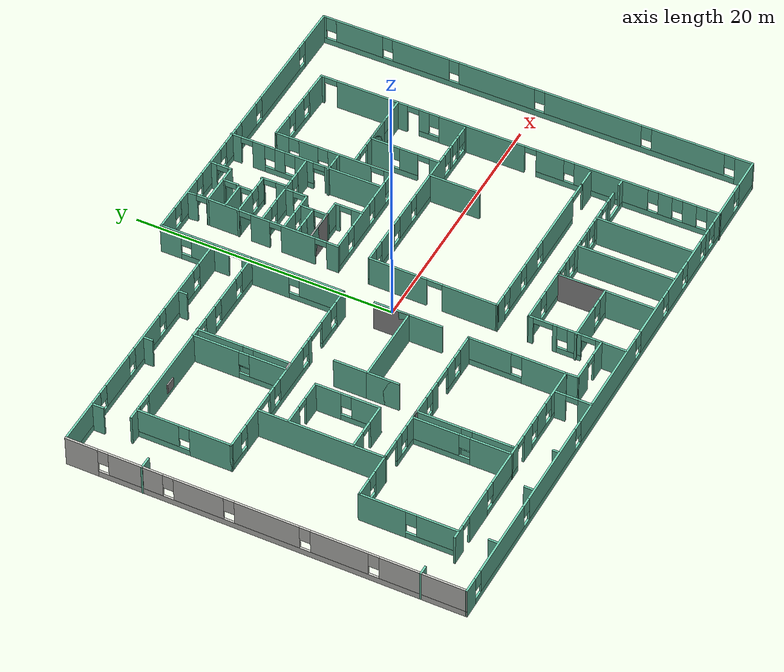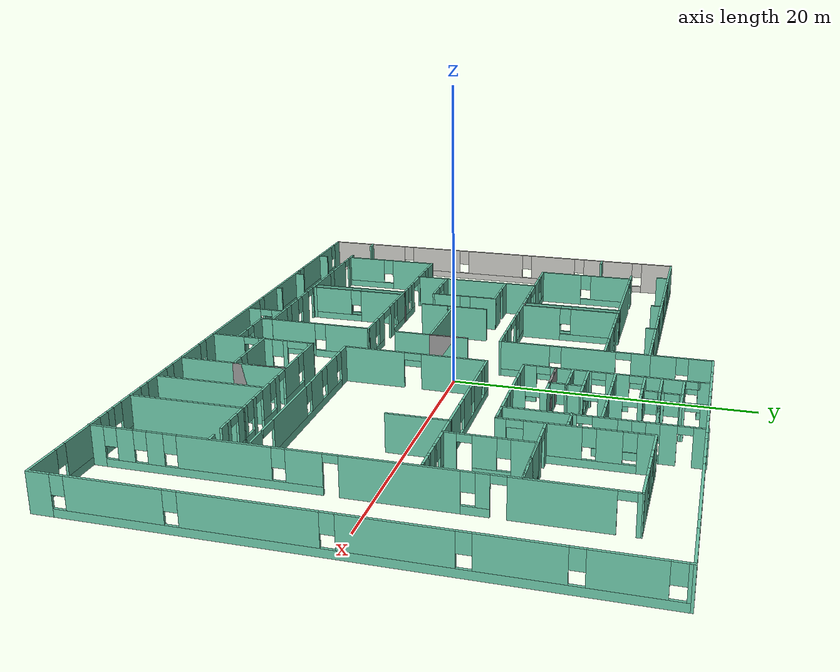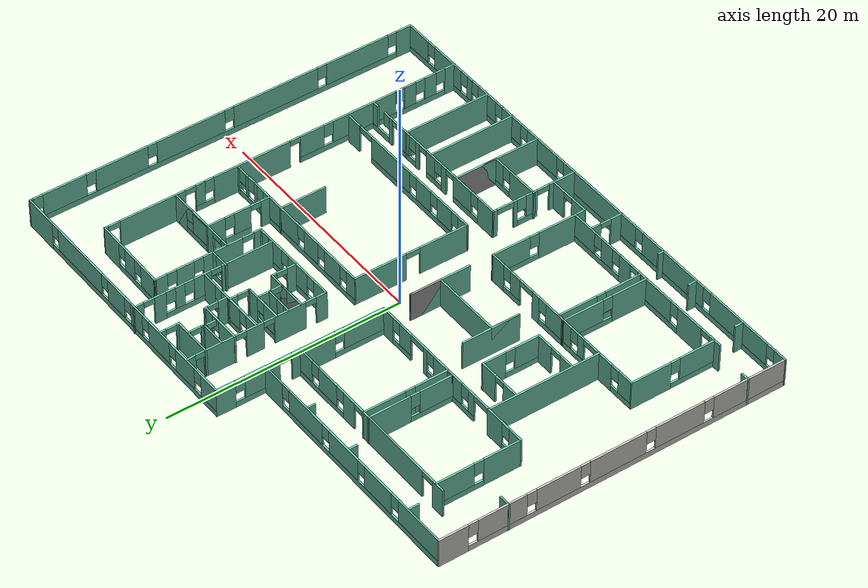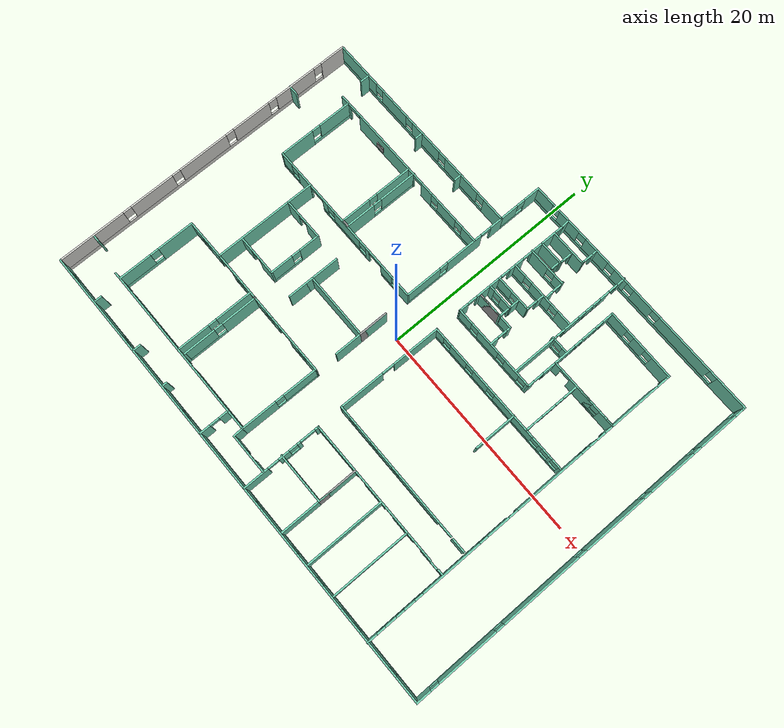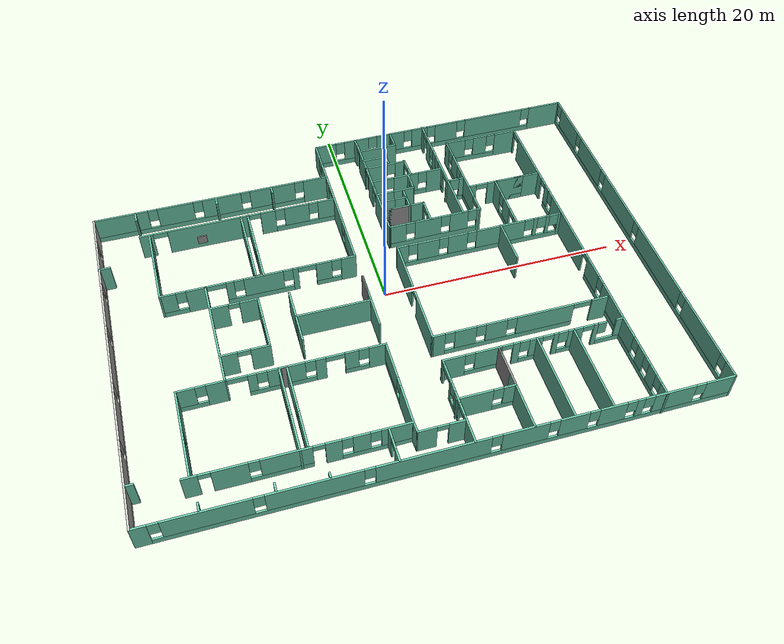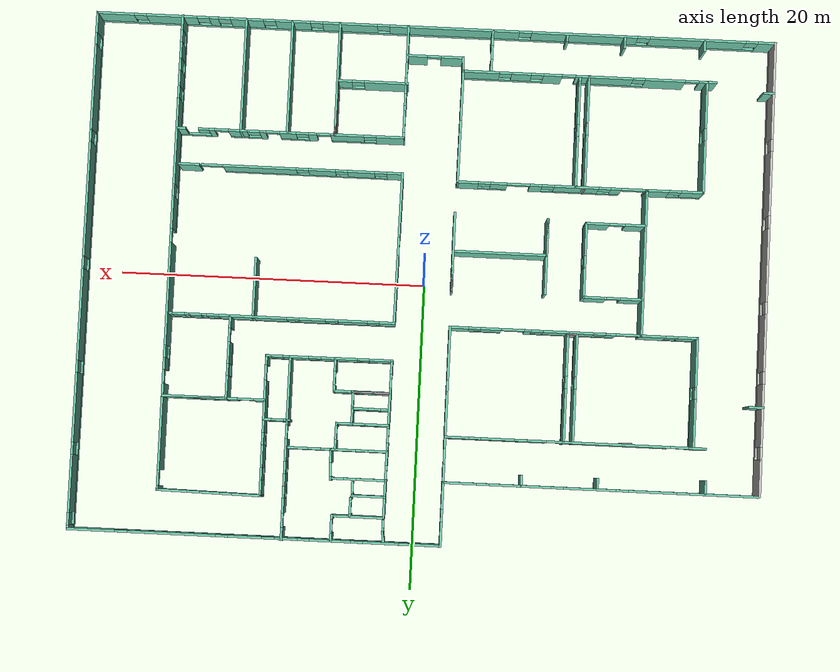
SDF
<?xml version='1.0'?>
<sdf version='1.6'>
  <model name='Hospital_empty'>
    <pose frame=''>-0.033999 0.051012 0 0 -0 0</pose>
    <link name='Wall_0'>
      <pose frame=''>-22.2855 -2.07101 0 0 0 -1.57157</pose>
      <visual name='Wall_0_Visual_0'>
        <pose frame=''>-13.6979 0 1.25 0 -0 0</pose>
        <geometry>
          <box>
            <size>2.48559 0.15 2.5</size>
          </box>
        </geometry>
        <material>
          <script>
            <uri>file://media/materials/scripts/gazebo.material</uri>
            <name>Gazebo/CeilingTiled</name>
          </script>
          <ambient>0.435294 0.796078 0.67451 1</ambient>
        </material>
      </visual>
      <collision name='Wall_0_Collision_0'>
        <geometry>
          <box>
            <size>2.48559 0.15 2.5</size>
          </box>
        </geometry>
        <pose frame=''>-13.6979 0 1.25 0 -0 0</pose>
      </collision>
      <visual name='Wall_0_Visual_1'>
        <pose frame=''>1.2428 0 0.25 0 -0 0</pose>
        <geometry>
          <box>
            <size>27.3959 0.15 0.5</size>
          </box>
        </geometry>
        <material>
          <script>
            <uri>file://media/materials/scripts/gazebo.material</uri>
            <name>Gazebo/CeilingTiled</name>
          </script>
          <ambient>0.435294 0.796078 0.67451 1</ambient>
        </material>
      </visual>
      <collision name='Wall_0_Collision_1'>
        <geometry>
          <box>
            <size>27.3959 0.15 0.5</size>
          </box>
        </geometry>
        <pose frame=''>1.2428 0 0.25 0 -0 0</pose>
      </collision>
      <visual name='Wall_0_Visual_2'>
        <pose frame=''>-9.59967 0 1.5 0 -0 0</pose>
        <geometry>
          <box>
            <size>4.11095 0.15 2</size>
          </box>
        </geometry>
        <material>
          <script>
            <uri>file://media/materials/scripts/gazebo.material</uri>
            <name>Gazebo/CeilingTiled</name>
          </script>
          <ambient>0.435294 0.796078 0.67451 1</ambient>
        </material>
      </visual>
      <collision name='Wall_0_Collision_2'>
        <geometry>
          <box>
            <size>4.11095 0.15 2</size>
          </box>
        </geometry>
        <pose frame=''>-9.59967 0 1.5 0 -0 0</pose>
      </collision>
      <visual name='Wall_0_Visual_3'>
        <pose frame=''>-4.86411 0 1.5 0 -0 0</pose>
        <geometry>
          <box>
            <size>3.76016 0.15 2</size>
          </box>
        </geometry>
        <material>
          <script>
            <uri>file://media/materials/scripts/gazebo.material</uri>
            <name>Gazebo/CeilingTiled</name>
          </script>
          <ambient>0.435294 0.796078 0.67451 1</ambient>
        </material>
      </visual>
      <collision name='Wall_0_Collision_3'>
        <geometry>
          <box>
            <size>3.76016 0.15 2</size>
          </box>
        </geometry>
        <pose frame=''>-4.86411 0 1.5 0 -0 0</pose>
      </collision>
      <visual name='Wall_0_Visual_4'>
        <pose frame=''>0.23681 0 1.5 0 -0 0</pose>
        <geometry>
          <box>
            <size>4.84168 0.15 2</size>
          </box>
        </geometry>
        <material>
          <script>
            <uri>file://media/materials/scripts/gazebo.material</uri>
            <name>Gazebo/CeilingTiled</name>
          </script>
          <ambient>0.435294 0.796078 0.67451 1</ambient>
        </material>
      </visual>
      <collision name='Wall_0_Collision_4'>
        <geometry>
          <box>
            <size>4.84168 0.15 2</size>
          </box>
        </geometry>
        <pose frame=''>0.23681 0 1.5 0 -0 0</pose>
      </collision>
      <visual name='Wall_0_Visual_5'>
        <pose frame=''>5.5901 0 1.5 0 -0 0</pose>
        <geometry>
          <box>
            <size>4.2649 0.15 2</size>
          </box>
        </geometry>
        <material>
          <script>
            <uri>file://media/materials/scripts/gazebo.material</uri>
            <name>Gazebo/CeilingTiled</name>
          </script>
          <ambient>0.435294 0.796078 0.67451 1</ambient>
        </material>
      </visual>
      <collision name='Wall_0_Collision_5'>
        <geometry>
          <box>
            <size>4.2649 0.15 2</size>
          </box>
        </geometry>
        <pose frame=''>5.5901 0 1.5 0 -0 0</pose>
      </collision>
      <visual name='Wall_0_Visual_6'>
        <pose frame=''>11.7316 0 1.5 0 -0 0</pose>
        <geometry>
          <box>
            <size>6.41818 0.15 2</size>
          </box>
        </geometry>
        <material>
          <script>
            <uri>file://media/materials/scripts/gazebo.material</uri>
            <name>Gazebo/CeilingTiled</name>
          </script>
          <ambient>0.435294 0.796078 0.67451 1</ambient>
        </material>
      </visual>
      <collision name='Wall_0_Collision_6'>
        <geometry>
          <box>
            <size>6.41818 0.15 2</size>
          </box>
        </geometry>
        <pose frame=''>11.7316 0 1.5 0 -0 0</pose>
      </collision>
      <visual name='Wall_0_Visual_7'>
        <pose frame=''>-12.0551 0 1.9 0 -0 0</pose>
        <geometry>
          <box>
            <size>0.8 0.15 1.2</size>
          </box>
        </geometry>
        <material>
          <script>
            <uri>file://media/materials/scripts/gazebo.material</uri>
            <name>Gazebo/CeilingTiled</name>
          </script>
          <ambient>0.435294 0.796078 0.67451 1</ambient>
        </material>
      </visual>
      <collision name='Wall_0_Collision_7'>
        <geometry>
          <box>
            <size>0.8 0.15 1.2</size>
          </box>
        </geometry>
        <pose frame=''>-12.0551 0 1.9 0 -0 0</pose>
      </collision>
      <visual name='Wall_0_Visual_8'>
        <pose frame=''>-7.14419 0 1.9 0 -0 0</pose>
        <geometry>
          <box>
            <size>0.8 0.15 1.2</size>
          </box>
        </geometry>
        <material>
          <script>
            <uri>file://media/materials/scripts/gazebo.material</uri>
            <name>Gazebo/CeilingTiled</name>
          </script>
          <ambient>0.435294 0.796078 0.67451 1</ambient>
        </material>
      </visual>
      <collision name='Wall_0_Collision_8'>
        <geometry>
          <box>
            <size>0.8 0.15 1.2</size>
          </box>
        </geometry>
        <pose frame=''>-7.14419 0 1.9 0 -0 0</pose>
      </collision>
      <visual name='Wall_0_Visual_9'>
        <pose frame=''>-2.58403 0 1.9 0 -0 0</pose>
        <geometry>
          <box>
            <size>0.8 0.15 1.2</size>
          </box>
        </geometry>
        <material>
          <script>
            <uri>file://media/materials/scripts/gazebo.material</uri>
            <name>Gazebo/CeilingTiled</name>
          </script>
          <ambient>0.435294 0.796078 0.67451 1</ambient>
        </material>
      </visual>
      <collision name='Wall_0_Collision_9'>
        <geometry>
          <box>
            <size>0.8 0.15 1.2</size>
          </box>
        </geometry>
        <pose frame=''>-2.58403 0 1.9 0 -0 0</pose>
      </collision>
      <visual name='Wall_0_Visual_10'>
        <pose frame=''>3.05765 0 1.9 0 -0 0</pose>
        <geometry>
          <box>
            <size>0.8 0.15 1.2</size>
          </box>
        </geometry>
        <material>
          <script>
            <uri>file://media/materials/scripts/gazebo.material</uri>
            <name>Gazebo/CeilingTiled</name>
          </script>
          <ambient>0.435294 0.796078 0.67451 1</ambient>
        </material>
      </visual>
      <collision name='Wall_0_Collision_10'>
        <geometry>
          <box>
            <size>0.8 0.15 1.2</size>
          </box>
        </geometry>
        <pose frame=''>3.05765 0 1.9 0 -0 0</pose>
      </collision>
      <visual name='Wall_0_Visual_11'>
        <pose frame=''>8.12255 0 1.9 0 -0 0</pose>
        <geometry>
          <box>
            <size>0.8 0.15 1.2</size>
          </box>
        </geometry>
        <material>
          <script>
            <uri>file://media/materials/scripts/gazebo.material</uri>
            <name>Gazebo/CeilingTiled</name>
          </script>
          <ambient>0.435294 0.796078 0.67451 1</ambient>
        </material>
      </visual>
      <collision name='Wall_0_Collision_11'>
        <geometry>
          <box>
            <size>0.8 0.15 1.2</size>
          </box>
        </geometry>
        <pose frame=''>8.12255 0 1.9 0 -0 0</pose>
      </collision>
    </link>
    <link name='Wall_1'>
      <pose frame=''>0.002999 -16.937 0 0 -0 0</pose>
      <visual name='Wall_1_Visual_0'>
        <pose frame=''>-21.7746 0 1.25 0 -0 0</pose>
        <geometry>
          <box>
            <size>1.20077 0.15 2.5</size>
          </box>
        </geometry>
        <material>
          <script>
            <uri>file://media/materials/scripts/gazebo.material</uri>
            <name>Gazebo/Grey</name>
          </script>
          <ambient>0.435294 0.796078 0.67451 1</ambient>
        </material>
      </visual>
      <collision name='Wall_1_Collision_0'>
        <geometry>
          <box>
            <size>1.20077 0.15 2.5</size>
          </box>
        </geometry>
        <pose frame=''>-21.7746 0 1.25 0 -0 0</pose>
      </collision>
      <visual name='Wall_1_Visual_1'>
        <pose frame=''>0.600387 0 0.25 0 -0 0</pose>
        <geometry>
          <box>
            <size>43.5492 0.15 0.5</size>
          </box>
        </geometry>
        <material>
          <script>
            <uri>file://media/materials/scripts/gazebo.material</uri>
            <name>Gazebo/Grey</name>
          </script>
          <ambient>0.435294 0.796078 0.67451 1</ambient>
        </material>
      </visual>
      <collision name='Wall_1_Collision_1'>
        <geometry>
          <box>
            <size>43.5492 0.15 0.5</size>
          </box>
        </geometry>
        <pose frame=''>0.600387 0 0.25 0 -0 0</pose>
      </collision>
      <visual name='Wall_1_Visual_2'>
        <pose frame=''>-17.2192 0 1.5 0 -0 0</pose>
        <geometry>
          <box>
            <size>6.31 0.15 2</size>
          </box>
        </geometry>
        <material>
          <script>
            <uri>file://media/materials/scripts/gazebo.material</uri>
            <name>Gazebo/Grey</name>
          </script>
          <ambient>0.435294 0.796078 0.67451 1</ambient>
        </material>
      </visual>
      <collision name='Wall_1_Collision_2'>
        <geometry>
          <box>
            <size>6.31 0.15 2</size>
          </box>
        </geometry>
        <pose frame=''>-17.2192 0 1.5 0 -0 0</pose>
      </collision>
      <visual name='Wall_1_Visual_3'>
        <pose frame=''>-9.77173 0 1.5 0 -0 0</pose>
        <geometry>
          <box>
            <size>6.985 0.15 2</size>
          </box>
        </geometry>
        <material>
          <script>
            <uri>file://media/materials/scripts/gazebo.material</uri>
            <name>Gazebo/Grey</name>
          </script>
          <ambient>0.435294 0.796078 0.67451 1</ambient>
        </material>
      </visual>
      <collision name='Wall_1_Collision_3'>
        <geometry>
          <box>
            <size>6.985 0.15 2</size>
          </box>
        </geometry>
        <pose frame=''>-9.77173 0 1.5 0 -0 0</pose>
      </collision>
      <visual name='Wall_1_Visual_4'>
        <pose frame=''>-1.19923 0 1.5 0 -0 0</pose>
        <geometry>
          <box>
            <size>8.56 0.15 2</size>
          </box>
        </geometry>
        <material>
          <script>
            <uri>file://media/materials/scripts/gazebo.material</uri>
            <name>Gazebo/Grey</name>
          </script>
          <ambient>0.435294 0.796078 0.67451 1</ambient>
        </material>
      </visual>
      <collision name='Wall_1_Collision_4'>
        <geometry>
          <box>
            <size>8.56 0.15 2</size>
          </box>
        </geometry>
        <pose frame=''>-1.19923 0 1.5 0 -0 0</pose>
      </collision>
      <visual name='Wall_1_Visual_5'>
        <pose frame=''>5.68577 0 1.5 0 -0 0</pose>
        <geometry>
          <box>
            <size>3.61 0.15 2</size>
          </box>
        </geometry>
        <material>
          <script>
            <uri>file://media/materials/scripts/gazebo.material</uri>
            <name>Gazebo/Grey</name>
          </script>
          <ambient>0.435294 0.796078 0.67451 1</ambient>
        </material>
      </visual>
      <collision name='Wall_1_Collision_5'>
        <geometry>
          <box>
            <size>3.61 0.15 2</size>
          </box>
        </geometry>
        <pose frame=''>5.68577 0 1.5 0 -0 0</pose>
      </collision>
      <visual name='Wall_1_Visual_6'>
        <pose frame=''>9.44327 0 1.5 0 -0 0</pose>
        <geometry>
          <box>
            <size>2.305 0.15 2</size>
          </box>
        </geometry>
        <material>
          <script>
            <uri>file://media/materials/scripts/gazebo.material</uri>
            <name>Gazebo/Grey</name>
          </script>
          <ambient>0.435294 0.796078 0.67451 1</ambient>
        </material>
      </visual>
      <collision name='Wall_1_Collision_6'>
        <geometry>
          <box>
            <size>2.305 0.15 2</size>
          </box>
        </geometry>
        <pose frame=''>9.44327 0 1.5 0 -0 0</pose>
      </collision>
      <visual name='Wall_1_Visual_7'>
        <pose frame=''>12.4808 0 1.5 0 -0 0</pose>
        <geometry>
          <box>
            <size>2.17 0.15 2</size>
          </box>
        </geometry>
        <material>
          <script>
            <uri>file://media/materials/scripts/gazebo.material</uri>
            <name>Gazebo/Grey</name>
          </script>
          <ambient>0.435294 0.796078 0.67451 1</ambient>
        </material>
      </visual>
      <collision name='Wall_1_Collision_7'>
        <geometry>
          <box>
            <size>2.17 0.15 2</size>
          </box>
        </geometry>
        <pose frame=''>12.4808 0 1.5 0 -0 0</pose>
      </collision>
      <visual name='Wall_1_Visual_8'>
        <pose frame=''>14.6633 0 1.5 0 -0 0</pose>
        <geometry>
          <box>
            <size>0.595 0.15 2</size>
          </box>
        </geometry>
        <material>
          <script>
            <uri>file://media/materials/scripts/gazebo.material</uri>
            <name>Gazebo/Grey</name>
          </script>
          <ambient>0.435294 0.796078 0.67451 1</ambient>
        </material>
      </visual>
      <collision name='Wall_1_Collision_8'>
        <geometry>
          <box>
            <size>0.595 0.15 2</size>
          </box>
        </geometry>
        <pose frame=''>14.6633 0 1.5 0 -0 0</pose>
      </collision>
      <visual name='Wall_1_Visual_9'>
        <pose frame=''>17.4308 0 1.5 0 -0 0</pose>
        <geometry>
          <box>
            <size>3.34 0.15 2</size>
          </box>
        </geometry>
        <material>
          <script>
            <uri>file://media/materials/scripts/gazebo.material</uri>
            <name>Gazebo/Grey</name>
          </script>
          <ambient>0.435294 0.796078 0.67451 1</ambient>
        </material>
      </visual>
      <collision name='Wall_1_Collision_9'>
        <geometry>
          <box>
            <size>3.34 0.15 2</size>
          </box>
        </geometry>
        <pose frame=''>17.4308 0 1.5 0 -0 0</pose>
      </collision>
      <visual name='Wall_1_Visual_10'>
        <pose frame=''>21.1379 0 1.5 0 -0 0</pose>
        <geometry>
          <box>
            <size>2.47423 0.15 2</size>
          </box>
        </geometry>
        <material>
          <script>
            <uri>file://media/materials/scripts/gazebo.material</uri>
            <name>Gazebo/Grey</name>
          </script>
          <ambient>0.435294 0.796078 0.67451 1</ambient>
        </material>
      </visual>
      <collision name='Wall_1_Collision_10'>
        <geometry>
          <box>
            <size>2.47423 0.15 2</size>
          </box>
        </geometry>
        <pose frame=''>21.1379 0 1.5 0 -0 0</pose>
      </collision>
      <visual name='Wall_1_Visual_11'>
        <pose frame=''>-20.7742 0 1.9 0 -0 0</pose>
        <geometry>
          <box>
            <size>0.8 0.15 1.2</size>
          </box>
        </geometry>
        <material>
          <script>
            <uri>file://media/materials/scripts/gazebo.material</uri>
            <name>Gazebo/Grey</name>
          </script>
          <ambient>0.435294 0.796078 0.67451 1</ambient>
        </material>
      </visual>
      <collision name='Wall_1_Collision_11'>
        <geometry>
          <box>
            <size>0.8 0.15 1.2</size>
          </box>
        </geometry>
        <pose frame=''>-20.7742 0 1.9 0 -0 0</pose>
      </collision>
      <visual name='Wall_1_Visual_12'>
        <pose frame=''>-13.6642 0 1.9 0 -0 0</pose>
        <geometry>
          <box>
            <size>0.8 0.15 1.2</size>
          </box>
        </geometry>
        <material>
          <script>
            <uri>file://media/materials/scripts/gazebo.material</uri>
            <name>Gazebo/Grey</name>
          </script>
          <ambient>0.435294 0.796078 0.67451 1</ambient>
        </material>
      </visual>
      <collision name='Wall_1_Collision_12'>
        <geometry>
          <box>
            <size>0.8 0.15 1.2</size>
          </box>
        </geometry>
        <pose frame=''>-13.6642 0 1.9 0 -0 0</pose>
      </collision>
      <visual name='Wall_1_Visual_13'>
        <pose frame=''>-5.87923 0 1.9 0 -0 0</pose>
        <geometry>
          <box>
            <size>0.8 0.15 1.2</size>
          </box>
        </geometry>
        <material>
          <script>
            <uri>file://media/materials/scripts/gazebo.material</uri>
            <name>Gazebo/Grey</name>
          </script>
          <ambient>0.435294 0.796078 0.67451 1</ambient>
        </material>
      </visual>
      <collision name='Wall_1_Collision_13'>
        <geometry>
          <box>
            <size>0.8 0.15 1.2</size>
          </box>
        </geometry>
        <pose frame=''>-5.87923 0 1.9 0 -0 0</pose>
      </collision>
      <visual name='Wall_1_Visual_14'>
        <pose frame=''>3.48077 0 1.9 0 -0 0</pose>
        <geometry>
          <box>
            <size>0.8 0.15 1.2</size>
          </box>
        </geometry>
        <material>
          <script>
            <uri>file://media/materials/scripts/gazebo.material</uri>
            <name>Gazebo/Grey</name>
          </script>
          <ambient>0.435294 0.796078 0.67451 1</ambient>
        </material>
      </visual>
      <collision name='Wall_1_Collision_14'>
        <geometry>
          <box>
            <size>0.8 0.15 1.2</size>
          </box>
        </geometry>
        <pose frame=''>3.48077 0 1.9 0 -0 0</pose>
      </collision>
      <visual name='Wall_1_Visual_15'>
        <pose frame=''>7.89077 0 1.9 0 -0 0</pose>
        <geometry>
          <box>
            <size>0.8 0.15 1.2</size>
          </box>
        </geometry>
        <material>
          <script>
            <uri>file://media/materials/scripts/gazebo.material</uri>
            <name>Gazebo/Grey</name>
          </script>
          <ambient>0.435294 0.796078 0.67451 1</ambient>
        </material>
      </visual>
      <collision name='Wall_1_Collision_15'>
        <geometry>
          <box>
            <size>0.8 0.15 1.2</size>
          </box>
        </geometry>
        <pose frame=''>7.89077 0 1.9 0 -0 0</pose>
      </collision>
      <visual name='Wall_1_Visual_16'>
        <pose frame=''>10.9958 0 1.9 0 -0 0</pose>
        <geometry>
          <box>
            <size>0.8 0.15 1.2</size>
          </box>
        </geometry>
        <material>
          <script>
            <uri>file://media/materials/scripts/gazebo.material</uri>
            <name>Gazebo/Grey</name>
          </script>
          <ambient>0.435294 0.796078 0.67451 1</ambient>
        </material>
      </visual>
      <collision name='Wall_1_Collision_16'>
        <geometry>
          <box>
            <size>0.8 0.15 1.2</size>
          </box>
        </geometry>
        <pose frame=''>10.9958 0 1.9 0 -0 0</pose>
      </collision>
      <visual name='Wall_1_Visual_17'>
        <pose frame=''>13.9658 0 1.9 0 -0 0</pose>
        <geometry>
          <box>
            <size>0.8 0.15 1.2</size>
          </box>
        </geometry>
        <material>
          <script>
            <uri>file://media/materials/scripts/gazebo.material</uri>
            <name>Gazebo/Grey</name>
          </script>
          <ambient>0.435294 0.796078 0.67451 1</ambient>
        </material>
      </visual>
      <collision name='Wall_1_Collision_17'>
        <geometry>
          <box>
            <size>0.8 0.15 1.2</size>
          </box>
        </geometry>
        <pose frame=''>13.9658 0 1.9 0 -0 0</pose>
      </collision>
      <visual name='Wall_1_Visual_18'>
        <pose frame=''>15.3608 0 1.9 0 -0 0</pose>
        <geometry>
          <box>
            <size>0.8 0.15 1.2</size>
          </box>
        </geometry>
        <material>
          <script>
            <uri>file://media/materials/scripts/gazebo.material</uri>
            <name>Gazebo/Grey</name>
          </script>
          <ambient>0.435294 0.796078 0.67451 1</ambient>
        </material>
      </visual>
      <collision name='Wall_1_Collision_18'>
        <geometry>
          <box>
            <size>0.8 0.15 1.2</size>
          </box>
        </geometry>
        <pose frame=''>15.3608 0 1.9 0 -0 0</pose>
      </collision>
      <visual name='Wall_1_Visual_19'>
        <pose frame=''>19.5008 0 1.9 0 -0 0</pose>
        <geometry>
          <box>
            <size>0.8 0.15 1.2</size>
          </box>
        </geometry>
        <material>
          <script>
            <uri>file://media/materials/scripts/gazebo.material</uri>
            <name>Gazebo/Grey</name>
          </script>
          <ambient>0.435294 0.796078 0.67451 1</ambient>
        </material>
      </visual>
      <collision name='Wall_1_Collision_19'>
        <geometry>
          <box>
            <size>0.8 0.15 1.2</size>
          </box>
        </geometry>
        <pose frame=''>19.5008 0 1.9 0 -0 0</pose>
      </collision>
    </link>
    <link name='Wall_100'>
      <pose frame=''>3.70852 12.8706 0 0 -0 0</pose>
      <visual name='Wall_100_Visual_0'>
        <pose frame=''>-0.873017 0 1.25 0 -0 0</pose>
        <geometry>
          <box>
            <size>2.00397 0.15 2.5</size>
          </box>
        </geometry>
        <material>
          <script>
            <uri>file://media/materials/scripts/gazebo.material</uri>
            <name>Gazebo/Grey</name>
          </script>
          <ambient>0.435294 0.796078 0.67451 1</ambient>
        </material>
      </visual>
      <collision name='Wall_100_Collision_0'>
        <geometry>
          <box>
            <size>2.00397 0.15 2.5</size>
          </box>
        </geometry>
        <pose frame=''>-0.873017 0 1.25 0 -0 0</pose>
      </collision>
      <visual name='Wall_100_Visual_1'>
        <pose frame=''>1.00198 0 0.25 0 -0 0</pose>
        <geometry>
          <box>
            <size>1.74603 0.15 0.5</size>
          </box>
        </geometry>
        <material>
          <script>
            <uri>file://media/materials/scripts/gazebo.material</uri>
            <name>Gazebo/Grey</name>
          </script>
          <ambient>0.435294 0.796078 0.67451 1</ambient>
        </material>
      </visual>
      <collision name='Wall_100_Collision_1'>
        <geometry>
          <box>
            <size>1.74603 0.15 0.5</size>
          </box>
        </geometry>
        <pose frame=''>1.00198 0 0.25 0 -0 0</pose>
      </collision>
      <visual name='Wall_100_Visual_2'>
        <pose frame=''>1.40198 0 1.5 0 -0 0</pose>
        <geometry>
          <box>
            <size>0.946034 0.15 2</size>
          </box>
        </geometry>
        <material>
          <script>
            <uri>file://media/materials/scripts/gazebo.material</uri>
            <name>Gazebo/Grey</name>
          </script>
          <ambient>0.435294 0.796078 0.67451 1</ambient>
        </material>
      </visual>
      <collision name='Wall_100_Collision_2'>
        <geometry>
          <box>
            <size>0.946034 0.15 2</size>
          </box>
        </geometry>
        <pose frame=''>1.40198 0 1.5 0 -0 0</pose>
      </collision>
      <visual name='Wall_100_Visual_3'>
        <pose frame=''>0.528966 0 1.9 0 -0 0</pose>
        <geometry>
          <box>
            <size>0.8 0.15 1.2</size>
          </box>
        </geometry>
        <material>
          <script>
            <uri>file://media/materials/scripts/gazebo.material</uri>
            <name>Gazebo/Grey</name>
          </script>
          <ambient>0.435294 0.796078 0.67451 1</ambient>
        </material>
      </visual>
      <collision name='Wall_100_Collision_3'>
        <geometry>
          <box>
            <size>0.8 0.15 1.2</size>
          </box>
        </geometry>
        <pose frame=''>0.528966 0 1.9 0 -0 0</pose>
      </collision>
    </link>
    <link name='Wall_101'>
      <pose frame=''>5.53676 11.9973 0 0 0 -1.5414</pose>
      <visual name='Wall_101_Visual_0'>
        <pose frame=''>-0.894743 0 1.25 0 -0 0</pose>
        <geometry>
          <box>
            <size>0.281917 0.15 2.5</size>
          </box>
        </geometry>
        <material>
          <script>
            <uri>file://media/materials/scripts/gazebo.material</uri>
            <name>Gazebo/Grey</name>
          </script>
          <ambient>0.435294 0.796078 0.67451 1</ambient>
        </material>
      </visual>
      <collision name='Wall_101_Collision_0'>
        <geometry>
          <box>
            <size>0.281917 0.15 2.5</size>
          </box>
        </geometry>
        <pose frame=''>-0.894743 0 1.25 0 -0 0</pose>
      </collision>
      <visual name='Wall_101_Visual_1'>
        <pose frame=''>0.590959 0 1.25 0 -0 0</pose>
        <geometry>
          <box>
            <size>0.889485 0.15 2.5</size>
          </box>
        </geometry>
        <material>
          <script>
            <uri>file://media/materials/scripts/gazebo.material</uri>
            <name>Gazebo/Grey</name>
          </script>
          <ambient>0.435294 0.796078 0.67451 1</ambient>
        </material>
      </visual>
      <collision name='Wall_101_Collision_1'>
        <geometry>
          <box>
            <size>0.889485 0.15 2.5</size>
          </box>
        </geometry>
        <pose frame=''>0.590959 0 1.25 0 -0 0</pose>
      </collision>
      <visual name='Wall_101_Visual_2'>
        <pose frame=''>-0.303784 0 2.25 0 -0 0</pose>
        <geometry>
          <box>
            <size>0.9 0.15 0.5</size>
          </box>
        </geometry>
        <material>
          <script>
            <uri>file://media/materials/scripts/gazebo.material</uri>
            <name>Gazebo/Grey</name>
          </script>
          <ambient>0.435294 0.796078 0.67451 1</ambient>
        </material>
      </visual>
      <collision name='Wall_101_Collision_2'>
        <geometry>
          <box>
            <size>0.9 0.15 0.5</size>
          </box>
        </geometry>
        <pose frame=''>-0.303784 0 2.25 0 -0 0</pose>
      </collision>
    </link>
    <link name='Wall_103'>
      <pose frame=''>5.15177 11.0095 0 0 -0 3.14159</pose>
      <visual name='Wall_103_Visual_0'>
        <pose frame=''>-2.56982 0 1.25 0 -0 0</pose>
        <geometry>
          <box>
            <size>1.36037 0.15 2.5</size>
          </box>
        </geometry>
        <material>
          <script>
            <uri>file://media/materials/scripts/gazebo.material</uri>
            <name>Gazebo/Grey</name>
          </script>
          <ambient>0.435294 0.796078 0.67451 1</ambient>
        </material>
      </visual>
      <collision name='Wall_103_Collision_0'>
        <geometry>
          <box>
            <size>1.36037 0.15 2.5</size>
          </box>
        </geometry>
        <pose frame=''>-2.56982 0 1.25 0 -0 0</pose>
      </collision>
      <visual name='Wall_103_Visual_1'>
        <pose frame=''>0.680183 0 0.25 0 -0 0</pose>
        <geometry>
          <box>
            <size>5.13964 0.15 0.5</size>
          </box>
        </geometry>
        <material>
          <script>
            <uri>file://media/materials/scripts/gazebo.material</uri>
            <name>Gazebo/Grey</name>
          </script>
          <ambient>0.435294 0.796078 0.67451 1</ambient>
        </material>
      </visual>
      <collision name='Wall_103_Collision_1'>
        <geometry>
          <box>
            <size>5.13964 0.15 0.5</size>
          </box>
        </geometry>
        <pose frame=''>0.680183 0 0.25 0 -0 0</pose>
      </collision>
      <visual name='Wall_103_Visual_2'>
        <pose frame=''>0.054099 0 1.5 0 -0 0</pose>
        <geometry>
          <box>
            <size>2.28747 0.15 2</size>
          </box>
        </geometry>
        <material>
          <script>
            <uri>file://media/materials/scripts/gazebo.material</uri>
            <name>Gazebo/Grey</name>
          </script>
          <ambient>0.435294 0.796078 0.67451 1</ambient>
        </material>
      </visual>
      <collision name='Wall_103_Collision_2'>
        <geometry>
          <box>
            <size>2.28747 0.15 2</size>
          </box>
        </geometry>
        <pose frame=''>0.054099 0 1.5 0 -0 0</pose>
      </collision>
      <visual name='Wall_103_Visual_3'>
        <pose frame=''>2.62392 0 1.5 0 -0 0</pose>
        <geometry>
          <box>
            <size>1.25217 0.15 2</size>
          </box>
        </geometry>
        <material>
          <script>
            <uri>file://media/materials/scripts/gazebo.material</uri>
            <name>Gazebo/Grey</name>
          </script>
          <ambient>0.435294 0.796078 0.67451 1</ambient>
        </material>
      </visual>
      <collision name='Wall_103_Collision_3'>
        <geometry>
          <box>
            <size>1.25217 0.15 2</size>
          </box>
        </geometry>
        <pose frame=''>2.62392 0 1.5 0 -0 0</pose>
      </collision>
      <visual name='Wall_103_Visual_4'>
        <pose frame=''>-1.48964 0 1.9 0 -0 0</pose>
        <geometry>
          <box>
            <size>0.8 0.15 1.2</size>
          </box>
        </geometry>
        <material>
          <script>
            <uri>file://media/materials/scripts/gazebo.material</uri>
            <name>Gazebo/Grey</name>
          </script>
          <ambient>0.435294 0.796078 0.67451 1</ambient>
        </material>
      </visual>
      <collision name='Wall_103_Collision_4'>
        <geometry>
          <box>
            <size>0.8 0.15 1.2</size>
          </box>
        </geometry>
        <pose frame=''>-1.48964 0 1.9 0 -0 0</pose>
      </collision>
      <visual name='Wall_103_Visual_5'>
        <pose frame=''>1.59783 0 1.9 0 -0 0</pose>
        <geometry>
          <box>
            <size>0.8 0.15 1.2</size>
          </box>
        </geometry>
        <material>
          <script>
            <uri>file://media/materials/scripts/gazebo.material</uri>
            <name>Gazebo/Grey</name>
          </script>
          <ambient>0.435294 0.796078 0.67451 1</ambient>
        </material>
      </visual>
      <collision name='Wall_103_Collision_5'>
        <geometry>
          <box>
            <size>0.8 0.15 1.2</size>
          </box>
        </geometry>
        <pose frame=''>1.59783 0 1.9 0 -0 0</pose>
      </collision>
    </link>
    <link name='Wall_105'>
      <pose frame=''>5.291 10.1575 0 0 0 -1.58367</pose>
      <visual name='Wall_105_Visual_0'>
        <pose frame=''>-0.562111 0 1.25 0 -0 0</pose>
        <geometry>
          <box>
            <size>0.734515 0.15 2.5</size>
          </box>
        </geometry>
        <material>
          <script>
            <uri>file://media/materials/scripts/gazebo.material</uri>
            <name>Gazebo/Grey</name>
          </script>
          <ambient>0.435294 0.796078 0.67451 1</ambient>
        </material>
      </visual>
      <collision name='Wall_105_Collision_0'>
        <geometry>
          <box>
            <size>0.734515 0.15 2.5</size>
          </box>
        </geometry>
        <pose frame=''>-0.562111 0 1.25 0 -0 0</pose>
      </collision>
      <visual name='Wall_105_Visual_1'>
        <pose frame=''>0.817258 0 1.25 0 -0 0</pose>
        <geometry>
          <box>
            <size>0.224223 0.15 2.5</size>
          </box>
        </geometry>
        <material>
          <script>
            <uri>file://media/materials/scripts/gazebo.material</uri>
            <name>Gazebo/Grey</name>
          </script>
          <ambient>0.435294 0.796078 0.67451 1</ambient>
        </material>
      </visual>
      <collision name='Wall_105_Collision_1'>
        <geometry>
          <box>
            <size>0.224223 0.15 2.5</size>
          </box>
        </geometry>
        <pose frame=''>0.817258 0 1.25 0 -0 0</pose>
      </collision>
      <visual name='Wall_105_Visual_2'>
        <pose frame=''>0.255146 0 2.25 0 -0 0</pose>
        <geometry>
          <box>
            <size>0.9 0.15 0.5</size>
          </box>
        </geometry>
        <material>
          <script>
            <uri>file://media/materials/scripts/gazebo.material</uri>
            <name>Gazebo/Grey</name>
          </script>
          <ambient>0.435294 0.796078 0.67451 1</ambient>
        </material>
      </visual>
      <collision name='Wall_105_Collision_2'>
        <geometry>
          <box>
            <size>0.9 0.15 0.5</size>
          </box>
        </geometry>
        <pose frame=''>0.255146 0 2.25 0 -0 0</pose>
      </collision>
    </link>
    <link name='Wall_106'>
      <pose frame=''>3.616 9.30314 0 0 -0 3.1415</pose>
      <visual name='Wall_106_Visual_0'>
        <pose frame=''>-1.18986 0 1.25 0 -0 0</pose>
        <geometry>
          <box>
            <size>1.09829 0.15 2.5</size>
          </box>
        </geometry>
        <material>
          <script>
            <uri>file://media/materials/scripts/gazebo.material</uri>
            <name>Gazebo/Grey</name>
          </script>
          <ambient>0.435294 0.796078 0.67451 1</ambient>
        </material>
      </visual>
      <collision name='Wall_106_Collision_0'>
        <geometry>
          <box>
            <size>1.09829 0.15 2.5</size>
          </box>
        </geometry>
        <pose frame=''>-1.18986 0 1.25 0 -0 0</pose>
      </collision>
      <visual name='Wall_106_Visual_1'>
        <pose frame=''>0.549144 0 0.25 0 -0 0</pose>
        <geometry>
          <box>
            <size>2.37971 0.15 0.5</size>
          </box>
        </geometry>
        <material>
          <script>
            <uri>file://media/materials/scripts/gazebo.material</uri>
            <name>Gazebo/Grey</name>
          </script>
          <ambient>0.435294 0.796078 0.67451 1</ambient>
        </material>
      </visual>
      <collision name='Wall_106_Collision_1'>
        <geometry>
          <box>
            <size>2.37971 0.15 0.5</size>
          </box>
        </geometry>
        <pose frame=''>0.549144 0 0.25 0 -0 0</pose>
      </collision>
      <visual name='Wall_106_Visual_2'>
        <pose frame=''>0.949144 0 1.5 0 -0 0</pose>
        <geometry>
          <box>
            <size>1.57971 0.15 2</size>
          </box>
        </geometry>
        <material>
          <script>
            <uri>file://media/materials/scripts/gazebo.material</uri>
            <name>Gazebo/Grey</name>
          </script>
          <ambient>0.435294 0.796078 0.67451 1</ambient>
        </material>
      </visual>
      <collision name='Wall_106_Collision_2'>
        <geometry>
          <box>
            <size>1.57971 0.15 2</size>
          </box>
        </geometry>
        <pose frame=''>0.949144 0 1.5 0 -0 0</pose>
      </collision>
      <visual name='Wall_106_Visual_3'>
        <pose frame=''>-0.240712 0 1.9 0 -0 0</pose>
        <geometry>
          <box>
            <size>0.8 0.15 1.2</size>
          </box>
        </geometry>
        <material>
          <script>
            <uri>file://media/materials/scripts/gazebo.material</uri>
            <name>Gazebo/Grey</name>
          </script>
          <ambient>0.435294 0.796078 0.67451 1</ambient>
        </material>
      </visual>
      <collision name='Wall_106_Collision_3'>
        <geometry>
          <box>
            <size>0.8 0.15 1.2</size>
          </box>
        </geometry>
        <pose frame=''>-0.240712 0 1.9 0 -0 0</pose>
      </collision>
    </link>
    <link name='Wall_108'>
      <pose frame=''>3.12156 8.29555 0 0 0 -0.004715</pose>
      <visual name='Wall_108_Visual_0'>
        <pose frame=''>-0.954583 0 1.25 0 -0 0</pose>
        <geometry>
          <box>
            <size>0.60173 0.15 2.5</size>
          </box>
        </geometry>
        <material>
          <script>
            <uri>file://media/materials/scripts/gazebo.material</uri>
            <name>Gazebo/Grey</name>
          </script>
          <ambient>0.435294 0.796078 0.67451 1</ambient>
        </material>
      </visual>
      <collision name='Wall_108_Collision_0'>
        <geometry>
          <box>
            <size>0.60173 0.15 2.5</size>
          </box>
        </geometry>
        <pose frame=''>-0.954583 0 1.25 0 -0 0</pose>
      </collision>
      <visual name='Wall_108_Visual_1'>
        <pose frame=''>0.300865 0 0.25 0 -0 0</pose>
        <geometry>
          <box>
            <size>1.90917 0.15 0.5</size>
          </box>
        </geometry>
        <material>
          <script>
            <uri>file://media/materials/scripts/gazebo.material</uri>
            <name>Gazebo/Grey</name>
          </script>
          <ambient>0.435294 0.796078 0.67451 1</ambient>
        </material>
      </visual>
      <collision name='Wall_108_Collision_1'>
        <geometry>
          <box>
            <size>1.90917 0.15 0.5</size>
          </box>
        </geometry>
        <pose frame=''>0.300865 0 0.25 0 -0 0</pose>
      </collision>
      <visual name='Wall_108_Visual_2'>
        <pose frame=''>0.700865 0 1.5 0 -0 0</pose>
        <geometry>
          <box>
            <size>1.10916 0.15 2</size>
          </box>
        </geometry>
        <material>
          <script>
            <uri>file://media/materials/scripts/gazebo.material</uri>
            <name>Gazebo/Grey</name>
          </script>
          <ambient>0.435294 0.796078 0.67451 1</ambient>
        </material>
      </visual>
      <collision name='Wall_108_Collision_2'>
        <geometry>
          <box>
            <size>1.10916 0.15 2</size>
          </box>
        </geometry>
        <pose frame=''>0.700865 0 1.5 0 -0 0</pose>
      </collision>
      <visual name='Wall_108_Visual_3'>
        <pose frame=''>-0.253718 0 1.9 0 -0 0</pose>
        <geometry>
          <box>
            <size>0.8 0.15 1.2</size>
          </box>
        </geometry>
        <material>
          <script>
            <uri>file://media/materials/scripts/gazebo.material</uri>
            <name>Gazebo/Grey</name>
          </script>
          <ambient>0.435294 0.796078 0.67451 1</ambient>
        </material>
      </visual>
      <collision name='Wall_108_Collision_3'>
        <geometry>
          <box>
            <size>0.8 0.15 1.2</size>
          </box>
        </geometry>
        <pose frame=''>-0.253718 0 1.9 0 -0 0</pose>
      </collision>
    </link>
    <link name='Wall_109'>
      <pose frame=''>4.302 7.75099 0 0 0 -1.5708</pose>
      <visual name='Wall_109_Visual_0'>
        <pose frame=''>-0.512428 0 1.25 0 -0 0</pose>
        <geometry>
          <box>
            <size>0.203406 0.15 2.5</size>
          </box>
        </geometry>
        <material>
          <script>
            <uri>file://media/materials/scripts/gazebo.material</uri>
            <name>Gazebo/Grey</name>
          </script>
          <ambient>0.435294 0.796078 0.67451 1</ambient>
        </material>
      </visual>
      <collision name='Wall_109_Collision_0'>
        <geometry>
          <box>
            <size>0.203406 0.15 2.5</size>
          </box>
        </geometry>
        <pose frame=''>-0.512428 0 1.25 0 -0 0</pose>
      </collision>
      <visual name='Wall_109_Visual_1'>
        <pose frame=''>0.551703 0 1.25 0 -0 0</pose>
        <geometry>
          <box>
            <size>0.124856 0.15 2.5</size>
          </box>
        </geometry>
        <material>
          <script>
            <uri>file://media/materials/scripts/gazebo.material</uri>
            <name>Gazebo/Grey</name>
          </script>
          <ambient>0.435294 0.796078 0.67451 1</ambient>
        </material>
      </visual>
      <collision name='Wall_109_Collision_1'>
        <geometry>
          <box>
            <size>0.124856 0.15 2.5</size>
          </box>
        </geometry>
        <pose frame=''>0.551703 0 1.25 0 -0 0</pose>
      </collision>
      <visual name='Wall_109_Visual_2'>
        <pose frame=''>0.039275 0 2.25 0 -0 0</pose>
        <geometry>
          <box>
            <size>0.9 0.15 0.5</size>
          </box>
        </geometry>
        <material>
          <script>
            <uri>file://media/materials/scripts/gazebo.material</uri>
            <name>Gazebo/Grey</name>
          </script>
          <ambient>0.435294 0.796078 0.67451 1</ambient>
        </material>
      </visual>
      <collision name='Wall_109_Collision_2'>
        <geometry>
          <box>
            <size>0.9 0.15 0.5</size>
          </box>
        </geometry>
        <pose frame=''>0.039275 0 2.25 0 -0 0</pose>
      </collision>
    </link>
    <link name='Wall_11'>
      <collision name='Wall_11_Collision'>
        <geometry>
          <box>
            <size>0.75 0.15 2.5</size>
          </box>
        </geometry>
        <pose frame=''>0 0 1.25 0 -0 0</pose>
      </collision>
      <visual name='Wall_11_Visual'>
        <pose frame=''>0 0 1.25 0 -0 0</pose>
        <geometry>
          <box>
            <size>0.75 0.15 2.5</size>
          </box>
        </geometry>
        <material>
          <script>
            <uri>file://media/materials/scripts/gazebo.material</uri>
            <name>Gazebo/Grey</name>
          </script>
          <ambient>0.435294 0.796078 0.67451 1</ambient>
        </material>
      </visual>
      <pose frame=''>-11.779 12.417 0 0 0 -1.5708</pose>
    </link>
    <link name='Wall_110'>
      <collision name='Wall_110_Collision'>
        <geometry>
          <box>
            <size>2.5 0.15 2.5</size>
          </box>
        </geometry>
        <pose frame=''>0 0 1.25 0 -0 0</pose>
      </collision>
      <visual name='Wall_110_Visual'>
        <pose frame=''>0 0 1.25 0 -0 0</pose>
        <geometry>
          <box>
            <size>2.5 0.15 2.5</size>
          </box>
        </geometry>
        <material>
          <script>
            <uri>file://media/materials/scripts/gazebo.material</uri>
            <name>Gazebo/Grey</name>
          </script>
          <ambient>1 1 1 1</ambient>
        </material>
      </visual>
      <pose frame=''>3.127 7.21199 0 0 -0 3.14159</pose>
    </link>
    <link name='Wall_111'>
      <pose frame=''>3.752 7.21199 0 0 -0 0</pose>
      <visual name='Wall_111_Visual_0'>
        <pose frame=''>-0.993085 0 1.25 0 -0 0</pose>
        <geometry>
          <box>
            <size>1.76383 0.15 2.5</size>
          </box>
        </geometry>
        <material>
          <script>
            <uri>file://media/materials/scripts/gazebo.material</uri>
            <name>Gazebo/Grey</name>
          </script>
          <ambient>0.435294 0.796078 0.67451 1</ambient>
        </material>
      </visual>
      <collision name='Wall_111_Collision_0'>
        <geometry>
          <box>
            <size>1.76383 0.15 2.5</size>
          </box>
        </geometry>
        <pose frame=''>-0.993085 0 1.25 0 -0 0</pose>
      </collision>
      <visual name='Wall_111_Visual_1'>
        <pose frame=''>0.881915 0 0.25 0 -0 0</pose>
        <geometry>
          <box>
            <size>1.98617 0.15 0.5</size>
          </box>
        </geometry>
        <material>
          <script>
            <uri>file://media/materials/scripts/gazebo.material</uri>
            <name>Gazebo/Grey</name>
          </script>
          <ambient>0.435294 0.796078 0.67451 1</ambient>
        </material>
      </visual>
      <collision name='Wall_111_Collision_1'>
        <geometry>
          <box>
            <size>1.98617 0.15 0.5</size>
          </box>
        </geometry>
        <pose frame=''>0.881915 0 0.25 0 -0 0</pose>
      </collision>
      <visual name='Wall_111_Visual_2'>
        <pose frame=''>1.28191 0 1.5 0 -0 0</pose>
        <geometry>
          <box>
            <size>1.18617 0.15 2</size>
          </box>
        </geometry>
        <material>
          <script>
            <uri>file://media/materials/scripts/gazebo.material</uri>
            <name>Gazebo/Grey</name>
          </script>
          <ambient>0.435294 0.796078 0.67451 1</ambient>
        </material>
      </visual>
      <collision name='Wall_111_Collision_2'>
        <geometry>
          <box>
            <size>1.18617 0.15 2</size>
          </box>
        </geometry>
        <pose frame=''>1.28191 0 1.5 0 -0 0</pose>
      </collision>
      <visual name='Wall_111_Visual_3'>
        <pose frame=''>0.28883 0 1.9 0 -0 0</pose>
        <geometry>
          <box>
            <size>0.8 0.15 1.2</size>
          </box>
        </geometry>
        <material>
          <script>
            <uri>file://media/materials/scripts/gazebo.material</uri>
            <name>Gazebo/Grey</name>
          </script>
          <ambient>0.435294 0.796078 0.67451 1</ambient>
        </material>
      </visual>
      <collision name='Wall_111_Collision_3'>
        <geometry>
          <box>
            <size>0.8 0.15 1.2</size>
          </box>
        </geometry>
        <pose frame=''>0.28883 0 1.9 0 -0 0</pose>
      </collision>
    </link>
    <link name='Wall_112'>
      <pose frame=''>5.552 6.16199 0 0 0 -1.5708</pose>
      <visual name='Wall_112_Visual_0'>
        <pose frame=''>-0.900897 0 1.25 0 -0 0</pose>
        <geometry>
          <box>
            <size>0.448206 0.15 2.5</size>
          </box>
        </geometry>
        <material>
          <script>
            <uri>file://media/materials/scripts/gazebo.material</uri>
            <name>Gazebo/Grey</name>
          </script>
          <ambient>0.435294 0.796078 0.67451 1</ambient>
        </material>
      </visual>
      <collision name='Wall_112_Collision_0'>
        <geometry>
          <box>
            <size>0.448206 0.15 2.5</size>
          </box>
        </geometry>
        <pose frame=''>-0.900897 0 1.25 0 -0 0</pose>
      </collision>
      <visual name='Wall_112_Visual_1'>
        <pose frame=''>0.674103 0 1.25 0 -0 0</pose>
        <geometry>
          <box>
            <size>0.901794 0.15 2.5</size>
          </box>
        </geometry>
        <material>
          <script>
            <uri>file://media/materials/scripts/gazebo.material</uri>
            <name>Gazebo/Grey</name>
          </script>
          <ambient>0.435294 0.796078 0.67451 1</ambient>
        </material>
      </visual>
      <collision name='Wall_112_Collision_1'>
        <geometry>
          <box>
            <size>0.901794 0.15 2.5</size>
          </box>
        </geometry>
        <pose frame=''>0.674103 0 1.25 0 -0 0</pose>
      </collision>
      <visual name='Wall_112_Visual_2'>
        <pose frame=''>-0.226794 0 2.25 0 -0 0</pose>
        <geometry>
          <box>
            <size>0.9 0.15 0.5</size>
          </box>
        </geometry>
        <material>
          <script>
            <uri>file://media/materials/scripts/gazebo.material</uri>
            <name>Gazebo/Grey</name>
          </script>
          <ambient>0.435294 0.796078 0.67451 1</ambient>
        </material>
      </visual>
      <collision name='Wall_112_Collision_2'>
        <geometry>
          <box>
            <size>0.9 0.15 0.5</size>
          </box>
        </geometry>
        <pose frame=''>-0.226794 0 2.25 0 -0 0</pose>
      </collision>
    </link>
    <link name='Wall_116'>
      <pose frame=''>4.302 8.72599 0 0 -0 1.5708</pose>
      <visual name='Wall_116_Visual_0'>
        <pose frame=''>0 0 1.25 0 -0 0</pose>
        <geometry>
          <box>
            <size>1.02174 0.15 2.5</size>
          </box>
        </geometry>
        <material>
          <script>
            <uri>file://media/materials/scripts/gazebo.material</uri>
            <name>Gazebo/Grey</name>
          </script>
          <ambient>0.435294 0.796078 0.67451 1</ambient>
        </material>
      </visual>
      <collision name='Wall_116_Collision_0'>
        <geometry>
          <box>
            <size>1.02174 0.15 2.5</size>
          </box>
        </geometry>
        <pose frame=''>0 0 1.25 0 -0 0</pose>
      </collision>
      <visual name='Wall_116_Visual_1'>
        <pose frame=''>0.442682 0 1.25 0 -0 0</pose>
        <geometry>
          <box>
            <size>0.136373 0.15 2.5</size>
          </box>
        </geometry>
        <material>
          <script>
            <uri>file://media/materials/scripts/gazebo.material</uri>
            <name>Gazebo/Grey</name>
          </script>
          <ambient>0.435294 0.796078 0.67451 1</ambient>
        </material>
      </visual>
      <collision name='Wall_116_Collision_1'>
        <geometry>
          <box>
            <size>0.136373 0.15 2.5</size>
          </box>
        </geometry>
        <pose frame=''>0.442682 0 1.25 0 -0 0</pose>
      </collision>
    </link>
    <link name='Wall_118'>
      <pose frame=''>4.139 14.674 0 0 0 -1.5708</pose>
      <visual name='Wall_118_Visual_0'>
        <pose frame=''>-0.532999 0 1.25 0 -0 0</pose>
        <geometry>
          <box>
            <size>0.184003 0.15 2.5</size>
          </box>
        </geometry>
        <material>
          <script>
            <uri>file://media/materials/scripts/gazebo.material</uri>
            <name>Gazebo/Grey</name>
          </script>
          <ambient>0.435294 0.796078 0.67451 1</ambient>
        </material>
      </visual>
      <collision name='Wall_118_Collision_0'>
        <geometry>
          <box>
            <size>0.184003 0.15 2.5</size>
          </box>
        </geometry>
        <pose frame=''>-0.532999 0 1.25 0 -0 0</pose>
      </collision>
      <visual name='Wall_118_Visual_1'>
        <pose frame=''>0.542001 0 1.25 0 -0 0</pose>
        <geometry>
          <box>
            <size>0.165997 0.15 2.5</size>
          </box>
        </geometry>
        <material>
          <script>
            <uri>file://media/materials/scripts/gazebo.material</uri>
            <name>Gazebo/Grey</name>
          </script>
          <ambient>0.435294 0.796078 0.67451 1</ambient>
        </material>
      </visual>
      <collision name='Wall_118_Collision_1'>
        <geometry>
          <box>
            <size>0.165997 0.15 2.5</size>
          </box>
        </geometry>
        <pose frame=''>0.542001 0 1.25 0 -0 0</pose>
      </collision>
      <visual name='Wall_118_Visual_2'>
        <pose frame=''>0.009003 0 2.25 0 -0 0</pose>
        <geometry>
          <box>
            <size>0.9 0.15 0.5</size>
          </box>
        </geometry>
        <material>
          <script>
            <uri>file://media/materials/scripts/gazebo.material</uri>
            <name>Gazebo/Grey</name>
          </script>
          <ambient>0.435294 0.796078 0.67451 1</ambient>
        </material>
      </visual>
      <collision name='Wall_118_Collision_2'>
        <geometry>
          <box>
            <size>0.9 0.15 0.5</size>
          </box>
        </geometry>
        <pose frame=''>0.009003 0 2.25 0 -0 0</pose>
      </collision>
    </link>
    <link name='Wall_120'>
      <pose frame=''>1.827 -13.228 0 0 0 -1.5708</pose>
      <visual name='Wall_120_Visual_0'>
        <pose frame=''>-3.53507 0 1.25 0 -0 0</pose>
        <geometry>
          <box>
            <size>0.429854 0.15 2.5</size>
          </box>
        </geometry>
        <material>
          <script>
            <uri>file://media/materials/scripts/gazebo.material</uri>
            <name>Gazebo/Grey</name>
          </script>
          <ambient>0.435294 0.796078 0.67451 1</ambient>
        </material>
      </visual>
      <collision name='Wall_120_Collision_0'>
        <geometry>
          <box>
            <size>0.429854 0.15 2.5</size>
          </box>
        </geometry>
        <pose frame=''>-3.53507 0 1.25 0 -0 0</pose>
      </collision>
      <visual name='Wall_120_Visual_1'>
        <pose frame=''>-1.69703 0 1.25 0 -0 0</pose>
        <geometry>
          <box>
            <size>0.315461 0.15 2.5</size>
          </box>
        </geometry>
        <material>
          <script>
            <uri>file://media/materials/scripts/gazebo.material</uri>
            <name>Gazebo/Grey</name>
          </script>
          <ambient>0.435294 0.796078 0.67451 1</ambient>
        </material>
      </visual>
      <collision name='Wall_120_Collision_1'>
        <geometry>
          <box>
            <size>0.315461 0.15 2.5</size>
          </box>
        </geometry>
        <pose frame=''>-1.69703 0 1.25 0 -0 0</pose>
      </collision>
      <visual name='Wall_120_Visual_2'>
        <pose frame=''>2.55431 0 1.25 0 -0 0</pose>
        <geometry>
          <box>
            <size>2.39139 0.15 2.5</size>
          </box>
        </geometry>
        <material>
          <script>
            <uri>file://media/materials/scripts/gazebo.material</uri>
            <name>Gazebo/Grey</name>
          </script>
          <ambient>0.435294 0.796078 0.67451 1</ambient>
        </material>
      </visual>
      <collision name='Wall_120_Collision_2'>
        <geometry>
          <box>
            <size>2.39139 0.15 2.5</size>
          </box>
        </geometry>
        <pose frame=''>2.55431 0 1.25 0 -0 0</pose>
      </collision>
      <visual name='Wall_120_Visual_3'>
        <pose frame=''>-0.625311 0 0.25 0 -0 0</pose>
        <geometry>
          <box>
            <size>1.82798 0.15 0.5</size>
          </box>
        </geometry>
        <material>
          <script>
            <uri>file://media/materials/scripts/gazebo.material</uri>
            <name>Gazebo/Grey</name>
          </script>
          <ambient>0.435294 0.796078 0.67451 1</ambient>
        </material>
      </visual>
      <collision name='Wall_120_Collision_3'>
        <geometry>
          <box>
            <size>1.82798 0.15 0.5</size>
          </box>
        </geometry>
        <pose frame=''>-0.625311 0 0.25 0 -0 0</pose>
      </collision>
      <visual name='Wall_120_Visual_4'>
        <pose frame=''>-0.225311 0 1.5 0 -0 0</pose>
        <geometry>
          <box>
            <size>1.02798 0.15 2</size>
          </box>
        </geometry>
        <material>
          <script>
            <uri>file://media/materials/scripts/gazebo.material</uri>
            <name>Gazebo/Grey</name>
          </script>
          <ambient>0.435294 0.796078 0.67451 1</ambient>
        </material>
      </visual>
      <collision name='Wall_120_Collision_4'>
        <geometry>
          <box>
            <size>1.02798 0.15 2</size>
          </box>
        </geometry>
        <pose frame=''>-0.225311 0 1.5 0 -0 0</pose>
      </collision>
      <visual name='Wall_120_Visual_5'>
        <pose frame=''>-1.1393 0 1.9 0 -0 0</pose>
        <geometry>
          <box>
            <size>0.8 0.15 1.2</size>
          </box>
        </geometry>
        <material>
          <script>
            <uri>file://media/materials/scripts/gazebo.material</uri>
            <name>Gazebo/Grey</name>
          </script>
          <ambient>0.435294 0.796078 0.67451 1</ambient>
        </material>
      </visual>
      <collision name='Wall_120_Collision_5'>
        <geometry>
          <box>
            <size>0.8 0.15 1.2</size>
          </box>
        </geometry>
        <pose frame=''>-1.1393 0 1.9 0 -0 0</pose>
      </collision>
      <visual name='Wall_120_Visual_6'>
        <pose frame=''>-2.58745 0 2.25 0 -0 0</pose>
        <geometry>
          <box>
            <size>1.46538 0.15 0.5</size>
          </box>
        </geometry>
        <material>
          <script>
            <uri>file://media/materials/scripts/gazebo.material</uri>
            <name>Gazebo/Grey</name>
          </script>
          <ambient>0.435294 0.796078 0.67451 1</ambient>
        </material>
      </visual>
      <collision name='Wall_120_Collision_6'>
        <geometry>
          <box>
            <size>1.46538 0.15 0.5</size>
          </box>
        </geometry>
        <pose frame=''>-2.58745 0 2.25 0 -0 0</pose>
      </collision>
      <visual name='Wall_120_Visual_7'>
        <pose frame=''>0.823647 0 2.25 0 -0 0</pose>
        <geometry>
          <box>
            <size>1.06994 0.15 0.5</size>
          </box>
        </geometry>
        <material>
          <script>
            <uri>file://media/materials/scripts/gazebo.material</uri>
            <name>Gazebo/Grey</name>
          </script>
          <ambient>0.435294 0.796078 0.67451 1</ambient>
        </material>
      </visual>
      <collision name='Wall_120_Collision_7'>
        <geometry>
          <box>
            <size>1.06994 0.15 0.5</size>
          </box>
        </geometry>
        <pose frame=''>0.823647 0 2.25 0 -0 0</pose>
      </collision>
    </link>
    <link name='Wall_13'>
      <collision name='Wall_13_Collision'>
        <geometry>
          <box>
            <size>0.75 0.15 2.5</size>
          </box>
        </geometry>
        <pose frame=''>0 0 1.25 0 -0 0</pose>
      </collision>
      <visual name='Wall_13_Visual'>
        <pose frame=''>0 0 1.25 0 -0 0</pose>
        <geometry>
          <box>
            <size>0.75 0.15 2.5</size>
          </box>
        </geometry>
        <material>
          <script>
            <uri>file://media/materials/scripts/gazebo.material</uri>
            <name>Gazebo/Grey</name>
          </script>
          <ambient>0.435294 0.796078 0.67451 1</ambient>
        </material>
      </visual>
      <pose frame=''>-6.851 12.478 0 0 0 -1.5708</pose>
    </link>
    <link name='Wall_15'>
      <pose frame=''>-10.243 9.85799 0 0 -0 0</pose>
      <visual name='Wall_15_Visual_0'>
        <pose frame=''>-7.92165 0 1.25 0 -0 0</pose>
        <geometry>
          <box>
            <size>1.1567 0.15 2.5</size>
          </box>
        </geometry>
        <material>
          <script>
            <uri>file://media/materials/scripts/gazebo.material</uri>
            <name>Gazebo/Grey</name>
          </script>
          <ambient>0.435294 0.796078 0.67451 1</ambient>
        </material>
      </visual>
      <collision name='Wall_15_Collision_0'>
        <geometry>
          <box>
            <size>1.1567 0.15 2.5</size>
          </box>
        </geometry>
        <pose frame=''>-7.92165 0 1.25 0 -0 0</pose>
      </collision>
      <visual name='Wall_15_Visual_1'>
        <pose frame=''>-2.63446 0 1.25 0 -0 0</pose>
        <geometry>
          <box>
            <size>7.0372 0.15 2.5</size>
          </box>
        </geometry>
        <material>
          <script>
            <uri>file://media/materials/scripts/gazebo.material</uri>
            <name>Gazebo/Grey</name>
          </script>
          <ambient>0.435294 0.796078 0.67451 1</ambient>
        </material>
      </visual>
      <collision name='Wall_15_Collision_1'>
        <geometry>
          <box>
            <size>7.0372 0.15 2.5</size>
          </box>
        </geometry>
        <pose frame=''>-2.63446 0 1.25 0 -0 0</pose>
      </collision>
      <visual name='Wall_15_Visual_2'>
        <pose frame=''>2.50875 0 1.25 0 -0 0</pose>
        <geometry>
          <box>
            <size>1.28668 0.15 2.5</size>
          </box>
        </geometry>
        <material>
          <script>
            <uri>file://media/materials/scripts/gazebo.material</uri>
            <name>Gazebo/Grey</name>
          </script>
          <ambient>0.435294 0.796078 0.67451 1</ambient>
        </material>
      </visual>
      <collision name='Wall_15_Collision_2'>
        <geometry>
          <box>
            <size>1.28668 0.15 2.5</size>
          </box>
        </geometry>
        <pose frame=''>2.50875 0 1.25 0 -0 0</pose>
      </collision>
      <visual name='Wall_15_Visual_3'>
        <pose frame=''>5.82605 0 0.25 0 -0 0</pose>
        <geometry>
          <box>
            <size>5.34791 0.15 0.5</size>
          </box>
        </geometry>
        <material>
          <script>
            <uri>file://media/materials/scripts/gazebo.material</uri>
            <name>Gazebo/Grey</name>
          </script>
          <ambient>0.435294 0.796078 0.67451 1</ambient>
        </material>
      </visual>
      <collision name='Wall_15_Collision_3'>
        <geometry>
          <box>
            <size>5.34791 0.15 0.5</size>
          </box>
        </geometry>
        <pose frame=''>5.82605 0 0.25 0 -0 0</pose>
      </collision>
      <visual name='Wall_15_Visual_4'>
        <pose frame=''>5.03895 0 1.5 0 -0 0</pose>
        <geometry>
          <box>
            <size>2.17371 0.15 2</size>
          </box>
        </geometry>
        <material>
          <script>
            <uri>file://media/materials/scripts/gazebo.material</uri>
            <name>Gazebo/Grey</name>
          </script>
          <ambient>0.435294 0.796078 0.67451 1</ambient>
        </material>
      </visual>
      <collision name='Wall_15_Collision_4'>
        <geometry>
          <box>
            <size>2.17371 0.15 2</size>
          </box>
        </geometry>
        <pose frame=''>5.03895 0 1.5 0 -0 0</pose>
      </collision>
      <visual name='Wall_15_Visual_5'>
        <pose frame=''>7.7129 0 1.5 0 -0 0</pose>
        <geometry>
          <box>
            <size>1.5742 0.15 2</size>
          </box>
        </geometry>
        <material>
          <script>
            <uri>file://media/materials/scripts/gazebo.material</uri>
            <name>Gazebo/Grey</name>
          </script>
          <ambient>0.435294 0.796078 0.67451 1</ambient>
        </material>
      </visual>
      <collision name='Wall_15_Collision_5'>
        <geometry>
          <box>
            <size>1.5742 0.15 2</size>
          </box>
        </geometry>
        <pose frame=''>7.7129 0 1.5 0 -0 0</pose>
      </collision>
      <visual name='Wall_15_Visual_6'>
        <pose frame=''>3.55209 0 1.9 0 -0 0</pose>
        <geometry>
          <box>
            <size>0.8 0.15 1.2</size>
          </box>
        </geometry>
        <material>
          <script>
            <uri>file://media/materials/scripts/gazebo.material</uri>
            <name>Gazebo/Grey</name>
          </script>
          <ambient>0.435294 0.796078 0.67451 1</ambient>
        </material>
      </visual>
      <collision name='Wall_15_Collision_6'>
        <geometry>
          <box>
            <size>0.8 0.15 1.2</size>
          </box>
        </geometry>
        <pose frame=''>3.55209 0 1.9 0 -0 0</pose>
      </collision>
      <visual name='Wall_15_Visual_7'>
        <pose frame=''>6.5258 0 1.9 0 -0 0</pose>
        <geometry>
          <box>
            <size>0.8 0.15 1.2</size>
          </box>
        </geometry>
        <material>
          <script>
            <uri>file://media/materials/scripts/gazebo.material</uri>
            <name>Gazebo/Grey</name>
          </script>
          <ambient>0.435294 0.796078 0.67451 1</ambient>
        </material>
      </visual>
      <collision name='Wall_15_Collision_7'>
        <geometry>
          <box>
            <size>0.8 0.15 1.2</size>
          </box>
        </geometry>
        <pose frame=''>6.5258 0 1.9 0 -0 0</pose>
      </collision>
      <visual name='Wall_15_Visual_8'>
        <pose frame=''>-6.74818 0 2.25 0 -0 0</pose>
        <geometry>
          <box>
            <size>1.19024 0.15 0.5</size>
          </box>
        </geometry>
        <material>
          <script>
            <uri>file://media/materials/scripts/gazebo.material</uri>
            <name>Gazebo/Grey</name>
          </script>
          <ambient>0.435294 0.796078 0.67451 1</ambient>
        </material>
      </visual>
      <collision name='Wall_15_Collision_8'>
        <geometry>
          <box>
            <size>1.19024 0.15 0.5</size>
          </box>
        </geometry>
        <pose frame=''>-6.74818 0 2.25 0 -0 0</pose>
      </collision>
      <visual name='Wall_15_Visual_9'>
        <pose frame=''>1.37478 0 2.25 0 -0 0</pose>
        <geometry>
          <box>
            <size>0.981268 0.15 0.5</size>
          </box>
        </geometry>
        <material>
          <script>
            <uri>file://media/materials/scripts/gazebo.material</uri>
            <name>Gazebo/Grey</name>
          </script>
          <ambient>0.435294 0.796078 0.67451 1</ambient>
        </material>
      </visual>
      <collision name='Wall_15_Collision_9'>
        <geometry>
          <box>
            <size>0.981268 0.15 0.5</size>
          </box>
        </geometry>
        <pose frame=''>1.37478 0 2.25 0 -0 0</pose>
      </collision>
    </link>
    <link name='Wall_17'>
      <pose frame=''>-1.797 7.76299 0 0 0 -1.5708</pose>
      <visual name='Wall_17_Visual_0'>
        <pose frame=''>-4.48744 0 1.25 0 -0 0</pose>
        <geometry>
          <box>
            <size>1.27512 0.15 2.5</size>
          </box>
        </geometry>
        <material>
          <script>
            <uri>file://media/materials/scripts/gazebo.material</uri>
            <name>Gazebo/Grey</name>
          </script>
          <ambient>0.435294 0.796078 0.67451 1</ambient>
        </material>
      </visual>
      <collision name='Wall_17_Collision_0'>
        <geometry>
          <box>
            <size>1.27512 0.15 2.5</size>
          </box>
        </geometry>
        <pose frame=''>-4.48744 0 1.25 0 -0 0</pose>
      </collision>
      <visual name='Wall_17_Visual_1'>
        <pose frame=''>-1.00157 0 1.25 0 -0 0</pose>
        <geometry>
          <box>
            <size>3.65689 0.15 2.5</size>
          </box>
        </geometry>
        <material>
          <script>
            <uri>file://media/materials/scripts/gazebo.material</uri>
            <name>Gazebo/Grey</name>
          </script>
          <ambient>0.435294 0.796078 0.67451 1</ambient>
        </material>
      </visual>
      <collision name='Wall_17_Collision_1'>
        <geometry>
          <box>
            <size>3.65689 0.15 2.5</size>
          </box>
        </geometry>
        <pose frame=''>-1.00157 0 1.25 0 -0 0</pose>
      </collision>
      <visual name='Wall_17_Visual_2'>
        <pose frame=''>2.97594 0 0.25 0 -0 0</pose>
        <geometry>
          <box>
            <size>4.29813 0.15 0.5</size>
          </box>
        </geometry>
        <material>
          <script>
            <uri>file://media/materials/scripts/gazebo.material</uri>
            <name>Gazebo/Grey</name>
          </script>
          <ambient>0.435294 0.796078 0.67451 1</ambient>
        </material>
      </visual>
      <collision name='Wall_17_Collision_2'>
        <geometry>
          <box>
            <size>4.29813 0.15 0.5</size>
          </box>
        </geometry>
        <pose frame=''>2.97594 0 0.25 0 -0 0</pose>
      </collision>
      <visual name='Wall_17_Visual_3'>
        <pose frame=''>3.37594 0 1.5 0 -0 0</pose>
        <geometry>
          <box>
            <size>3.49813 0.15 2</size>
          </box>
        </geometry>
        <material>
          <script>
            <uri>file://media/materials/scripts/gazebo.material</uri>
            <name>Gazebo/Grey</name>
          </script>
          <ambient>0.435294 0.796078 0.67451 1</ambient>
        </material>
      </visual>
      <collision name='Wall_17_Collision_3'>
        <geometry>
          <box>
            <size>3.49813 0.15 2</size>
          </box>
        </geometry>
        <pose frame=''>3.37594 0 1.5 0 -0 0</pose>
      </collision>
      <visual name='Wall_17_Visual_4'>
        <pose frame=''>1.22687 0 1.9 0 -0 0</pose>
        <geometry>
          <box>
            <size>0.8 0.15 1.2</size>
          </box>
        </geometry>
        <material>
          <script>
            <uri>file://media/materials/scripts/gazebo.material</uri>
            <name>Gazebo/Grey</name>
          </script>
          <ambient>0.435294 0.796078 0.67451 1</ambient>
        </material>
      </visual>
      <collision name='Wall_17_Collision_4'>
        <geometry>
          <box>
            <size>0.8 0.15 1.2</size>
          </box>
        </geometry>
        <pose frame=''>1.22687 0 1.9 0 -0 0</pose>
      </collision>
      <visual name='Wall_17_Visual_5'>
        <pose frame=''>-3.33995 0 2.25 0 -0 0</pose>
        <geometry>
          <box>
            <size>1.01986 0.15 0.5</size>
          </box>
        </geometry>
        <material>
          <script>
            <uri>file://media/materials/scripts/gazebo.material</uri>
            <name>Gazebo/Grey</name>
          </script>
          <ambient>0.435294 0.796078 0.67451 1</ambient>
        </material>
      </visual>
      <collision name='Wall_17_Collision_5'>
        <geometry>
          <box>
            <size>1.01986 0.15 0.5</size>
          </box>
        </geometry>
        <pose frame=''>-3.33995 0 2.25 0 -0 0</pose>
      </collision>
    </link>
    <link name='Wall_18'>
      <pose frame=''>-9.847 2.71299 0 0 -0 3.14159</pose>
      <visual name='Wall_18_Visual_0'>
        <pose frame=''>-7.48508 0 1.25 0 -0 0</pose>
        <geometry>
          <box>
            <size>1.27984 0.15 2.5</size>
          </box>
        </geometry>
        <material>
          <script>
            <uri>file://media/materials/scripts/gazebo.material</uri>
            <name>Gazebo/Grey</name>
          </script>
          <ambient>0.435294 0.796078 0.67451 1</ambient>
        </material>
      </visual>
      <collision name='Wall_18_Collision_0'>
        <geometry>
          <box>
            <size>1.27984 0.15 2.5</size>
          </box>
        </geometry>
        <pose frame=''>-7.48508 0 1.25 0 -0 0</pose>
      </collision>
      <visual name='Wall_18_Visual_1'>
        <pose frame=''>-2.99948 0 1.25 0 -0 0</pose>
        <geometry>
          <box>
            <size>0.447791 0.15 2.5</size>
          </box>
        </geometry>
        <material>
          <script>
            <uri>file://media/materials/scripts/gazebo.material</uri>
            <name>Gazebo/Grey</name>
          </script>
          <ambient>0.435294 0.796078 0.67451 1</ambient>
        </material>
      </visual>
      <collision name='Wall_18_Collision_1'>
        <geometry>
          <box>
            <size>0.447791 0.15 2.5</size>
          </box>
        </geometry>
        <pose frame=''>-2.99948 0 1.25 0 -0 0</pose>
      </collision>
      <visual name='Wall_18_Visual_2'>
        <pose frame=''>5.13794 0 1.25 0 -0 0</pose>
        <geometry>
          <box>
            <size>1.70338 0.15 2.5</size>
          </box>
        </geometry>
        <material>
          <script>
            <uri>file://media/materials/scripts/gazebo.material</uri>
            <name>Gazebo/Grey</name>
          </script>
          <ambient>0.435294 0.796078 0.67451 1</ambient>
        </material>
      </visual>
      <collision name='Wall_18_Collision_2'>
        <geometry>
          <box>
            <size>1.70338 0.15 2.5</size>
          </box>
        </geometry>
        <pose frame=''>5.13794 0 1.25 0 -0 0</pose>
      </collision>
      <visual name='Wall_18_Visual_3'>
        <pose frame=''>-5.78127 0 0.25 0 -0 0</pose>
        <geometry>
          <box>
            <size>2.12777 0.15 0.5</size>
          </box>
        </geometry>
        <material>
          <script>
            <uri>file://media/materials/scripts/gazebo.material</uri>
            <name>Gazebo/Grey</name>
          </script>
          <ambient>0.435294 0.796078 0.67451 1</ambient>
        </material>
      </visual>
      <collision name='Wall_18_Collision_3'>
        <geometry>
          <box>
            <size>2.12777 0.15 0.5</size>
          </box>
        </geometry>
        <pose frame=''>-5.78127 0 0.25 0 -0 0</pose>
      </collision>
      <visual name='Wall_18_Visual_4'>
        <pose frame=''>-0.014485 0 0.25 0 -0 0</pose>
        <geometry>
          <box>
            <size>5.52221 0.15 0.5</size>
          </box>
        </geometry>
        <material>
          <script>
            <uri>file://media/materials/scripts/gazebo.material</uri>
            <name>Gazebo/Grey</name>
          </script>
          <ambient>0.435294 0.796078 0.67451 1</ambient>
        </material>
      </visual>
      <collision name='Wall_18_Collision_4'>
        <geometry>
          <box>
            <size>5.52221 0.15 0.5</size>
          </box>
        </geometry>
        <pose frame=''>-0.014485 0 0.25 0 -0 0</pose>
      </collision>
      <visual name='Wall_18_Visual_5'>
        <pose frame=''>7.05731 0 0.25 0 -0 0</pose>
        <geometry>
          <box>
            <size>2.13537 0.15 0.5</size>
          </box>
        </geometry>
        <material>
          <script>
            <uri>file://media/materials/scripts/gazebo.material</uri>
            <name>Gazebo/Grey</name>
          </script>
          <ambient>0.435294 0.796078 0.67451 1</ambient>
        </material>
      </visual>
      <collision name='Wall_18_Collision_5'>
        <geometry>
          <box>
            <size>2.13537 0.15 0.5</size>
          </box>
        </geometry>
        <pose frame=''>7.05731 0 0.25 0 -0 0</pose>
      </collision>
      <visual name='Wall_18_Visual_6'>
        <pose frame=''>-5.38127 0 1.5 0 -0 0</pose>
        <geometry>
          <box>
            <size>1.32777 0.15 2</size>
          </box>
        </geometry>
        <material>
          <script>
            <uri>file://media/materials/scripts/gazebo.material</uri>
            <name>Gazebo/Grey</name>
          </script>
          <ambient>0.435294 0.796078 0.67451 1</ambient>
        </material>
      </visual>
      <collision name='Wall_18_Collision_6'>
        <geometry>
          <box>
            <size>1.32777 0.15 2</size>
          </box>
        </geometry>
        <pose frame=''>-5.38127 0 1.5 0 -0 0</pose>
      </collision>
      <visual name='Wall_18_Visual_7'>
        <pose frame=''>-5.38127 0 1.5 0 -0 0</pose>
        <geometry>
          <box>
            <size>1.32777 0.15 2</size>
          </box>
        </geometry>
        <material>
          <script>
            <uri>file://media/materials/scripts/gazebo.material</uri>
            <name>Gazebo/Grey</name>
          </script>
          <ambient>0.435294 0.796078 0.67451 1</ambient>
        </material>
      </visual>
      <collision name='Wall_18_Collision_7'>
        <geometry>
          <box>
            <size>1.32777 0.15 2</size>
          </box>
        </geometry>
        <pose frame=''>-5.38127 0 1.5 0 -0 0</pose>
      </collision>
      <visual name='Wall_18_Visual_8'>
        <pose frame=''>-0.340807 0 1.5 0 -0 0</pose>
        <geometry>
          <box>
            <size>3.26957 0.15 2</size>
          </box>
        </geometry>
        <material>
          <script>
            <uri>file://media/materials/scripts/gazebo.material</uri>
            <name>Gazebo/Grey</name>
          </script>
          <ambient>0.435294 0.796078 0.67451 1</ambient>
        </material>
      </visual>
      <collision name='Wall_18_Collision_8'>
        <geometry>
          <box>
            <size>3.26957 0.15 2</size>
          </box>
        </geometry>
        <pose frame=''>-0.340807 0 1.5 0 -0 0</pose>
      </collision>
      <visual name='Wall_18_Visual_9'>
        <pose frame=''>2.4203 0 1.5 0 -0 0</pose>
        <geometry>
          <box>
            <size>0.652644 0.15 2</size>
          </box>
        </geometry>
        <material>
          <script>
            <uri>file://media/materials/scripts/gazebo.material</uri>
            <name>Gazebo/Grey</name>
          </script>
          <ambient>0.435294 0.796078 0.67451 1</ambient>
        </material>
      </visual>
      <collision name='Wall_18_Collision_9'>
        <geometry>
          <box>
            <size>0.652644 0.15 2</size>
          </box>
        </geometry>
        <pose frame=''>2.4203 0 1.5 0 -0 0</pose>
      </collision>
      <visual name='Wall_18_Visual_10'>
        <pose frame=''>2.4203 0 1.5 0 -0 0</pose>
        <geometry>
          <box>
            <size>0.652644 0.15 2</size>
          </box>
        </geometry>
        <material>
          <script>
            <uri>file://media/materials/scripts/gazebo.material</uri>
            <name>Gazebo/Grey</name>
          </script>
          <ambient>0.435294 0.796078 0.67451 1</ambient>
        </material>
      </visual>
      <collision name='Wall_18_Collision_10'>
        <geometry>
          <box>
            <size>0.652644 0.15 2</size>
          </box>
        </geometry>
        <pose frame=''>2.4203 0 1.5 0 -0 0</pose>
      </collision>
      <visual name='Wall_18_Visual_11'>
        <pose frame=''>7.45731 0 1.5 0 -0 0</pose>
        <geometry>
          <box>
            <size>1.33537 0.15 2</size>
          </box>
        </geometry>
        <material>
          <script>
            <uri>file://media/materials/scripts/gazebo.material</uri>
            <name>Gazebo/Grey</name>
          </script>
          <ambient>0.435294 0.796078 0.67451 1</ambient>
        </material>
      </visual>
      <collision name='Wall_18_Collision_11'>
        <geometry>
          <box>
            <size>1.33537 0.15 2</size>
          </box>
        </geometry>
        <pose frame=''>7.45731 0 1.5 0 -0 0</pose>
      </collision>
      <visual name='Wall_18_Visual_12'>
        <pose frame=''>-6.44515 0 1.9 0 -0 0</pose>
        <geometry>
          <box>
            <size>0.8 0.15 1.2</size>
          </box>
        </geometry>
        <material>
          <script>
            <uri>file://media/materials/scripts/gazebo.material</uri>
            <name>Gazebo/Grey</name>
          </script>
          <ambient>0.435294 0.796078 0.67451 1</ambient>
        </material>
      </visual>
      <collision name='Wall_18_Collision_12'>
        <geometry>
          <box>
            <size>0.8 0.15 1.2</size>
          </box>
        </geometry>
        <pose frame=''>-6.44515 0 1.9 0 -0 0</pose>
      </collision>
      <visual name='Wall_18_Visual_13'>
        <pose frame=''>-2.37559 0 1.9 0 -0 0</pose>
        <geometry>
          <box>
            <size>0.8 0.15 1.2</size>
          </box>
        </geometry>
        <material>
          <script>
            <uri>file://media/materials/scripts/gazebo.material</uri>
            <name>Gazebo/Grey</name>
          </script>
          <ambient>0.435294 0.796078 0.67451 1</ambient>
        </material>
      </visual>
      <collision name='Wall_18_Collision_13'>
        <geometry>
          <box>
            <size>0.8 0.15 1.2</size>
          </box>
        </geometry>
        <pose frame=''>-2.37559 0 1.9 0 -0 0</pose>
      </collision>
      <visual name='Wall_18_Visual_14'>
        <pose frame=''>6.38963 0 1.9 0 -0 0</pose>
        <geometry>
          <box>
            <size>0.8 0.15 1.2</size>
          </box>
        </geometry>
        <material>
          <script>
            <uri>file://media/materials/scripts/gazebo.material</uri>
            <name>Gazebo/Grey</name>
          </script>
          <ambient>0.435294 0.796078 0.67451 1</ambient>
        </material>
      </visual>
      <collision name='Wall_18_Collision_14'>
        <geometry>
          <box>
            <size>0.8 0.15 1.2</size>
          </box>
        </geometry>
        <pose frame=''>6.38963 0 1.9 0 -0 0</pose>
      </collision>
      <visual name='Wall_18_Visual_15'>
        <pose frame=''>1.69398 0 1.9 0 -0 0</pose>
        <geometry>
          <box>
            <size>0.8 0.15 1.2</size>
          </box>
        </geometry>
        <material>
          <script>
            <uri>file://media/materials/scripts/gazebo.material</uri>
            <name>Gazebo/Grey</name>
          </script>
          <ambient>0.435294 0.796078 0.67451 1</ambient>
        </material>
      </visual>
      <collision name='Wall_18_Collision_15'>
        <geometry>
          <box>
            <size>0.8 0.15 1.2</size>
          </box>
        </geometry>
        <pose frame=''>1.69398 0 1.9 0 -0 0</pose>
      </collision>
      <visual name='Wall_18_Visual_16'>
        <pose frame=''>-3.97038 0 2.25 0 -0 0</pose>
        <geometry>
          <box>
            <size>1.494 0.15 0.5</size>
          </box>
        </geometry>
        <material>
          <script>
            <uri>file://media/materials/scripts/gazebo.material</uri>
            <name>Gazebo/Grey</name>
          </script>
          <ambient>0.435294 0.796078 0.67451 1</ambient>
        </material>
      </visual>
      <collision name='Wall_18_Collision_16'>
        <geometry>
          <box>
            <size>1.494 0.15 0.5</size>
          </box>
        </geometry>
        <pose frame=''>-3.97038 0 2.25 0 -0 0</pose>
      </collision>
      <visual name='Wall_18_Visual_17'>
        <pose frame=''>-3.97038 0 2.25 0 -0 0</pose>
        <geometry>
          <box>
            <size>1.494 0.15 0.5</size>
          </box>
        </geometry>
        <material>
          <script>
            <uri>file://media/materials/scripts/gazebo.material</uri>
            <name>Gazebo/Grey</name>
          </script>
          <ambient>0.435294 0.796078 0.67451 1</ambient>
        </material>
      </visual>
      <collision name='Wall_18_Collision_17'>
        <geometry>
          <box>
            <size>1.494 0.15 0.5</size>
          </box>
        </geometry>
        <pose frame=''>-3.97038 0 2.25 0 -0 0</pose>
      </collision>
      <visual name='Wall_18_Visual_18'>
        <pose frame=''>3.51643 0 2.25 0 -0 0</pose>
        <geometry>
          <box>
            <size>1.53963 0.15 0.5</size>
          </box>
        </geometry>
        <material>
          <script>
            <uri>file://media/materials/scripts/gazebo.material</uri>
            <name>Gazebo/Grey</name>
          </script>
          <ambient>0.435294 0.796078 0.67451 1</ambient>
        </material>
      </visual>
      <collision name='Wall_18_Collision_18'>
        <geometry>
          <box>
            <size>1.53963 0.15 0.5</size>
          </box>
        </geometry>
        <pose frame=''>3.51643 0 2.25 0 -0 0</pose>
      </collision>
      <visual name='Wall_18_Visual_19'>
        <pose frame=''>3.51643 0 2.25 0 -0 0</pose>
        <geometry>
          <box>
            <size>1.53963 0.15 0.5</size>
          </box>
        </geometry>
        <material>
          <script>
            <uri>file://media/materials/scripts/gazebo.material</uri>
            <name>Gazebo/Grey</name>
          </script>
          <ambient>0.435294 0.796078 0.67451 1</ambient>
        </material>
      </visual>
      <collision name='Wall_18_Collision_19'>
        <geometry>
          <box>
            <size>1.53963 0.15 0.5</size>
          </box>
        </geometry>
        <pose frame=''>3.51643 0 2.25 0 -0 0</pose>
      </collision>
    </link>
    <link name='Wall_19'>
      <pose frame=''>-17.897 6.26299 0 0 -0 1.5708</pose>
      <visual name='Wall_19_Visual_0'>
        <pose frame=''>-2.00631 0 1.25 0 -0 0</pose>
        <geometry>
          <box>
            <size>3.23738 0.15 2.5</size>
          </box>
        </geometry>
        <material>
          <script>
            <uri>file://media/materials/scripts/gazebo.material</uri>
            <name>Gazebo/Grey</name>
          </script>
          <ambient>0.435294 0.796078 0.67451 1</ambient>
        </material>
      </visual>
      <collision name='Wall_19_Collision_0'>
        <geometry>
          <box>
            <size>3.23738 0.15 2.5</size>
          </box>
        </geometry>
        <pose frame=''>-2.00631 0 1.25 0 -0 0</pose>
      </collision>
      <visual name='Wall_19_Visual_1'>
        <pose frame=''>1.61869 0 0.25 0 -0 0</pose>
        <geometry>
          <box>
            <size>4.01262 0.15 0.5</size>
          </box>
        </geometry>
        <material>
          <script>
            <uri>file://media/materials/scripts/gazebo.material</uri>
            <name>Gazebo/Grey</name>
          </script>
          <ambient>0.435294 0.796078 0.67451 1</ambient>
        </material>
      </visual>
      <collision name='Wall_19_Collision_1'>
        <geometry>
          <box>
            <size>4.01262 0.15 0.5</size>
          </box>
        </geometry>
        <pose frame=''>1.61869 0 0.25 0 -0 0</pose>
      </collision>
      <visual name='Wall_19_Visual_2'>
        <pose frame=''>2.01869 0 1.5 0 -0 0</pose>
        <geometry>
          <box>
            <size>3.21262 0.15 2</size>
          </box>
        </geometry>
        <material>
          <script>
            <uri>file://media/materials/scripts/gazebo.material</uri>
            <name>Gazebo/Grey</name>
          </script>
          <ambient>0.435294 0.796078 0.67451 1</ambient>
        </material>
      </visual>
      <collision name='Wall_19_Collision_2'>
        <geometry>
          <box>
            <size>3.21262 0.15 2</size>
          </box>
        </geometry>
        <pose frame=''>2.01869 0 1.5 0 -0 0</pose>
      </collision>
      <visual name='Wall_19_Visual_3'>
        <pose frame=''>0.012383 0 1.9 0 -0 0</pose>
        <geometry>
          <box>
            <size>0.8 0.15 1.2</size>
          </box>
        </geometry>
        <material>
          <script>
            <uri>file://media/materials/scripts/gazebo.material</uri>
            <name>Gazebo/Grey</name>
          </script>
          <ambient>0.435294 0.796078 0.67451 1</ambient>
        </material>
      </visual>
      <collision name='Wall_19_Collision_3'>
        <geometry>
          <box>
            <size>0.8 0.15 1.2</size>
          </box>
        </geometry>
        <pose frame=''>0.012383 0 1.9 0 -0 0</pose>
      </collision>
    </link>
    <link name='Wall_2'>
      <pose frame=''>22.303 -0.012012 0 0 -0 1.5708</pose>
      <visual name='Wall_2_Visual_0'>
        <pose frame=''>-16.2974 0 1.25 0 -0 0</pose>
        <geometry>
          <box>
            <size>1.40521 0.15 2.5</size>
          </box>
        </geometry>
        <material>
          <script>
            <uri>file://media/materials/scripts/gazebo.material</uri>
            <name>Gazebo/Grey</name>
          </script>
          <ambient>0.435294 0.796078 0.67451 1</ambient>
        </material>
      </visual>
      <collision name='Wall_2_Collision_0'>
        <geometry>
          <box>
            <size>1.40521 0.15 2.5</size>
          </box>
        </geometry>
        <pose frame=''>-16.2974 0 1.25 0 -0 0</pose>
      </collision>
      <visual name='Wall_2_Visual_1'>
        <pose frame=''>0.702607 0 0.25 0 -0 0</pose>
        <geometry>
          <box>
            <size>32.5948 0.15 0.5</size>
          </box>
        </geometry>
        <material>
          <script>
            <uri>file://media/materials/scripts/gazebo.material</uri>
            <name>Gazebo/Grey</name>
          </script>
          <ambient>0.435294 0.796078 0.67451 1</ambient>
        </material>
      </visual>
      <collision name='Wall_2_Collision_1'>
        <geometry>
          <box>
            <size>32.5948 0.15 0.5</size>
          </box>
        </geometry>
        <pose frame=''>0.702607 0 0.25 0 -0 0</pose>
      </collision>
      <visual name='Wall_2_Visual_2'>
        <pose frame=''>-11.9773 0 1.5 0 -0 0</pose>
        <geometry>
          <box>
            <size>5.635 0.15 2</size>
          </box>
        </geometry>
        <material>
          <script>
            <uri>file://media/materials/scripts/gazebo.material</uri>
            <name>Gazebo/Grey</name>
          </script>
          <ambient>0.435294 0.796078 0.67451 1</ambient>
        </material>
      </visual>
      <collision name='Wall_2_Collision_2'>
        <geometry>
          <box>
            <size>5.635 0.15 2</size>
          </box>
        </geometry>
        <pose frame=''>-11.9773 0 1.5 0 -0 0</pose>
      </collision>
      <visual name='Wall_2_Visual_3'>
        <pose frame=''>-4.57479 0 1.5 0 -0 0</pose>
        <geometry>
          <box>
            <size>7.57 0.15 2</size>
          </box>
        </geometry>
        <material>
          <script>
            <uri>file://media/materials/scripts/gazebo.material</uri>
            <name>Gazebo/Grey</name>
          </script>
          <ambient>0.435294 0.796078 0.67451 1</ambient>
        </material>
      </visual>
      <collision name='Wall_2_Collision_3'>
        <geometry>
          <box>
            <size>7.57 0.15 2</size>
          </box>
        </geometry>
        <pose frame=''>-4.57479 0 1.5 0 -0 0</pose>
      </collision>
      <visual name='Wall_2_Visual_4'>
        <pose frame=''>3.00771 0 1.5 0 -0 0</pose>
        <geometry>
          <box>
            <size>5.995 0.15 2</size>
          </box>
        </geometry>
        <material>
          <script>
            <uri>file://media/materials/scripts/gazebo.material</uri>
            <name>Gazebo/Grey</name>
          </script>
          <ambient>0.435294 0.796078 0.67451 1</ambient>
        </material>
      </visual>
      <collision name='Wall_2_Collision_4'>
        <geometry>
          <box>
            <size>5.995 0.15 2</size>
          </box>
        </geometry>
        <pose frame=''>3.00771 0 1.5 0 -0 0</pose>
      </collision>
      <visual name='Wall_2_Visual_5'>
        <pose frame=''>9.0669 0 1.5 0 -0 0</pose>
        <geometry>
          <box>
            <size>4.52336 0.15 2</size>
          </box>
        </geometry>
        <material>
          <script>
            <uri>file://media/materials/scripts/gazebo.material</uri>
            <name>Gazebo/Grey</name>
          </script>
          <ambient>0.435294 0.796078 0.67451 1</ambient>
        </material>
      </visual>
      <collision name='Wall_2_Collision_5'>
        <geometry>
          <box>
            <size>4.52336 0.15 2</size>
          </box>
        </geometry>
        <pose frame=''>9.0669 0 1.5 0 -0 0</pose>
      </collision>
      <visual name='Wall_2_Visual_6'>
        <pose frame=''>14.0011 0 1.5 0 -0 0</pose>
        <geometry>
          <box>
            <size>3.745 0.15 2</size>
          </box>
        </geometry>
        <material>
          <script>
            <uri>file://media/materials/scripts/gazebo.material</uri>
            <name>Gazebo/Grey</name>
          </script>
          <ambient>0.435294 0.796078 0.67451 1</ambient>
        </material>
      </visual>
      <collision name='Wall_2_Collision_6'>
        <geometry>
          <box>
            <size>3.745 0.15 2</size>
          </box>
        </geometry>
        <pose frame=''>14.0011 0 1.5 0 -0 0</pose>
      </collision>
      <visual name='Wall_2_Visual_7'>
        <pose frame=''>16.8368 0 1.5 0 -0 0</pose>
        <geometry>
          <box>
            <size>0.326426 0.15 2</size>
          </box>
        </geometry>
        <material>
          <script>
            <uri>file://media/materials/scripts/gazebo.material</uri>
            <name>Gazebo/Grey</name>
          </script>
          <ambient>0.435294 0.796078 0.67451 1</ambient>
        </material>
      </visual>
      <collision name='Wall_2_Collision_7'>
        <geometry>
          <box>
            <size>0.326426 0.15 2</size>
          </box>
        </geometry>
        <pose frame=''>16.8368 0 1.5 0 -0 0</pose>
      </collision>
      <visual name='Wall_2_Visual_8'>
        <pose frame=''>-15.1948 0 1.9 0 -0 0</pose>
        <geometry>
          <box>
            <size>0.8 0.15 1.2</size>
          </box>
        </geometry>
        <material>
          <script>
            <uri>file://media/materials/scripts/gazebo.material</uri>
            <name>Gazebo/Grey</name>
          </script>
          <ambient>0.435294 0.796078 0.67451 1</ambient>
        </material>
      </visual>
      <collision name='Wall_2_Collision_8'>
        <geometry>
          <box>
            <size>0.8 0.15 1.2</size>
          </box>
        </geometry>
        <pose frame=''>-15.1948 0 1.9 0 -0 0</pose>
      </collision>
      <visual name='Wall_2_Visual_9'>
        <pose frame=''>-8.75979 0 1.9 0 -0 0</pose>
        <geometry>
          <box>
            <size>0.8 0.15 1.2</size>
          </box>
        </geometry>
        <material>
          <script>
            <uri>file://media/materials/scripts/gazebo.material</uri>
            <name>Gazebo/Grey</name>
          </script>
          <ambient>0.435294 0.796078 0.67451 1</ambient>
        </material>
      </visual>
      <collision name='Wall_2_Collision_9'>
        <geometry>
          <box>
            <size>0.8 0.15 1.2</size>
          </box>
        </geometry>
        <pose frame=''>-8.75979 0 1.9 0 -0 0</pose>
      </collision>
      <visual name='Wall_2_Visual_10'>
        <pose frame=''>-0.389785 0 1.9 0 -0 0</pose>
        <geometry>
          <box>
            <size>0.8 0.15 1.2</size>
          </box>
        </geometry>
        <material>
          <script>
            <uri>file://media/materials/scripts/gazebo.material</uri>
            <name>Gazebo/Grey</name>
          </script>
          <ambient>0.435294 0.796078 0.67451 1</ambient>
        </material>
      </visual>
      <collision name='Wall_2_Collision_10'>
        <geometry>
          <box>
            <size>0.8 0.15 1.2</size>
          </box>
        </geometry>
        <pose frame=''>-0.389785 0 1.9 0 -0 0</pose>
      </collision>
      <visual name='Wall_2_Visual_11'>
        <pose frame=''>6.40521 0 1.9 0 -0 0</pose>
        <geometry>
          <box>
            <size>0.8 0.15 1.2</size>
          </box>
        </geometry>
        <material>
          <script>
            <uri>file://media/materials/scripts/gazebo.material</uri>
            <name>Gazebo/Grey</name>
          </script>
          <ambient>0.435294 0.796078 0.67451 1</ambient>
        </material>
      </visual>
      <collision name='Wall_2_Collision_11'>
        <geometry>
          <box>
            <size>0.8 0.15 1.2</size>
          </box>
        </geometry>
        <pose frame=''>6.40521 0 1.9 0 -0 0</pose>
      </collision>
      <visual name='Wall_2_Visual_12'>
        <pose frame=''>11.7286 0 1.9 0 -0 0</pose>
        <geometry>
          <box>
            <size>0.8 0.15 1.2</size>
          </box>
        </geometry>
        <material>
          <script>
            <uri>file://media/materials/scripts/gazebo.material</uri>
            <name>Gazebo/Grey</name>
          </script>
          <ambient>0.435294 0.796078 0.67451 1</ambient>
        </material>
      </visual>
      <collision name='Wall_2_Collision_12'>
        <geometry>
          <box>
            <size>0.8 0.15 1.2</size>
          </box>
        </geometry>
        <pose frame=''>11.7286 0 1.9 0 -0 0</pose>
      </collision>
      <visual name='Wall_2_Visual_13'>
        <pose frame=''>16.2736 0 1.9 0 -0 0</pose>
        <geometry>
          <box>
            <size>0.8 0.15 1.2</size>
          </box>
        </geometry>
        <material>
          <script>
            <uri>file://media/materials/scripts/gazebo.material</uri>
            <name>Gazebo/Grey</name>
          </script>
          <ambient>0.435294 0.796078 0.67451 1</ambient>
        </material>
      </visual>
      <collision name='Wall_2_Collision_13'>
        <geometry>
          <box>
            <size>0.8 0.15 1.2</size>
          </box>
        </geometry>
        <pose frame=''>16.2736 0 1.9 0 -0 0</pose>
      </collision>
    </link>
    <link name='Wall_21'>
      <pose frame=''>-10.075 6.33799 0 0 0 -1.5708</pose>
      <visual name='Wall_21_Visual_0'>
        <pose frame=''>-1.82469 0 1.25 0 -0 0</pose>
        <geometry>
          <box>
            <size>3.60062 0.15 2.5</size>
          </box>
        </geometry>
        <material>
          <script>
            <uri>file://media/materials/scripts/gazebo.material</uri>
            <name>Gazebo/Grey</name>
          </script>
          <ambient>0.435294 0.796078 0.67451 1</ambient>
        </material>
      </visual>
      <collision name='Wall_21_Collision_0'>
        <geometry>
          <box>
            <size>3.60062 0.15 2.5</size>
          </box>
        </geometry>
        <pose frame=''>-1.82469 0 1.25 0 -0 0</pose>
      </collision>
      <visual name='Wall_21_Visual_1'>
        <pose frame=''>1.80031 0 0.25 0 -0 0</pose>
        <geometry>
          <box>
            <size>3.64938 0.15 0.5</size>
          </box>
        </geometry>
        <material>
          <script>
            <uri>file://media/materials/scripts/gazebo.material</uri>
            <name>Gazebo/Grey</name>
          </script>
          <ambient>0.435294 0.796078 0.67451 1</ambient>
        </material>
      </visual>
      <collision name='Wall_21_Collision_1'>
        <geometry>
          <box>
            <size>3.64938 0.15 0.5</size>
          </box>
        </geometry>
        <pose frame=''>1.80031 0 0.25 0 -0 0</pose>
      </collision>
      <visual name='Wall_21_Visual_2'>
        <pose frame=''>2.20031 0 1.5 0 -0 0</pose>
        <geometry>
          <box>
            <size>2.84938 0.15 2</size>
          </box>
        </geometry>
        <material>
          <script>
            <uri>file://media/materials/scripts/gazebo.material</uri>
            <name>Gazebo/Grey</name>
          </script>
          <ambient>0.435294 0.796078 0.67451 1</ambient>
        </material>
      </visual>
      <collision name='Wall_21_Collision_2'>
        <geometry>
          <box>
            <size>2.84938 0.15 2</size>
          </box>
        </geometry>
        <pose frame=''>2.20031 0 1.5 0 -0 0</pose>
      </collision>
      <visual name='Wall_21_Visual_3'>
        <pose frame=''>0.375624 0 1.9 0 -0 0</pose>
        <geometry>
          <box>
            <size>0.8 0.15 1.2</size>
          </box>
        </geometry>
        <material>
          <script>
            <uri>file://media/materials/scripts/gazebo.material</uri>
            <name>Gazebo/Grey</name>
          </script>
          <ambient>0.435294 0.796078 0.67451 1</ambient>
        </material>
      </visual>
      <collision name='Wall_21_Collision_3'>
        <geometry>
          <box>
            <size>0.8 0.15 1.2</size>
          </box>
        </geometry>
        <pose frame=''>0.375624 0 1.9 0 -0 0</pose>
      </collision>
    </link>
    <link name='Wall_22'>
      <collision name='Wall_22_Collision'>
        <geometry>
          <box>
            <size>0.75 0.15 2.5</size>
          </box>
        </geometry>
        <pose frame=''>0 0 1.25 0 -0 0</pose>
      </collision>
      <visual name='Wall_22_Visual'>
        <pose frame=''>0 0 1.25 0 -0 0</pose>
        <geometry>
          <box>
            <size>0.75 0.15 2.5</size>
          </box>
        </geometry>
        <material>
          <script>
            <uri>file://media/materials/scripts/gazebo.material</uri>
            <name>Gazebo/Grey</name>
          </script>
          <ambient>1 1 1 1</ambient>
        </material>
      </visual>
      <pose frame=''>-9.775 2.78799 0 0 -0 0</pose>
    </link>
    <link name='Wall_23'>
      <pose frame=''>-9.475 6.33799 0 0 -0 1.5708</pose>
      <visual name='Wall_23_Visual_0'>
        <pose frame=''>-2.20031 0 1.25 0 -0 0</pose>
        <geometry>
          <box>
            <size>2.84938 0.15 2.5</size>
          </box>
        </geometry>
        <material>
          <script>
            <uri>file://media/materials/scripts/gazebo.material</uri>
            <name>Gazebo/Grey</name>
          </script>
          <ambient>0.435294 0.796078 0.67451 1</ambient>
        </material>
      </visual>
      <collision name='Wall_23_Collision_0'>
        <geometry>
          <box>
            <size>2.84938 0.15 2.5</size>
          </box>
        </geometry>
        <pose frame=''>-2.20031 0 1.25 0 -0 0</pose>
      </collision>
      <visual name='Wall_23_Visual_1'>
        <pose frame=''>1.42469 0 0.25 0 -0 0</pose>
        <geometry>
          <box>
            <size>4.40062 0.15 0.5</size>
          </box>
        </geometry>
        <material>
          <script>
            <uri>file://media/materials/scripts/gazebo.material</uri>
            <name>Gazebo/Grey</name>
          </script>
          <ambient>0.435294 0.796078 0.67451 1</ambient>
        </material>
      </visual>
      <collision name='Wall_23_Collision_1'>
        <geometry>
          <box>
            <size>4.40062 0.15 0.5</size>
          </box>
        </geometry>
        <pose frame=''>1.42469 0 0.25 0 -0 0</pose>
      </collision>
      <visual name='Wall_23_Visual_2'>
        <pose frame=''>1.82469 0 1.5 0 -0 0</pose>
        <geometry>
          <box>
            <size>3.60062 0.15 2</size>
          </box>
        </geometry>
        <material>
          <script>
            <uri>file://media/materials/scripts/gazebo.material</uri>
            <name>Gazebo/Grey</name>
          </script>
          <ambient>0.435294 0.796078 0.67451 1</ambient>
        </material>
      </visual>
      <collision name='Wall_23_Collision_2'>
        <geometry>
          <box>
            <size>3.60062 0.15 2</size>
          </box>
        </geometry>
        <pose frame=''>1.82469 0 1.5 0 -0 0</pose>
      </collision>
      <visual name='Wall_23_Visual_3'>
        <pose frame=''>-0.375624 0 1.9 0 -0 0</pose>
        <geometry>
          <box>
            <size>0.8 0.15 1.2</size>
          </box>
        </geometry>
        <material>
          <script>
            <uri>file://media/materials/scripts/gazebo.material</uri>
            <name>Gazebo/Grey</name>
          </script>
          <ambient>0.435294 0.796078 0.67451 1</ambient>
        </material>
      </visual>
      <collision name='Wall_23_Collision_3'>
        <geometry>
          <box>
            <size>0.8 0.15 1.2</size>
          </box>
        </geometry>
        <pose frame=''>-0.375624 0 1.9 0 -0 0</pose>
      </collision>
    </link>
    <link name='Wall_25'>
      <collision name='Wall_25_Collision'>
        <geometry>
          <box>
            <size>9.67974 0.15 2.5</size>
          </box>
        </geometry>
        <pose frame=''>0 0 1.25 0 -0 0</pose>
      </collision>
      <visual name='Wall_25_Visual'>
        <pose frame=''>0 0 1.25 0 -0 0</pose>
        <geometry>
          <box>
            <size>9.67974 0.15 2.5</size>
          </box>
        </geometry>
        <material>
          <script>
            <uri>file://media/materials/scripts/gazebo.material</uri>
            <name>Gazebo/Grey</name>
          </script>
          <ambient>0.435294 0.796078 0.67451 1</ambient>
        </material>
      </visual>
      <pose frame=''>-14.252 -2.06201 0 0 0 -1.57038</pose>
    </link>
    <link name='Wall_26'>
      <pose frame=''>-16.0778 -6.83628 0 0 0 -3.13652</pose>
      <visual name='Wall_26_Visual_0'>
        <pose frame=''>-1.13589 0 1.25 0 -0 0</pose>
        <geometry>
          <box>
            <size>1.53388 0.15 2.5</size>
          </box>
        </geometry>
        <material>
          <script>
            <uri>file://media/materials/scripts/gazebo.material</uri>
            <name>Gazebo/Grey</name>
          </script>
          <ambient>0.435294 0.796078 0.67451 1</ambient>
        </material>
      </visual>
      <collision name='Wall_26_Collision_0'>
        <geometry>
          <box>
            <size>1.53388 0.15 2.5</size>
          </box>
        </geometry>
        <pose frame=''>-1.13589 0 1.25 0 -0 0</pose>
      </collision>
      <visual name='Wall_26_Visual_1'>
        <pose frame=''>0.766942 0 0.25 0 -0 0</pose>
        <geometry>
          <box>
            <size>2.27178 0.15 0.5</size>
          </box>
        </geometry>
        <material>
          <script>
            <uri>file://media/materials/scripts/gazebo.material</uri>
            <name>Gazebo/Grey</name>
          </script>
          <ambient>0.435294 0.796078 0.67451 1</ambient>
        </material>
      </visual>
      <collision name='Wall_26_Collision_1'>
        <geometry>
          <box>
            <size>2.27178 0.15 0.5</size>
          </box>
        </geometry>
        <pose frame=''>0.766942 0 0.25 0 -0 0</pose>
      </collision>
      <visual name='Wall_26_Visual_2'>
        <pose frame=''>1.16694 0 1.5 0 -0 0</pose>
        <geometry>
          <box>
            <size>1.47178 0.15 2</size>
          </box>
        </geometry>
        <material>
          <script>
            <uri>file://media/materials/scripts/gazebo.material</uri>
            <name>Gazebo/Grey</name>
          </script>
          <ambient>0.435294 0.796078 0.67451 1</ambient>
        </material>
      </visual>
      <collision name='Wall_26_Collision_2'>
        <geometry>
          <box>
            <size>1.47178 0.15 2</size>
          </box>
        </geometry>
        <pose frame=''>1.16694 0 1.5 0 -0 0</pose>
      </collision>
      <visual name='Wall_26_Visual_3'>
        <pose frame=''>0.031054 0 1.9 0 -0 0</pose>
        <geometry>
          <box>
            <size>0.8 0.15 1.2</size>
          </box>
        </geometry>
        <material>
          <script>
            <uri>file://media/materials/scripts/gazebo.material</uri>
            <name>Gazebo/Grey</name>
          </script>
          <ambient>0.435294 0.796078 0.67451 1</ambient>
        </material>
      </visual>
      <collision name='Wall_26_Collision_3'>
        <geometry>
          <box>
            <size>0.8 0.15 1.2</size>
          </box>
        </geometry>
        <pose frame=''>0.031054 0 1.9 0 -0 0</pose>
      </collision>
    </link>
    <link name='Wall_27'>
      <pose frame=''>-17.9239 -10.5019 0 0 0 -1.57074</pose>
      <visual name='Wall_27_Visual_0'>
        <pose frame=''>-1.97654 0 1.25 0 -0 0</pose>
        <geometry>
          <box>
            <size>3.50967 0.15 2.5</size>
          </box>
        </geometry>
        <material>
          <script>
            <uri>file://media/materials/scripts/gazebo.material</uri>
            <name>Gazebo/Grey</name>
          </script>
          <ambient>0.435294 0.796078 0.67451 1</ambient>
        </material>
      </visual>
      <collision name='Wall_27_Collision_0'>
        <geometry>
          <box>
            <size>3.50967 0.15 2.5</size>
          </box>
        </geometry>
        <pose frame=''>-1.97654 0 1.25 0 -0 0</pose>
      </collision>
      <visual name='Wall_27_Visual_1'>
        <pose frame=''>1.75483 0 0.25 0 -0 0</pose>
        <geometry>
          <box>
            <size>3.95309 0.15 0.5</size>
          </box>
        </geometry>
        <material>
          <script>
            <uri>file://media/materials/scripts/gazebo.material</uri>
            <name>Gazebo/Grey</name>
          </script>
          <ambient>0.435294 0.796078 0.67451 1</ambient>
        </material>
      </visual>
      <collision name='Wall_27_Collision_1'>
        <geometry>
          <box>
            <size>3.95309 0.15 0.5</size>
          </box>
        </geometry>
        <pose frame=''>1.75483 0 0.25 0 -0 0</pose>
      </collision>
      <visual name='Wall_27_Visual_2'>
        <pose frame=''>2.15483 0 1.5 0 -0 0</pose>
        <geometry>
          <box>
            <size>3.15309 0.15 2</size>
          </box>
        </geometry>
        <material>
          <script>
            <uri>file://media/materials/scripts/gazebo.material</uri>
            <name>Gazebo/Grey</name>
          </script>
          <ambient>0.435294 0.796078 0.67451 1</ambient>
        </material>
      </visual>
      <collision name='Wall_27_Collision_2'>
        <geometry>
          <box>
            <size>3.15309 0.15 2</size>
          </box>
        </geometry>
        <pose frame=''>2.15483 0 1.5 0 -0 0</pose>
      </collision>
      <visual name='Wall_27_Visual_3'>
        <pose frame=''>0.17829 0 1.9 0 -0 0</pose>
        <geometry>
          <box>
            <size>0.8 0.15 1.2</size>
          </box>
        </geometry>
        <material>
          <script>
            <uri>file://media/materials/scripts/gazebo.material</uri>
            <name>Gazebo/Grey</name>
          </script>
          <ambient>0.435294 0.796078 0.67451 1</ambient>
        </material>
      </visual>
      <collision name='Wall_27_Collision_3'>
        <geometry>
          <box>
            <size>0.8 0.15 1.2</size>
          </box>
        </geometry>
        <pose frame=''>0.17829 0 1.9 0 -0 0</pose>
      </collision>
    </link>
    <link name='Wall_29'>
      <pose frame=''>-10.1967 -14.1601 0 0 -0 0</pose>
      <visual name='Wall_29_Visual_0'>
        <pose frame=''>-7.78661 0 1.25 0 -0 0</pose>
        <geometry>
          <box>
            <size>1.17678 0.15 2.5</size>
          </box>
        </geometry>
        <material>
          <script>
            <uri>file://media/materials/scripts/gazebo.material</uri>
            <name>Gazebo/Grey</name>
          </script>
          <ambient>0.435294 0.796078 0.67451 1</ambient>
        </material>
      </visual>
      <collision name='Wall_29_Collision_0'>
        <geometry>
          <box>
            <size>1.17678 0.15 2.5</size>
          </box>
        </geometry>
        <pose frame=''>-7.78661 0 1.25 0 -0 0</pose>
      </collision>
      <visual name='Wall_29_Visual_1'>
        <pose frame=''>-4.98142 0 1.25 0 -0 0</pose>
        <geometry>
          <box>
            <size>2.6336 0.15 2.5</size>
          </box>
        </geometry>
        <material>
          <script>
            <uri>file://media/materials/scripts/gazebo.material</uri>
            <name>Gazebo/Grey</name>
          </script>
          <ambient>0.435294 0.796078 0.67451 1</ambient>
        </material>
      </visual>
      <collision name='Wall_29_Collision_1'>
        <geometry>
          <box>
            <size>2.6336 0.15 2.5</size>
          </box>
        </geometry>
        <pose frame=''>-4.98142 0 1.25 0 -0 0</pose>
      </collision>
      <visual name='Wall_29_Visual_2'>
        <pose frame=''>2.41717 0 1.25 0 -0 0</pose>
        <geometry>
          <box>
            <size>1.21642 0.15 2.5</size>
          </box>
        </geometry>
        <material>
          <script>
            <uri>file://media/materials/scripts/gazebo.material</uri>
            <name>Gazebo/Grey</name>
          </script>
          <ambient>0.435294 0.796078 0.67451 1</ambient>
        </material>
      </visual>
      <collision name='Wall_29_Collision_2'>
        <geometry>
          <box>
            <size>1.21642 0.15 2.5</size>
          </box>
        </geometry>
        <pose frame=''>2.41717 0 1.25 0 -0 0</pose>
      </collision>
      <visual name='Wall_29_Visual_3'>
        <pose frame=''>-1.37783 0 0.25 0 -0 0</pose>
        <geometry>
          <box>
            <size>4.57358 0.15 0.5</size>
          </box>
        </geometry>
        <material>
          <script>
            <uri>file://media/materials/scripts/gazebo.material</uri>
            <name>Gazebo/Grey</name>
          </script>
          <ambient>0.435294 0.796078 0.67451 1</ambient>
        </material>
      </visual>
      <collision name='Wall_29_Collision_3'>
        <geometry>
          <box>
            <size>4.57358 0.15 0.5</size>
          </box>
        </geometry>
        <pose frame=''>-1.37783 0 0.25 0 -0 0</pose>
      </collision>
      <visual name='Wall_29_Visual_4'>
        <pose frame=''>5.70019 0 0.25 0 -0 0</pose>
        <geometry>
          <box>
            <size>5.34962 0.15 0.5</size>
          </box>
        </geometry>
        <material>
          <script>
            <uri>file://media/materials/scripts/gazebo.material</uri>
            <name>Gazebo/Grey</name>
          </script>
          <ambient>0.435294 0.796078 0.67451 1</ambient>
        </material>
      </visual>
      <collision name='Wall_29_Collision_4'>
        <geometry>
          <box>
            <size>5.34962 0.15 0.5</size>
          </box>
        </geometry>
        <pose frame=''>5.70019 0 0.25 0 -0 0</pose>
      </collision>
      <visual name='Wall_29_Visual_5'>
        <pose frame=''>-0.97783 0 1.5 0 -0 0</pose>
        <geometry>
          <box>
            <size>3.77358 0.15 2</size>
          </box>
        </geometry>
        <material>
          <script>
            <uri>file://media/materials/scripts/gazebo.material</uri>
            <name>Gazebo/Grey</name>
          </script>
          <ambient>0.435294 0.796078 0.67451 1</ambient>
        </material>
      </visual>
      <collision name='Wall_29_Collision_5'>
        <geometry>
          <box>
            <size>3.77358 0.15 2</size>
          </box>
        </geometry>
        <pose frame=''>-0.97783 0 1.5 0 -0 0</pose>
      </collision>
      <visual name='Wall_29_Visual_6'>
        <pose frame=''>-0.97783 0 1.5 0 -0 0</pose>
        <geometry>
          <box>
            <size>3.77358 0.15 2</size>
          </box>
        </geometry>
        <material>
          <script>
            <uri>file://media/materials/scripts/gazebo.material</uri>
            <name>Gazebo/Grey</name>
          </script>
          <ambient>0.435294 0.796078 0.67451 1</ambient>
        </material>
      </visual>
      <collision name='Wall_29_Collision_6'>
        <geometry>
          <box>
            <size>3.77358 0.15 2</size>
          </box>
        </geometry>
        <pose frame=''>-0.97783 0 1.5 0 -0 0</pose>
      </collision>
      <visual name='Wall_29_Visual_7'>
        <pose frame=''>4.47538 0 1.5 0 -0 0</pose>
        <geometry>
          <box>
            <size>1.3 0.15 2</size>
          </box>
        </geometry>
        <material>
          <script>
            <uri>file://media/materials/scripts/gazebo.material</uri>
            <name>Gazebo/Grey</name>
          </script>
          <ambient>0.435294 0.796078 0.67451 1</ambient>
        </material>
      </visual>
      <collision name='Wall_29_Collision_7'>
        <geometry>
          <box>
            <size>1.3 0.15 2</size>
          </box>
        </geometry>
        <pose frame=''>4.47538 0 1.5 0 -0 0</pose>
      </collision>
      <visual name='Wall_29_Visual_8'>
        <pose frame=''>7.15019 0 1.5 0 -0 0</pose>
        <geometry>
          <box>
            <size>2.44962 0.15 2</size>
          </box>
        </geometry>
        <material>
          <script>
            <uri>file://media/materials/scripts/gazebo.material</uri>
            <name>Gazebo/Grey</name>
          </script>
          <ambient>0.435294 0.796078 0.67451 1</ambient>
        </material>
      </visual>
      <collision name='Wall_29_Collision_8'>
        <geometry>
          <box>
            <size>2.44962 0.15 2</size>
          </box>
        </geometry>
        <pose frame=''>7.15019 0 1.5 0 -0 0</pose>
      </collision>
      <visual name='Wall_29_Visual_9'>
        <pose frame=''>-3.26462 0 1.9 0 -0 0</pose>
        <geometry>
          <box>
            <size>0.8 0.15 1.2</size>
          </box>
        </geometry>
        <material>
          <script>
            <uri>file://media/materials/scripts/gazebo.material</uri>
            <name>Gazebo/Grey</name>
          </script>
          <ambient>0.435294 0.796078 0.67451 1</ambient>
        </material>
      </visual>
      <collision name='Wall_29_Collision_9'>
        <geometry>
          <box>
            <size>0.8 0.15 1.2</size>
          </box>
        </geometry>
        <pose frame=''>-3.26462 0 1.9 0 -0 0</pose>
      </collision>
      <visual name='Wall_29_Visual_10'>
        <pose frame=''>3.42538 0 1.9 0 -0 0</pose>
        <geometry>
          <box>
            <size>0.8 0.15 1.2</size>
          </box>
        </geometry>
        <material>
          <script>
            <uri>file://media/materials/scripts/gazebo.material</uri>
            <name>Gazebo/Grey</name>
          </script>
          <ambient>0.435294 0.796078 0.67451 1</ambient>
        </material>
      </visual>
      <collision name='Wall_29_Collision_10'>
        <geometry>
          <box>
            <size>0.8 0.15 1.2</size>
          </box>
        </geometry>
        <pose frame=''>3.42538 0 1.9 0 -0 0</pose>
      </collision>
      <visual name='Wall_29_Visual_11'>
        <pose frame=''>5.52538 0 1.9 0 -0 0</pose>
        <geometry>
          <box>
            <size>0.8 0.15 1.2</size>
          </box>
        </geometry>
        <material>
          <script>
            <uri>file://media/materials/scripts/gazebo.material</uri>
            <name>Gazebo/Grey</name>
          </script>
          <ambient>0.435294 0.796078 0.67451 1</ambient>
        </material>
      </visual>
      <collision name='Wall_29_Collision_11'>
        <geometry>
          <box>
            <size>0.8 0.15 1.2</size>
          </box>
        </geometry>
        <pose frame=''>5.52538 0 1.9 0 -0 0</pose>
      </collision>
      <visual name='Wall_29_Visual_12'>
        <pose frame=''>-6.74822 0 2.25 0 -0 0</pose>
        <geometry>
          <box>
            <size>0.9 0.15 0.5</size>
          </box>
        </geometry>
        <material>
          <script>
            <uri>file://media/materials/scripts/gazebo.material</uri>
            <name>Gazebo/Grey</name>
          </script>
          <ambient>0.435294 0.796078 0.67451 1</ambient>
        </material>
      </visual>
      <collision name='Wall_29_Collision_12'>
        <geometry>
          <box>
            <size>0.9 0.15 0.5</size>
          </box>
        </geometry>
        <pose frame=''>-6.74822 0 2.25 0 -0 0</pose>
      </collision>
      <visual name='Wall_29_Visual_13'>
        <pose frame=''>1.35896 0 2.25 0 -0 0</pose>
        <geometry>
          <box>
            <size>0.9 0.15 0.5</size>
          </box>
        </geometry>
        <material>
          <script>
            <uri>file://media/materials/scripts/gazebo.material</uri>
            <name>Gazebo/Grey</name>
          </script>
          <ambient>0.435294 0.796078 0.67451 1</ambient>
        </material>
      </visual>
      <collision name='Wall_29_Collision_13'>
        <geometry>
          <box>
            <size>0.9 0.15 0.5</size>
          </box>
        </geometry>
        <pose frame=''>1.35896 0 2.25 0 -0 0</pose>
      </collision>
      <visual name='Wall_29_Visual_14'>
        <pose frame=''>1.35896 0 2.25 0 -0 0</pose>
        <geometry>
          <box>
            <size>0.9 0.15 0.5</size>
          </box>
        </geometry>
        <material>
          <script>
            <uri>file://media/materials/scripts/gazebo.material</uri>
            <name>Gazebo/Grey</name>
          </script>
          <ambient>0.435294 0.796078 0.67451 1</ambient>
        </material>
      </visual>
      <collision name='Wall_29_Collision_14'>
        <geometry>
          <box>
            <size>0.9 0.15 0.5</size>
          </box>
        </geometry>
        <pose frame=''>1.35896 0 2.25 0 -0 0</pose>
      </collision>
    </link>
    <link name='Wall_3'>
      <pose frame=''>10.253 16.913 0 0 -0 3.14159</pose>
      <visual name='Wall_3_Visual_0'>
        <pose frame=''>-10.5614 0 1.25 0 -0 0</pose>
        <geometry>
          <box>
            <size>3.12716 0.15 2.5</size>
          </box>
        </geometry>
        <material>
          <script>
            <uri>file://media/materials/scripts/gazebo.material</uri>
            <name>Gazebo/Grey</name>
          </script>
          <ambient>0.435294 0.796078 0.67451 1</ambient>
        </material>
      </visual>
      <collision name='Wall_3_Collision_0'>
        <geometry>
          <box>
            <size>3.12716 0.15 2.5</size>
          </box>
        </geometry>
        <pose frame=''>-10.5614 0 1.25 0 -0 0</pose>
      </collision>
      <visual name='Wall_3_Visual_1'>
        <pose frame=''>1.56358 0 0.25 0 -0 0</pose>
        <geometry>
          <box>
            <size>21.1228 0.15 0.5</size>
          </box>
        </geometry>
        <material>
          <script>
            <uri>file://media/materials/scripts/gazebo.material</uri>
            <name>Gazebo/Grey</name>
          </script>
          <ambient>0.435294 0.796078 0.67451 1</ambient>
        </material>
      </visual>
      <collision name='Wall_3_Collision_1'>
        <geometry>
          <box>
            <size>21.1228 0.15 0.5</size>
          </box>
        </geometry>
        <pose frame=''>1.56358 0 0.25 0 -0 0</pose>
      </collision>
      <visual name='Wall_3_Visual_2'>
        <pose frame=''>-5.33534 0 1.5 0 -0 0</pose>
        <geometry>
          <box>
            <size>5.725 0.15 2</size>
          </box>
        </geometry>
        <material>
          <script>
            <uri>file://media/materials/scripts/gazebo.material</uri>
            <name>Gazebo/Grey</name>
          </script>
          <ambient>0.435294 0.796078 0.67451 1</ambient>
        </material>
      </visual>
      <collision name='Wall_3_Collision_2'>
        <geometry>
          <box>
            <size>5.725 0.15 2</size>
          </box>
        </geometry>
        <pose frame=''>-5.33534 0 1.5 0 -0 0</pose>
      </collision>
      <visual name='Wall_3_Visual_3'>
        <pose frame=''>-0.584865 0 1.5 0 -0 0</pose>
        <geometry>
          <box>
            <size>2.17595 0.15 2</size>
          </box>
        </geometry>
        <material>
          <script>
            <uri>file://media/materials/scripts/gazebo.material</uri>
            <name>Gazebo/Grey</name>
          </script>
          <ambient>0.435294 0.796078 0.67451 1</ambient>
        </material>
      </visual>
      <collision name='Wall_3_Collision_3'>
        <geometry>
          <box>
            <size>2.17595 0.15 2</size>
          </box>
        </geometry>
        <pose frame=''>-0.584865 0 1.5 0 -0 0</pose>
      </collision>
      <visual name='Wall_3_Visual_4'>
        <pose frame=''>2.05094 0 1.5 0 -0 0</pose>
        <geometry>
          <box>
            <size>1.49565 0.15 2</size>
          </box>
        </geometry>
        <material>
          <script>
            <uri>file://media/materials/scripts/gazebo.material</uri>
            <name>Gazebo/Grey</name>
          </script>
          <ambient>0.435294 0.796078 0.67451 1</ambient>
        </material>
      </visual>
      <collision name='Wall_3_Collision_4'>
        <geometry>
          <box>
            <size>1.49565 0.15 2</size>
          </box>
        </geometry>
        <pose frame=''>2.05094 0 1.5 0 -0 0</pose>
      </collision>
      <visual name='Wall_3_Visual_5'>
        <pose frame=''>4.9205 0 1.5 0 -0 0</pose>
        <geometry>
          <box>
            <size>2.64348 0.15 2</size>
          </box>
        </geometry>
        <material>
          <script>
            <uri>file://media/materials/scripts/gazebo.material</uri>
            <name>Gazebo/Grey</name>
          </script>
          <ambient>0.435294 0.796078 0.67451 1</ambient>
        </material>
      </visual>
      <collision name='Wall_3_Collision_5'>
        <geometry>
          <box>
            <size>2.64348 0.15 2</size>
          </box>
        </geometry>
        <pose frame=''>4.9205 0 1.5 0 -0 0</pose>
      </collision>
      <visual name='Wall_3_Visual_6'>
        <pose frame=''>8.20746 0 1.5 0 -0 0</pose>
        <geometry>
          <box>
            <size>2.33044 0.15 2</size>
          </box>
        </geometry>
        <material>
          <script>
            <uri>file://media/materials/scripts/gazebo.material</uri>
            <name>Gazebo/Grey</name>
          </script>
          <ambient>0.435294 0.796078 0.67451 1</ambient>
        </material>
      </visual>
      <collision name='Wall_3_Collision_6'>
        <geometry>
          <box>
            <size>2.33044 0.15 2</size>
          </box>
        </geometry>
        <pose frame=''>8.20746 0 1.5 0 -0 0</pose>
      </collision>
      <visual name='Wall_3_Visual_7'>
        <pose frame=''>11.1488 0 1.5 0 -0 0</pose>
        <geometry>
          <box>
            <size>1.95233 0.15 2</size>
          </box>
        </geometry>
        <material>
          <script>
            <uri>file://media/materials/scripts/gazebo.material</uri>
            <name>Gazebo/Grey</name>
          </script>
          <ambient>0.435294 0.796078 0.67451 1</ambient>
        </material>
      </visual>
      <collision name='Wall_3_Collision_7'>
        <geometry>
          <box>
            <size>1.95233 0.15 2</size>
          </box>
        </geometry>
        <pose frame=''>11.1488 0 1.5 0 -0 0</pose>
      </collision>
      <visual name='Wall_3_Visual_8'>
        <pose frame=''>-8.59784 0 1.9 0 -0 0</pose>
        <geometry>
          <box>
            <size>0.8 0.15 1.2</size>
          </box>
        </geometry>
        <material>
          <script>
            <uri>file://media/materials/scripts/gazebo.material</uri>
            <name>Gazebo/Grey</name>
          </script>
          <ambient>0.435294 0.796078 0.67451 1</ambient>
        </material>
      </visual>
      <collision name='Wall_3_Collision_8'>
        <geometry>
          <box>
            <size>0.8 0.15 1.2</size>
          </box>
        </geometry>
        <pose frame=''>-8.59784 0 1.9 0 -0 0</pose>
      </collision>
      <visual name='Wall_3_Visual_9'>
        <pose frame=''>-2.07284 0 1.9 0 -0 0</pose>
        <geometry>
          <box>
            <size>0.8 0.15 1.2</size>
          </box>
        </geometry>
        <material>
          <script>
            <uri>file://media/materials/scripts/gazebo.material</uri>
            <name>Gazebo/Grey</name>
          </script>
          <ambient>0.435294 0.796078 0.67451 1</ambient>
        </material>
      </visual>
      <collision name='Wall_3_Collision_9'>
        <geometry>
          <box>
            <size>0.8 0.15 1.2</size>
          </box>
        </geometry>
        <pose frame=''>-2.07284 0 1.9 0 -0 0</pose>
      </collision>
      <visual name='Wall_3_Visual_10'>
        <pose frame=''>0.90311 0 1.9 0 -0 0</pose>
        <geometry>
          <box>
            <size>0.8 0.15 1.2</size>
          </box>
        </geometry>
        <material>
          <script>
            <uri>file://media/materials/scripts/gazebo.material</uri>
            <name>Gazebo/Grey</name>
          </script>
          <ambient>0.435294 0.796078 0.67451 1</ambient>
        </material>
      </visual>
      <collision name='Wall_3_Collision_10'>
        <geometry>
          <box>
            <size>0.8 0.15 1.2</size>
          </box>
        </geometry>
        <pose frame=''>0.90311 0 1.9 0 -0 0</pose>
      </collision>
      <visual name='Wall_3_Visual_11'>
        <pose frame=''>3.19876 0 1.9 0 -0 0</pose>
        <geometry>
          <box>
            <size>0.8 0.15 1.2</size>
          </box>
        </geometry>
        <material>
          <script>
            <uri>file://media/materials/scripts/gazebo.material</uri>
            <name>Gazebo/Grey</name>
          </script>
          <ambient>0.435294 0.796078 0.67451 1</ambient>
        </material>
      </visual>
      <collision name='Wall_3_Collision_11'>
        <geometry>
          <box>
            <size>0.8 0.15 1.2</size>
          </box>
        </geometry>
        <pose frame=''>3.19876 0 1.9 0 -0 0</pose>
      </collision>
      <visual name='Wall_3_Visual_12'>
        <pose frame=''>6.64224 0 1.9 0 -0 0</pose>
        <geometry>
          <box>
            <size>0.8 0.15 1.2</size>
          </box>
        </geometry>
        <material>
          <script>
            <uri>file://media/materials/scripts/gazebo.material</uri>
            <name>Gazebo/Grey</name>
          </script>
          <ambient>0.435294 0.796078 0.67451 1</ambient>
        </material>
      </visual>
      <collision name='Wall_3_Collision_12'>
        <geometry>
          <box>
            <size>0.8 0.15 1.2</size>
          </box>
        </geometry>
        <pose frame=''>6.64224 0 1.9 0 -0 0</pose>
      </collision>
      <visual name='Wall_3_Visual_13'>
        <pose frame=''>9.77267 0 1.9 0 -0 0</pose>
        <geometry>
          <box>
            <size>0.8 0.15 1.2</size>
          </box>
        </geometry>
        <material>
          <script>
            <uri>file://media/materials/scripts/gazebo.material</uri>
            <name>Gazebo/Grey</name>
          </script>
          <ambient>0.435294 0.796078 0.67451 1</ambient>
        </material>
      </visual>
      <collision name='Wall_3_Collision_13'>
        <geometry>
          <box>
            <size>0.8 0.15 1.2</size>
          </box>
        </geometry>
        <pose frame=''>9.77267 0 1.9 0 -0 0</pose>
      </collision>
    </link>
    <link name='Wall_30'>
      <pose frame=''>-1.87337 -10.5028 0 0 -0 1.56444</pose>
      <visual name='Wall_30_Visual_0'>
        <pose frame=''>-2.06072 0 1.25 0 -0 0</pose>
        <geometry>
          <box>
            <size>3.38045 0.15 2.5</size>
          </box>
        </geometry>
        <material>
          <script>
            <uri>file://media/materials/scripts/gazebo.material</uri>
            <name>Gazebo/Grey</name>
          </script>
          <ambient>0.435294 0.796078 0.67451 1</ambient>
        </material>
      </visual>
      <collision name='Wall_30_Collision_0'>
        <geometry>
          <box>
            <size>3.38045 0.15 2.5</size>
          </box>
        </geometry>
        <pose frame=''>-2.06072 0 1.25 0 -0 0</pose>
      </collision>
      <visual name='Wall_30_Visual_1'>
        <pose frame=''>1.69023 0 0.25 0 -0 0</pose>
        <geometry>
          <box>
            <size>4.12145 0.15 0.5</size>
          </box>
        </geometry>
        <material>
          <script>
            <uri>file://media/materials/scripts/gazebo.material</uri>
            <name>Gazebo/Grey</name>
          </script>
          <ambient>0.435294 0.796078 0.67451 1</ambient>
        </material>
      </visual>
      <collision name='Wall_30_Collision_1'>
        <geometry>
          <box>
            <size>4.12145 0.15 0.5</size>
          </box>
        </geometry>
        <pose frame=''>1.69023 0 0.25 0 -0 0</pose>
      </collision>
      <visual name='Wall_30_Visual_2'>
        <pose frame=''>2.09023 0 1.5 0 -0 0</pose>
        <geometry>
          <box>
            <size>3.32145 0.15 2</size>
          </box>
        </geometry>
        <material>
          <script>
            <uri>file://media/materials/scripts/gazebo.material</uri>
            <name>Gazebo/Grey</name>
          </script>
          <ambient>0.435294 0.796078 0.67451 1</ambient>
        </material>
      </visual>
      <collision name='Wall_30_Collision_2'>
        <geometry>
          <box>
            <size>3.32145 0.15 2</size>
          </box>
        </geometry>
        <pose frame=''>2.09023 0 1.5 0 -0 0</pose>
      </collision>
      <visual name='Wall_30_Visual_3'>
        <pose frame=''>0.029504 0 1.9 0 -0 0</pose>
        <geometry>
          <box>
            <size>0.8 0.15 1.2</size>
          </box>
        </geometry>
        <material>
          <script>
            <uri>file://media/materials/scripts/gazebo.material</uri>
            <name>Gazebo/Grey</name>
          </script>
          <ambient>0.435294 0.796078 0.67451 1</ambient>
        </material>
      </visual>
      <collision name='Wall_30_Collision_3'>
        <geometry>
          <box>
            <size>0.8 0.15 1.2</size>
          </box>
        </geometry>
        <pose frame=''>0.029504 0 1.9 0 -0 0</pose>
      </collision>
    </link>
    <link name='Wall_31'>
      <pose frame=''>-8.05 -6.82701 0 0 -0 3.14159</pose>
      <visual name='Wall_31_Visual_0'>
        <pose frame=''>-5.55699 0 1.25 0 -0 0</pose>
        <geometry>
          <box>
            <size>1.43602 0.15 2.5</size>
          </box>
        </geometry>
        <material>
          <script>
            <uri>file://media/materials/scripts/gazebo.material</uri>
            <name>Gazebo/Grey</name>
          </script>
          <ambient>0.435294 0.796078 0.67451 1</ambient>
        </material>
      </visual>
      <collision name='Wall_31_Collision_0'>
        <geometry>
          <box>
            <size>1.43602 0.15 2.5</size>
          </box>
        </geometry>
        <pose frame=''>-5.55699 0 1.25 0 -0 0</pose>
      </collision>
      <visual name='Wall_31_Visual_1'>
        <pose frame=''>-1.06729 0 1.25 0 -0 0</pose>
        <geometry>
          <box>
            <size>0.804786 0.15 2.5</size>
          </box>
        </geometry>
        <material>
          <script>
            <uri>file://media/materials/scripts/gazebo.material</uri>
            <name>Gazebo/Grey</name>
          </script>
          <ambient>0.435294 0.796078 0.67451 1</ambient>
        </material>
      </visual>
      <collision name='Wall_31_Collision_1'>
        <geometry>
          <box>
            <size>0.804786 0.15 2.5</size>
          </box>
        </geometry>
        <pose frame=''>-1.06729 0 1.25 0 -0 0</pose>
      </collision>
      <visual name='Wall_31_Visual_2'>
        <pose frame=''>6.1767 0 1.25 0 -0 0</pose>
        <geometry>
          <box>
            <size>0.196605 0.15 2.5</size>
          </box>
        </geometry>
        <material>
          <script>
            <uri>file://media/materials/scripts/gazebo.material</uri>
            <name>Gazebo/Grey</name>
          </script>
          <ambient>0.435294 0.796078 0.67451 1</ambient>
        </material>
      </visual>
      <collision name='Wall_31_Collision_2'>
        <geometry>
          <box>
            <size>0.196605 0.15 2.5</size>
          </box>
        </geometry>
        <pose frame=''>6.1767 0 1.25 0 -0 0</pose>
      </collision>
      <visual name='Wall_31_Visual_3'>
        <pose frame=''>-3.8954 0 0.25 0 -0 0</pose>
        <geometry>
          <box>
            <size>1.88718 0.15 0.5</size>
          </box>
        </geometry>
        <material>
          <script>
            <uri>file://media/materials/scripts/gazebo.material</uri>
            <name>Gazebo/Grey</name>
          </script>
          <ambient>0.435294 0.796078 0.67451 1</ambient>
        </material>
      </visual>
      <collision name='Wall_31_Collision_3'>
        <geometry>
          <box>
            <size>1.88718 0.15 0.5</size>
          </box>
        </geometry>
        <pose frame=''>-3.8954 0 0.25 0 -0 0</pose>
      </collision>
      <visual name='Wall_31_Visual_4'>
        <pose frame=''>1.93145 0 0.25 0 -0 0</pose>
        <geometry>
          <box>
            <size>5.19268 0.15 0.5</size>
          </box>
        </geometry>
        <material>
          <script>
            <uri>file://media/materials/scripts/gazebo.material</uri>
            <name>Gazebo/Grey</name>
          </script>
          <ambient>0.435294 0.796078 0.67451 1</ambient>
        </material>
      </visual>
      <collision name='Wall_31_Collision_4'>
        <geometry>
          <box>
            <size>5.19268 0.15 0.5</size>
          </box>
        </geometry>
        <pose frame=''>1.93145 0 0.25 0 -0 0</pose>
      </collision>
      <visual name='Wall_31_Visual_5'>
        <pose frame=''>-3.49539 0 1.5 0 -0 0</pose>
        <geometry>
          <box>
            <size>1.08718 0.15 2</size>
          </box>
        </geometry>
        <material>
          <script>
            <uri>file://media/materials/scripts/gazebo.material</uri>
            <name>Gazebo/Grey</name>
          </script>
          <ambient>0.435294 0.796078 0.67451 1</ambient>
        </material>
      </visual>
      <collision name='Wall_31_Collision_5'>
        <geometry>
          <box>
            <size>1.08718 0.15 2</size>
          </box>
        </geometry>
        <pose frame=''>-3.49539 0 1.5 0 -0 0</pose>
      </collision>
      <visual name='Wall_31_Visual_6'>
        <pose frame=''>-3.49539 0 1.5 0 -0 0</pose>
        <geometry>
          <box>
            <size>1.08718 0.15 2</size>
          </box>
        </geometry>
        <material>
          <script>
            <uri>file://media/materials/scripts/gazebo.material</uri>
            <name>Gazebo/Grey</name>
          </script>
          <ambient>0.435294 0.796078 0.67451 1</ambient>
        </material>
      </visual>
      <collision name='Wall_31_Collision_6'>
        <geometry>
          <box>
            <size>1.08718 0.15 2</size>
          </box>
        </geometry>
        <pose frame=''>-3.49539 0 1.5 0 -0 0</pose>
      </collision>
      <visual name='Wall_31_Visual_7'>
        <pose frame=''>1.58719 0 1.5 0 -0 0</pose>
        <geometry>
          <box>
            <size>2.90417 0.15 2</size>
          </box>
        </geometry>
        <material>
          <script>
            <uri>file://media/materials/scripts/gazebo.material</uri>
            <name>Gazebo/Grey</name>
          </script>
          <ambient>0.435294 0.796078 0.67451 1</ambient>
        </material>
      </visual>
      <collision name='Wall_31_Collision_7'>
        <geometry>
          <box>
            <size>2.90417 0.15 2</size>
          </box>
        </geometry>
        <pose frame=''>1.58719 0 1.5 0 -0 0</pose>
      </collision>
      <visual name='Wall_31_Visual_8'>
        <pose frame=''>4.18353 0 1.5 0 -0 0</pose>
        <geometry>
          <box>
            <size>0.688507 0.15 2</size>
          </box>
        </geometry>
        <material>
          <script>
            <uri>file://media/materials/scripts/gazebo.material</uri>
            <name>Gazebo/Grey</name>
          </script>
          <ambient>0.435294 0.796078 0.67451 1</ambient>
        </material>
      </visual>
      <collision name='Wall_31_Collision_8'>
        <geometry>
          <box>
            <size>0.688507 0.15 2</size>
          </box>
        </geometry>
        <pose frame=''>4.18353 0 1.5 0 -0 0</pose>
      </collision>
      <visual name='Wall_31_Visual_9'>
        <pose frame=''>-4.43898 0 1.9 0 -0 0</pose>
        <geometry>
          <box>
            <size>0.8 0.15 1.2</size>
          </box>
        </geometry>
        <material>
          <script>
            <uri>file://media/materials/scripts/gazebo.material</uri>
            <name>Gazebo/Grey</name>
          </script>
          <ambient>0.435294 0.796078 0.67451 1</ambient>
        </material>
      </visual>
      <collision name='Wall_31_Collision_9'>
        <geometry>
          <box>
            <size>0.8 0.15 1.2</size>
          </box>
        </geometry>
        <pose frame=''>-4.43898 0 1.9 0 -0 0</pose>
      </collision>
      <visual name='Wall_31_Visual_10'>
        <pose frame=''>-0.264895 0 1.9 0 -0 0</pose>
        <geometry>
          <box>
            <size>0.8 0.15 1.2</size>
          </box>
        </geometry>
        <material>
          <script>
            <uri>file://media/materials/scripts/gazebo.material</uri>
            <name>Gazebo/Grey</name>
          </script>
          <ambient>0.435294 0.796078 0.67451 1</ambient>
        </material>
      </visual>
      <collision name='Wall_31_Collision_10'>
        <geometry>
          <box>
            <size>0.8 0.15 1.2</size>
          </box>
        </geometry>
        <pose frame=''>-0.264895 0 1.9 0 -0 0</pose>
      </collision>
      <visual name='Wall_31_Visual_11'>
        <pose frame=''>3.43928 0 1.9 0 -0 0</pose>
        <geometry>
          <box>
            <size>0.8 0.15 1.2</size>
          </box>
        </geometry>
        <material>
          <script>
            <uri>file://media/materials/scripts/gazebo.material</uri>
            <name>Gazebo/Grey</name>
          </script>
          <ambient>0.435294 0.796078 0.67451 1</ambient>
        </material>
      </visual>
      <collision name='Wall_31_Collision_11'>
        <geometry>
          <box>
            <size>0.8 0.15 1.2</size>
          </box>
        </geometry>
        <pose frame=''>3.43928 0 1.9 0 -0 0</pose>
      </collision>
      <visual name='Wall_31_Visual_12'>
        <pose frame=''>-2.21074 0 2.25 0 -0 0</pose>
        <geometry>
          <box>
            <size>1.48212 0.15 0.5</size>
          </box>
        </geometry>
        <material>
          <script>
            <uri>file://media/materials/scripts/gazebo.material</uri>
            <name>Gazebo/Grey</name>
          </script>
          <ambient>0.435294 0.796078 0.67451 1</ambient>
        </material>
      </visual>
      <collision name='Wall_31_Collision_12'>
        <geometry>
          <box>
            <size>1.48212 0.15 0.5</size>
          </box>
        </geometry>
        <pose frame=''>-2.21074 0 2.25 0 -0 0</pose>
      </collision>
      <visual name='Wall_31_Visual_13'>
        <pose frame=''>-2.21074 0 2.25 0 -0 0</pose>
        <geometry>
          <box>
            <size>1.48212 0.15 0.5</size>
          </box>
        </geometry>
        <material>
          <script>
            <uri>file://media/materials/scripts/gazebo.material</uri>
            <name>Gazebo/Grey</name>
          </script>
          <ambient>0.435294 0.796078 0.67451 1</ambient>
        </material>
      </visual>
      <collision name='Wall_31_Collision_13'>
        <geometry>
          <box>
            <size>1.48212 0.15 0.5</size>
          </box>
        </geometry>
        <pose frame=''>-2.21074 0 2.25 0 -0 0</pose>
      </collision>
      <visual name='Wall_31_Visual_14'>
        <pose frame=''>5.30309 0 2.25 0 -0 0</pose>
        <geometry>
          <box>
            <size>1.55061 0.15 0.5</size>
          </box>
        </geometry>
        <material>
          <script>
            <uri>file://media/materials/scripts/gazebo.material</uri>
            <name>Gazebo/Grey</name>
          </script>
          <ambient>0.435294 0.796078 0.67451 1</ambient>
        </material>
      </visual>
      <collision name='Wall_31_Collision_14'>
        <geometry>
          <box>
            <size>1.55061 0.15 0.5</size>
          </box>
        </geometry>
        <pose frame=''>5.30309 0 2.25 0 -0 0</pose>
      </collision>
    </link>
    <link name='Wall_33'>
      <pose frame=''>-10.174 -10.496 0 0 -0 1.5708</pose>
      <visual name='Wall_33_Visual_0'>
        <pose frame=''>-2.18363 0 1.25 0 -0 0</pose>
        <geometry>
          <box>
            <size>3.13274 0.15 2.5</size>
          </box>
        </geometry>
        <material>
          <script>
            <uri>file://media/materials/scripts/gazebo.material</uri>
            <name>Gazebo/Grey</name>
          </script>
          <ambient>0.435294 0.796078 0.67451 1</ambient>
        </material>
      </visual>
      <collision name='Wall_33_Collision_0'>
        <geometry>
          <box>
            <size>3.13274 0.15 2.5</size>
          </box>
        </geometry>
        <pose frame=''>-2.18363 0 1.25 0 -0 0</pose>
      </collision>
      <visual name='Wall_33_Visual_1'>
        <pose frame=''>1.56637 0 0.25 0 -0 0</pose>
        <geometry>
          <box>
            <size>4.36726 0.15 0.5</size>
          </box>
        </geometry>
        <material>
          <script>
            <uri>file://media/materials/scripts/gazebo.material</uri>
            <name>Gazebo/Grey</name>
          </script>
          <ambient>0.435294 0.796078 0.67451 1</ambient>
        </material>
      </visual>
      <collision name='Wall_33_Collision_1'>
        <geometry>
          <box>
            <size>4.36726 0.15 0.5</size>
          </box>
        </geometry>
        <pose frame=''>1.56637 0 0.25 0 -0 0</pose>
      </collision>
      <visual name='Wall_33_Visual_2'>
        <pose frame=''>1.96637 0 1.5 0 -0 0</pose>
        <geometry>
          <box>
            <size>3.56726 0.15 2</size>
          </box>
        </geometry>
        <material>
          <script>
            <uri>file://media/materials/scripts/gazebo.material</uri>
            <name>Gazebo/Grey</name>
          </script>
          <ambient>0.435294 0.796078 0.67451 1</ambient>
        </material>
      </visual>
      <collision name='Wall_33_Collision_2'>
        <geometry>
          <box>
            <size>3.56726 0.15 2</size>
          </box>
        </geometry>
        <pose frame=''>1.96637 0 1.5 0 -0 0</pose>
      </collision>
      <visual name='Wall_33_Visual_3'>
        <pose frame=''>-0.217261 0 1.9 0 -0 0</pose>
        <geometry>
          <box>
            <size>0.8 0.15 1.2</size>
          </box>
        </geometry>
        <material>
          <script>
            <uri>file://media/materials/scripts/gazebo.material</uri>
            <name>Gazebo/Grey</name>
          </script>
          <ambient>0.435294 0.796078 0.67451 1</ambient>
        </material>
      </visual>
      <collision name='Wall_33_Collision_3'>
        <geometry>
          <box>
            <size>0.8 0.15 1.2</size>
          </box>
        </geometry>
        <pose frame=''>-0.217261 0 1.9 0 -0 0</pose>
      </collision>
    </link>
    <link name='Wall_34'>
      <collision name='Wall_34_Collision'>
        <geometry>
          <box>
            <size>0.75 0.15 2.5</size>
          </box>
        </geometry>
        <pose frame=''>0 0 1.25 0 -0 0</pose>
      </collision>
      <visual name='Wall_34_Visual'>
        <pose frame=''>0 0 1.25 0 -0 0</pose>
        <geometry>
          <box>
            <size>0.75 0.15 2.5</size>
          </box>
        </geometry>
        <material>
          <script>
            <uri>file://media/materials/scripts/gazebo.material</uri>
            <name>Gazebo/Grey</name>
          </script>
          <ambient>1 1 1 1</ambient>
        </material>
      </visual>
      <pose frame=''>-9.874 -6.83101 0 0 0 -0.033321</pose>
    </link>
    <link name='Wall_35'>
      <pose frame=''>-9.574 -10.391 0 0 0 -1.5708</pose>
      <visual name='Wall_35_Visual_0'>
        <pose frame=''>-1.91963 0 1.25 0 -0 0</pose>
        <geometry>
          <box>
            <size>3.41074 0.15 2.5</size>
          </box>
        </geometry>
        <material>
          <script>
            <uri>file://media/materials/scripts/gazebo.material</uri>
            <name>Gazebo/Grey</name>
          </script>
          <ambient>0.435294 0.796078 0.67451 1</ambient>
        </material>
      </visual>
      <collision name='Wall_35_Collision_0'>
        <geometry>
          <box>
            <size>3.41074 0.15 2.5</size>
          </box>
        </geometry>
        <pose frame=''>-1.91963 0 1.25 0 -0 0</pose>
      </collision>
      <visual name='Wall_35_Visual_1'>
        <pose frame=''>1.70537 0 0.25 0 -0 0</pose>
        <geometry>
          <box>
            <size>3.83926 0.15 0.5</size>
          </box>
        </geometry>
        <material>
          <script>
            <uri>file://media/materials/scripts/gazebo.material</uri>
            <name>Gazebo/Grey</name>
          </script>
          <ambient>0.435294 0.796078 0.67451 1</ambient>
        </material>
      </visual>
      <collision name='Wall_35_Collision_1'>
        <geometry>
          <box>
            <size>3.83926 0.15 0.5</size>
          </box>
        </geometry>
        <pose frame=''>1.70537 0 0.25 0 -0 0</pose>
      </collision>
      <visual name='Wall_35_Visual_2'>
        <pose frame=''>2.10537 0 1.5 0 -0 0</pose>
        <geometry>
          <box>
            <size>3.03926 0.15 2</size>
          </box>
        </geometry>
        <material>
          <script>
            <uri>file://media/materials/scripts/gazebo.material</uri>
            <name>Gazebo/Grey</name>
          </script>
          <ambient>0.435294 0.796078 0.67451 1</ambient>
        </material>
      </visual>
      <collision name='Wall_35_Collision_2'>
        <geometry>
          <box>
            <size>3.03926 0.15 2</size>
          </box>
        </geometry>
        <pose frame=''>2.10537 0 1.5 0 -0 0</pose>
      </collision>
      <visual name='Wall_35_Visual_3'>
        <pose frame=''>0.185739 0 1.9 0 -0 0</pose>
        <geometry>
          <box>
            <size>0.8 0.15 1.2</size>
          </box>
        </geometry>
        <material>
          <script>
            <uri>file://media/materials/scripts/gazebo.material</uri>
            <name>Gazebo/Grey</name>
          </script>
          <ambient>0.435294 0.796078 0.67451 1</ambient>
        </material>
      </visual>
      <collision name='Wall_35_Collision_3'>
        <geometry>
          <box>
            <size>0.8 0.15 1.2</size>
          </box>
        </geometry>
        <pose frame=''>0.185739 0 1.9 0 -0 0</pose>
      </collision>
    </link>
    <link name='Wall_36'>
      <collision name='Wall_36_Collision'>
        <geometry>
          <box>
            <size>0.25 0.15 2.5</size>
          </box>
        </geometry>
        <pose frame=''>0 0 1.25 0 -0 0</pose>
      </collision>
      <visual name='Wall_36_Visual'>
        <pose frame=''>0 0 1.25 0 -0 0</pose>
        <geometry>
          <box>
            <size>0.25 0.15 2.5</size>
          </box>
        </geometry>
        <material>
          <script>
            <uri>file://media/materials/scripts/gazebo.material</uri>
            <name>Gazebo/Grey</name>
          </script>
          <ambient>0.435294 0.796078 0.67451 1</ambient>
        </material>
      </visual>
      <pose frame=''>-9.574 -13.991 0 0 0 -1.5708</pose>
    </link>
    <link name='Wall_38'>
      <collision name='Wall_38_Collision'>
        <geometry>
          <box>
            <size>0.75 0.15 2.5</size>
          </box>
        </geometry>
        <pose frame=''>0 0 1.25 0 -0 0</pose>
      </collision>
      <visual name='Wall_38_Visual'>
        <pose frame=''>0 0 1.25 0 -0 0</pose>
        <geometry>
          <box>
            <size>0.75 0.15 2.5</size>
          </box>
        </geometry>
        <material>
          <script>
            <uri>file://media/materials/scripts/gazebo.material</uri>
            <name>Gazebo/Grey</name>
          </script>
          <ambient>0.435294 0.796078 0.67451 1</ambient>
        </material>
      </visual>
      <pose frame=''>-22.001 -13.61 0 0 -0 0</pose>
    </link>
    <link name='Wall_4'>
      <pose frame=''>-1.797 14.863 0 0 0 -1.5708</pose>
      <visual name='Wall_4_Visual_0'>
        <pose frame=''>-1.30929 0 1.25 0 -0 0</pose>
        <geometry>
          <box>
            <size>1.63142 0.15 2.5</size>
          </box>
        </geometry>
        <material>
          <script>
            <uri>file://media/materials/scripts/gazebo.material</uri>
            <name>Gazebo/Grey</name>
          </script>
          <ambient>0.435294 0.796078 0.67451 1</ambient>
        </material>
      </visual>
      <collision name='Wall_4_Collision_0'>
        <geometry>
          <box>
            <size>1.63142 0.15 2.5</size>
          </box>
        </geometry>
        <pose frame=''>-1.30929 0 1.25 0 -0 0</pose>
      </collision>
      <visual name='Wall_4_Visual_1'>
        <pose frame=''>0.815712 0 0.25 0 -0 0</pose>
        <geometry>
          <box>
            <size>2.61857 0.15 0.5</size>
          </box>
        </geometry>
        <material>
          <script>
            <uri>file://media/materials/scripts/gazebo.material</uri>
            <name>Gazebo/Grey</name>
          </script>
          <ambient>0.435294 0.796078 0.67451 1</ambient>
        </material>
      </visual>
      <collision name='Wall_4_Collision_1'>
        <geometry>
          <box>
            <size>2.61857 0.15 0.5</size>
          </box>
        </geometry>
        <pose frame=''>0.815712 0 0.25 0 -0 0</pose>
      </collision>
      <visual name='Wall_4_Visual_2'>
        <pose frame=''>1.21571 0 1.5 0 -0 0</pose>
        <geometry>
          <box>
            <size>1.81858 0.15 2</size>
          </box>
        </geometry>
        <material>
          <script>
            <uri>file://media/materials/scripts/gazebo.material</uri>
            <name>Gazebo/Grey</name>
          </script>
          <ambient>0.435294 0.796078 0.67451 1</ambient>
        </material>
      </visual>
      <collision name='Wall_4_Collision_2'>
        <geometry>
          <box>
            <size>1.81858 0.15 2</size>
          </box>
        </geometry>
        <pose frame=''>1.21571 0 1.5 0 -0 0</pose>
      </collision>
      <visual name='Wall_4_Visual_3'>
        <pose frame=''>-0.093575 0 1.9 0 -0 0</pose>
        <geometry>
          <box>
            <size>0.8 0.15 1.2</size>
          </box>
        </geometry>
        <material>
          <script>
            <uri>file://media/materials/scripts/gazebo.material</uri>
            <name>Gazebo/Grey</name>
          </script>
          <ambient>0.435294 0.796078 0.67451 1</ambient>
        </material>
      </visual>
      <collision name='Wall_4_Collision_3'>
        <geometry>
          <box>
            <size>0.8 0.15 1.2</size>
          </box>
        </geometry>
        <pose frame=''>-0.093575 0 1.9 0 -0 0</pose>
      </collision>
    </link>
    <link name='Wall_40'>
      <collision name='Wall_40_Collision'>
        <geometry>
          <box>
            <size>0.75 0.15 2.5</size>
          </box>
        </geometry>
        <pose frame=''>0 0 1.25 0 -0 0</pose>
      </collision>
      <visual name='Wall_40_Visual'>
        <pose frame=''>0 0 1.25 0 -0 0</pose>
        <geometry>
          <box>
            <size>0.75 0.15 2.5</size>
          </box>
        </geometry>
        <material>
          <script>
            <uri>file://media/materials/scripts/gazebo.material</uri>
            <name>Gazebo/Grey</name>
          </script>
          <ambient>0.435294 0.796078 0.67451 1</ambient>
        </material>
      </visual>
      <pose frame=''>-17.675 -16.545 0 0 -0 1.5708</pose>
    </link>
    <link name='Wall_42'>
      <collision name='Wall_42_Collision'>
        <geometry>
          <box>
            <size>0.75 0.15 2.5</size>
          </box>
        </geometry>
        <pose frame=''>0 0 1.25 0 -0 0</pose>
      </collision>
      <visual name='Wall_42_Visual'>
        <pose frame=''>0 0 1.25 0 -0 0</pose>
        <geometry>
          <box>
            <size>0.75 0.15 2.5</size>
          </box>
        </geometry>
        <material>
          <script>
            <uri>file://media/materials/scripts/gazebo.material</uri>
            <name>Gazebo/Grey</name>
          </script>
          <ambient>0.435294 0.796078 0.67451 1</ambient>
        </material>
      </visual>
      <pose frame=''>-12.423 -16.545 0 0 -0 1.5708</pose>
    </link>
    <link name='Wall_44'>
      <collision name='Wall_44_Collision'>
        <geometry>
          <box>
            <size>0.5 0.15 2.5</size>
          </box>
        </geometry>
        <pose frame=''>0 0 1.25 0 -0 0</pose>
      </collision>
      <visual name='Wall_44_Visual'>
        <pose frame=''>0 0 1.25 0 -0 0</pose>
        <geometry>
          <box>
            <size>0.5 0.15 2.5</size>
          </box>
        </geometry>
        <material>
          <script>
            <uri>file://media/materials/scripts/gazebo.material</uri>
            <name>Gazebo/Grey</name>
          </script>
          <ambient>0.435294 0.796078 0.67451 1</ambient>
        </material>
      </visual>
      <pose frame=''>-8.632 -16.67 0 0 -0 1.5708</pose>
    </link>
    <link name='Wall_46'>
      <pose frame=''>-3.727 -15.579 0 0 -0 1.5708</pose>
      <visual name='Wall_46_Visual_0'>
        <pose frame=''>-0.872309 0 1.25 0 -0 0</pose>
        <geometry>
          <box>
            <size>1.00538 0.15 2.5</size>
          </box>
        </geometry>
        <material>
          <script>
            <uri>file://media/materials/scripts/gazebo.material</uri>
            <name>Gazebo/Grey</name>
          </script>
          <ambient>0.435294 0.796078 0.67451 1</ambient>
        </material>
      </visual>
      <collision name='Wall_46_Collision_0'>
        <geometry>
          <box>
            <size>1.00538 0.15 2.5</size>
          </box>
        </geometry>
        <pose frame=''>-0.872309 0 1.25 0 -0 0</pose>
      </collision>
      <visual name='Wall_46_Visual_1'>
        <pose frame=''>0.952691 0 1.25 0 -0 0</pose>
        <geometry>
          <box>
            <size>0.844619 0.15 2.5</size>
          </box>
        </geometry>
        <material>
          <script>
            <uri>file://media/materials/scripts/gazebo.material</uri>
            <name>Gazebo/Grey</name>
          </script>
          <ambient>0.435294 0.796078 0.67451 1</ambient>
        </material>
      </visual>
      <collision name='Wall_46_Collision_1'>
        <geometry>
          <box>
            <size>0.844619 0.15 2.5</size>
          </box>
        </geometry>
        <pose frame=''>0.952691 0 1.25 0 -0 0</pose>
      </collision>
      <visual name='Wall_46_Visual_2'>
        <pose frame=''>0.080381 0 2.25 0 -0 0</pose>
        <geometry>
          <box>
            <size>0.9 0.15 0.5</size>
          </box>
        </geometry>
        <material>
          <script>
            <uri>file://media/materials/scripts/gazebo.material</uri>
            <name>Gazebo/Grey</name>
          </script>
          <ambient>0.435294 0.796078 0.67451 1</ambient>
        </material>
      </visual>
      <collision name='Wall_46_Collision_2'>
        <geometry>
          <box>
            <size>0.9 0.15 0.5</size>
          </box>
        </geometry>
        <pose frame=''>0.080381 0 2.25 0 -0 0</pose>
      </collision>
    </link>
    <link name='Wall_48'>
      <collision name='Wall_48_Collision'>
        <geometry>
          <box>
            <size>0.999675 0.15 2.5</size>
          </box>
        </geometry>
        <pose frame=''>0 0 1.25 0 -0 0</pose>
      </collision>
      <visual name='Wall_48_Visual'>
        <pose frame=''>0 0 1.25 0 -0 0</pose>
        <geometry>
          <box>
            <size>0.999675 0.15 2.5</size>
          </box>
        </geometry>
        <material>
          <script>
            <uri>file://media/materials/scripts/gazebo.material</uri>
            <name>Gazebo/Grey</name>
          </script>
          <ambient>0.435294 0.796078 0.67451 1</ambient>
        </material>
      </visual>
      <pose frame=''>-1.87337 -14.6028 0 0 0 -1.51575</pose>
    </link>
    <link name='Wall_49'>
      <pose frame=''>-0.050001 -15.027 0 0 -0 0</pose>
      <visual name='Wall_49_Visual_0'>
        <pose frame=''>-1.10746 0 1.25 0 -0 0</pose>
        <geometry>
          <box>
            <size>1.53508 0.15 2.5</size>
          </box>
        </geometry>
        <material>
          <script>
            <uri>file://media/materials/scripts/gazebo.material</uri>
            <name>Gazebo/Grey</name>
          </script>
          <ambient>0.435294 0.796078 0.67451 1</ambient>
        </material>
      </visual>
      <collision name='Wall_49_Collision_0'>
        <geometry>
          <box>
            <size>1.53508 0.15 2.5</size>
          </box>
        </geometry>
        <pose frame=''>-1.10746 0 1.25 0 -0 0</pose>
      </collision>
      <visual name='Wall_49_Visual_1'>
        <pose frame=''>1.21754 0 1.25 0 -0 0</pose>
        <geometry>
          <box>
            <size>1.31492 0.15 2.5</size>
          </box>
        </geometry>
        <material>
          <script>
            <uri>file://media/materials/scripts/gazebo.material</uri>
            <name>Gazebo/Grey</name>
          </script>
          <ambient>0.435294 0.796078 0.67451 1</ambient>
        </material>
      </visual>
      <collision name='Wall_49_Collision_1'>
        <geometry>
          <box>
            <size>1.31492 0.15 2.5</size>
          </box>
        </geometry>
        <pose frame=''>1.21754 0 1.25 0 -0 0</pose>
      </collision>
      <visual name='Wall_49_Visual_2'>
        <pose frame=''>0.110081 0 2.25 0 -0 0</pose>
        <geometry>
          <box>
            <size>0.9 0.15 0.5</size>
          </box>
        </geometry>
        <material>
          <script>
            <uri>file://media/materials/scripts/gazebo.material</uri>
            <name>Gazebo/Grey</name>
          </script>
          <ambient>0.435294 0.796078 0.67451 1</ambient>
        </material>
      </visual>
      <collision name='Wall_49_Collision_2'>
        <geometry>
          <box>
            <size>0.9 0.15 0.5</size>
          </box>
        </geometry>
        <pose frame=''>0.110081 0 2.25 0 -0 0</pose>
      </collision>
    </link>
    <link name='Wall_5'>
      <pose frame=''>-11.972 12.813 0 0 -0 3.14159</pose>
      <visual name='Wall_5_Visual_0'>
        <pose frame=''>-9.13138 0 1.25 0 -0 0</pose>
        <geometry>
          <box>
            <size>2.23723 0.15 2.5</size>
          </box>
        </geometry>
        <material>
          <script>
            <uri>file://media/materials/scripts/gazebo.material</uri>
            <name>Gazebo/Grey</name>
          </script>
          <ambient>0.435294 0.796078 0.67451 1</ambient>
        </material>
      </visual>
      <collision name='Wall_5_Collision_0'>
        <geometry>
          <box>
            <size>2.23723 0.15 2.5</size>
          </box>
        </geometry>
        <pose frame=''>-9.13138 0 1.25 0 -0 0</pose>
      </collision>
      <visual name='Wall_5_Visual_1'>
        <pose frame=''>1.11862 0 0.25 0 -0 0</pose>
        <geometry>
          <box>
            <size>18.2628 0.15 0.5</size>
          </box>
        </geometry>
        <material>
          <script>
            <uri>file://media/materials/scripts/gazebo.material</uri>
            <name>Gazebo/Grey</name>
          </script>
          <ambient>0.435294 0.796078 0.67451 1</ambient>
        </material>
      </visual>
      <collision name='Wall_5_Collision_1'>
        <geometry>
          <box>
            <size>18.2628 0.15 0.5</size>
          </box>
        </geometry>
        <pose frame=''>1.11862 0 0.25 0 -0 0</pose>
      </collision>
      <visual name='Wall_5_Visual_2'>
        <pose frame=''>-5.20625 0 1.5 0 -0 0</pose>
        <geometry>
          <box>
            <size>4.01304 0.15 2</size>
          </box>
        </geometry>
        <material>
          <script>
            <uri>file://media/materials/scripts/gazebo.material</uri>
            <name>Gazebo/Grey</name>
          </script>
          <ambient>0.435294 0.796078 0.67451 1</ambient>
        </material>
      </visual>
      <collision name='Wall_5_Collision_2'>
        <geometry>
          <box>
            <size>4.01304 0.15 2</size>
          </box>
        </geometry>
        <pose frame=''>-5.20625 0 1.5 0 -0 0</pose>
      </collision>
      <visual name='Wall_5_Visual_3'>
        <pose frame=''>-0.68668 0 1.5 0 -0 0</pose>
        <geometry>
          <box>
            <size>3.42609 0.15 2</size>
          </box>
        </geometry>
        <material>
          <script>
            <uri>file://media/materials/scripts/gazebo.material</uri>
            <name>Gazebo/Grey</name>
          </script>
          <ambient>0.435294 0.796078 0.67451 1</ambient>
        </material>
      </visual>
      <collision name='Wall_5_Collision_3'>
        <geometry>
          <box>
            <size>3.42609 0.15 2</size>
          </box>
        </geometry>
        <pose frame=''>-0.68668 0 1.5 0 -0 0</pose>
      </collision>
      <visual name='Wall_5_Visual_4'>
        <pose frame=''>3.38289 0 1.5 0 -0 0</pose>
        <geometry>
          <box>
            <size>3.11304 0.15 2</size>
          </box>
        </geometry>
        <material>
          <script>
            <uri>file://media/materials/scripts/gazebo.material</uri>
            <name>Gazebo/Grey</name>
          </script>
          <ambient>0.435294 0.796078 0.67451 1</ambient>
        </material>
      </visual>
      <collision name='Wall_5_Collision_4'>
        <geometry>
          <box>
            <size>3.11304 0.15 2</size>
          </box>
        </geometry>
        <pose frame=''>3.38289 0 1.5 0 -0 0</pose>
      </collision>
      <visual name='Wall_5_Visual_5'>
        <pose frame=''>7.9947 0 1.5 0 -0 0</pose>
        <geometry>
          <box>
            <size>4.51059 0.15 2</size>
          </box>
        </geometry>
        <material>
          <script>
            <uri>file://media/materials/scripts/gazebo.material</uri>
            <name>Gazebo/Grey</name>
          </script>
          <ambient>0.435294 0.796078 0.67451 1</ambient>
        </material>
      </visual>
      <collision name='Wall_5_Collision_5'>
        <geometry>
          <box>
            <size>4.51059 0.15 2</size>
          </box>
        </geometry>
        <pose frame=''>7.9947 0 1.5 0 -0 0</pose>
      </collision>
      <visual name='Wall_5_Visual_6'>
        <pose frame=''>-7.61277 0 1.9 0 -0 0</pose>
        <geometry>
          <box>
            <size>0.8 0.15 1.2</size>
          </box>
        </geometry>
        <material>
          <script>
            <uri>file://media/materials/scripts/gazebo.material</uri>
            <name>Gazebo/Grey</name>
          </script>
          <ambient>0.435294 0.796078 0.67451 1</ambient>
        </material>
      </visual>
      <collision name='Wall_5_Collision_6'>
        <geometry>
          <box>
            <size>0.8 0.15 1.2</size>
          </box>
        </geometry>
        <pose frame=''>-7.61277 0 1.9 0 -0 0</pose>
      </collision>
      <visual name='Wall_5_Visual_7'>
        <pose frame=''>-2.79972 0 1.9 0 -0 0</pose>
        <geometry>
          <box>
            <size>0.8 0.15 1.2</size>
          </box>
        </geometry>
        <material>
          <script>
            <uri>file://media/materials/scripts/gazebo.material</uri>
            <name>Gazebo/Grey</name>
          </script>
          <ambient>0.435294 0.796078 0.67451 1</ambient>
        </material>
      </visual>
      <collision name='Wall_5_Collision_7'>
        <geometry>
          <box>
            <size>0.8 0.15 1.2</size>
          </box>
        </geometry>
        <pose frame=''>-2.79972 0 1.9 0 -0 0</pose>
      </collision>
      <visual name='Wall_5_Visual_8'>
        <pose frame=''>1.42636 0 1.9 0 -0 0</pose>
        <geometry>
          <box>
            <size>0.8 0.15 1.2</size>
          </box>
        </geometry>
        <material>
          <script>
            <uri>file://media/materials/scripts/gazebo.material</uri>
            <name>Gazebo/Grey</name>
          </script>
          <ambient>0.435294 0.796078 0.67451 1</ambient>
        </material>
      </visual>
      <collision name='Wall_5_Collision_8'>
        <geometry>
          <box>
            <size>0.8 0.15 1.2</size>
          </box>
        </geometry>
        <pose frame=''>1.42636 0 1.9 0 -0 0</pose>
      </collision>
      <visual name='Wall_5_Visual_9'>
        <pose frame=''>5.33941 0 1.9 0 -0 0</pose>
        <geometry>
          <box>
            <size>0.8 0.15 1.2</size>
          </box>
        </geometry>
        <material>
          <script>
            <uri>file://media/materials/scripts/gazebo.material</uri>
            <name>Gazebo/Grey</name>
          </script>
          <ambient>0.435294 0.796078 0.67451 1</ambient>
        </material>
      </visual>
      <collision name='Wall_5_Collision_9'>
        <geometry>
          <box>
            <size>0.8 0.15 1.2</size>
          </box>
        </geometry>
        <pose frame=''>5.33941 0 1.9 0 -0 0</pose>
      </collision>
    </link>
    <link name='Wall_52'>
      <pose frame=''>9.2135 -9.54001 0 0 -0 0.00176</pose>
      <visual name='Wall_52_Visual_0'>
        <pose frame=''>-6.52704 0 1.25 0 -0 0</pose>
        <geometry>
          <box>
            <size>1.86895 0.15 2.5</size>
          </box>
        </geometry>
        <material>
          <script>
            <uri>file://media/materials/scripts/gazebo.material</uri>
            <name>Gazebo/Grey</name>
          </script>
          <ambient>0.435294 0.796078 0.67451 1</ambient>
        </material>
      </visual>
      <collision name='Wall_52_Collision_0'>
        <geometry>
          <box>
            <size>1.86895 0.15 2.5</size>
          </box>
        </geometry>
        <pose frame=''>-6.52704 0 1.25 0 -0 0</pose>
      </collision>
      <visual name='Wall_52_Visual_1'>
        <pose frame=''>-1.42899 0 1.25 0 -0 0</pose>
        <geometry>
          <box>
            <size>0.56652 0.15 2.5</size>
          </box>
        </geometry>
        <material>
          <script>
            <uri>file://media/materials/scripts/gazebo.material</uri>
            <name>Gazebo/Grey</name>
          </script>
          <ambient>0.435294 0.796078 0.67451 1</ambient>
        </material>
      </visual>
      <collision name='Wall_52_Collision_1'>
        <geometry>
          <box>
            <size>0.56652 0.15 2.5</size>
          </box>
        </geometry>
        <pose frame=''>-1.42899 0 1.25 0 -0 0</pose>
      </collision>
      <visual name='Wall_52_Visual_2'>
        <pose frame=''>1.84327 0 1.25 0 -0 0</pose>
        <geometry>
          <box>
            <size>0.408722 0.15 2.5</size>
          </box>
        </geometry>
        <material>
          <script>
            <uri>file://media/materials/scripts/gazebo.material</uri>
            <name>Gazebo/Grey</name>
          </script>
          <ambient>0.435294 0.796078 0.67451 1</ambient>
        </material>
      </visual>
      <collision name='Wall_52_Collision_2'>
        <geometry>
          <box>
            <size>0.408722 0.15 2.5</size>
          </box>
        </geometry>
        <pose frame=''>1.84327 0 1.25 0 -0 0</pose>
      </collision>
      <visual name='Wall_52_Visual_3'>
        <pose frame=''>5.17521 0 1.25 0 -0 0</pose>
        <geometry>
          <box>
            <size>0.370303 0.15 2.5</size>
          </box>
        </geometry>
        <material>
          <script>
            <uri>file://media/materials/scripts/gazebo.material</uri>
            <name>Gazebo/Grey</name>
          </script>
          <ambient>0.435294 0.796078 0.67451 1</ambient>
        </material>
      </visual>
      <collision name='Wall_52_Collision_3'>
        <geometry>
          <box>
            <size>0.370303 0.15 2.5</size>
          </box>
        </geometry>
        <pose frame=''>5.17521 0 1.25 0 -0 0</pose>
      </collision>
      <visual name='Wall_52_Visual_4'>
        <pose frame=''>-4.10241 0 0.25 0 -0 0</pose>
        <geometry>
          <box>
            <size>2.98031 0.15 0.5</size>
          </box>
        </geometry>
        <material>
          <script>
            <uri>file://media/materials/scripts/gazebo.material</uri>
            <name>Gazebo/Grey</name>
          </script>
          <ambient>0.435294 0.796078 0.67451 1</ambient>
        </material>
      </visual>
      <collision name='Wall_52_Collision_4'>
        <geometry>
          <box>
            <size>2.98031 0.15 0.5</size>
          </box>
        </geometry>
        <pose frame=''>-4.10241 0 0.25 0 -0 0</pose>
      </collision>
      <visual name='Wall_52_Visual_5'>
        <pose frame=''>-0.203413 0 0.25 0 -0 0</pose>
        <geometry>
          <box>
            <size>1.88464 0.15 0.5</size>
          </box>
        </geometry>
        <material>
          <script>
            <uri>file://media/materials/scripts/gazebo.material</uri>
            <name>Gazebo/Grey</name>
          </script>
          <ambient>0.435294 0.796078 0.67451 1</ambient>
        </material>
      </visual>
      <collision name='Wall_52_Collision_5'>
        <geometry>
          <box>
            <size>1.88464 0.15 0.5</size>
          </box>
        </geometry>
        <pose frame=''>-0.203413 0 0.25 0 -0 0</pose>
      </collision>
      <visual name='Wall_52_Visual_6'>
        <pose frame=''>3.06885 0 0.25 0 -0 0</pose>
        <geometry>
          <box>
            <size>2.04244 0.15 0.5</size>
          </box>
        </geometry>
        <material>
          <script>
            <uri>file://media/materials/scripts/gazebo.material</uri>
            <name>Gazebo/Grey</name>
          </script>
          <ambient>0.435294 0.796078 0.67451 1</ambient>
        </material>
      </visual>
      <collision name='Wall_52_Collision_6'>
        <geometry>
          <box>
            <size>2.04244 0.15 0.5</size>
          </box>
        </geometry>
        <pose frame=''>3.06885 0 0.25 0 -0 0</pose>
      </collision>
      <visual name='Wall_52_Visual_7'>
        <pose frame=''>6.41094 0 0.25 0 -0 0</pose>
        <geometry>
          <box>
            <size>2.10114 0.15 0.5</size>
          </box>
        </geometry>
        <material>
          <script>
            <uri>file://media/materials/scripts/gazebo.material</uri>
            <name>Gazebo/Grey</name>
          </script>
          <ambient>0.435294 0.796078 0.67451 1</ambient>
        </material>
      </visual>
      <collision name='Wall_52_Collision_7'>
        <geometry>
          <box>
            <size>2.10114 0.15 0.5</size>
          </box>
        </geometry>
        <pose frame=''>6.41094 0 0.25 0 -0 0</pose>
      </collision>
      <visual name='Wall_52_Visual_8'>
        <pose frame=''>-3.70241 0 1.5 0 -0 0</pose>
        <geometry>
          <box>
            <size>2.18031 0.15 2</size>
          </box>
        </geometry>
        <material>
          <script>
            <uri>file://media/materials/scripts/gazebo.material</uri>
            <name>Gazebo/Grey</name>
          </script>
          <ambient>0.435294 0.796078 0.67451 1</ambient>
        </material>
      </visual>
      <collision name='Wall_52_Collision_8'>
        <geometry>
          <box>
            <size>2.18031 0.15 2</size>
          </box>
        </geometry>
        <pose frame=''>-3.70241 0 1.5 0 -0 0</pose>
      </collision>
      <visual name='Wall_52_Visual_9'>
        <pose frame=''>-3.70241 0 1.5 0 -0 0</pose>
        <geometry>
          <box>
            <size>2.18031 0.15 2</size>
          </box>
        </geometry>
        <material>
          <script>
            <uri>file://media/materials/scripts/gazebo.material</uri>
            <name>Gazebo/Grey</name>
          </script>
          <ambient>0.435294 0.796078 0.67451 1</ambient>
        </material>
      </visual>
      <collision name='Wall_52_Collision_9'>
        <geometry>
          <box>
            <size>2.18031 0.15 2</size>
          </box>
        </geometry>
        <pose frame=''>-3.70241 0 1.5 0 -0 0</pose>
      </collision>
      <visual name='Wall_52_Visual_10'>
        <pose frame=''>0.196587 0 1.5 0 -0 0</pose>
        <geometry>
          <box>
            <size>1.08464 0.15 2</size>
          </box>
        </geometry>
        <material>
          <script>
            <uri>file://media/materials/scripts/gazebo.material</uri>
            <name>Gazebo/Grey</name>
          </script>
          <ambient>0.435294 0.796078 0.67451 1</ambient>
        </material>
      </visual>
      <collision name='Wall_52_Collision_10'>
        <geometry>
          <box>
            <size>1.08464 0.15 2</size>
          </box>
        </geometry>
        <pose frame=''>0.196587 0 1.5 0 -0 0</pose>
      </collision>
      <visual name='Wall_52_Visual_11'>
        <pose frame=''>0.196587 0 1.5 0 -0 0</pose>
        <geometry>
          <box>
            <size>1.08464 0.15 2</size>
          </box>
        </geometry>
        <material>
          <script>
            <uri>file://media/materials/scripts/gazebo.material</uri>
            <name>Gazebo/Grey</name>
          </script>
          <ambient>0.435294 0.796078 0.67451 1</ambient>
        </material>
      </visual>
      <collision name='Wall_52_Collision_11'>
        <geometry>
          <box>
            <size>1.08464 0.15 2</size>
          </box>
        </geometry>
        <pose frame=''>0.196587 0 1.5 0 -0 0</pose>
      </collision>
      <visual name='Wall_52_Visual_12'>
        <pose frame=''>3.46885 0 1.5 0 -0 0</pose>
        <geometry>
          <box>
            <size>1.24244 0.15 2</size>
          </box>
        </geometry>
        <material>
          <script>
            <uri>file://media/materials/scripts/gazebo.material</uri>
            <name>Gazebo/Grey</name>
          </script>
          <ambient>0.435294 0.796078 0.67451 1</ambient>
        </material>
      </visual>
      <collision name='Wall_52_Collision_12'>
        <geometry>
          <box>
            <size>1.24244 0.15 2</size>
          </box>
        </geometry>
        <pose frame=''>3.46885 0 1.5 0 -0 0</pose>
      </collision>
      <visual name='Wall_52_Visual_13'>
        <pose frame=''>3.46885 0 1.5 0 -0 0</pose>
        <geometry>
          <box>
            <size>1.24244 0.15 2</size>
          </box>
        </geometry>
        <material>
          <script>
            <uri>file://media/materials/scripts/gazebo.material</uri>
            <name>Gazebo/Grey</name>
          </script>
          <ambient>0.435294 0.796078 0.67451 1</ambient>
        </material>
      </visual>
      <collision name='Wall_52_Collision_13'>
        <geometry>
          <box>
            <size>1.24244 0.15 2</size>
          </box>
        </geometry>
        <pose frame=''>3.46885 0 1.5 0 -0 0</pose>
      </collision>
      <visual name='Wall_52_Visual_14'>
        <pose frame=''>7.16907 0 1.5 0 -0 0</pose>
        <geometry>
          <box>
            <size>0.584877 0.15 2</size>
          </box>
        </geometry>
        <material>
          <script>
            <uri>file://media/materials/scripts/gazebo.material</uri>
            <name>Gazebo/Grey</name>
          </script>
          <ambient>0.435294 0.796078 0.67451 1</ambient>
        </material>
      </visual>
      <collision name='Wall_52_Collision_14'>
        <geometry>
          <box>
            <size>0.584877 0.15 2</size>
          </box>
        </geometry>
        <pose frame=''>7.16907 0 1.5 0 -0 0</pose>
      </collision>
      <visual name='Wall_52_Visual_15'>
        <pose frame=''>-5.19256 0 1.9 0 -0 0</pose>
        <geometry>
          <box>
            <size>0.8 0.15 1.2</size>
          </box>
        </geometry>
        <material>
          <script>
            <uri>file://media/materials/scripts/gazebo.material</uri>
            <name>Gazebo/Grey</name>
          </script>
          <ambient>0.435294 0.796078 0.67451 1</ambient>
        </material>
      </visual>
      <collision name='Wall_52_Collision_15'>
        <geometry>
          <box>
            <size>0.8 0.15 1.2</size>
          </box>
        </geometry>
        <pose frame=''>-5.19256 0 1.9 0 -0 0</pose>
      </collision>
      <visual name='Wall_52_Visual_16'>
        <pose frame=''>-0.745733 0 1.9 0 -0 0</pose>
        <geometry>
          <box>
            <size>0.8 0.15 1.2</size>
          </box>
        </geometry>
        <material>
          <script>
            <uri>file://media/materials/scripts/gazebo.material</uri>
            <name>Gazebo/Grey</name>
          </script>
          <ambient>0.435294 0.796078 0.67451 1</ambient>
        </material>
      </visual>
      <collision name='Wall_52_Collision_16'>
        <geometry>
          <box>
            <size>0.8 0.15 1.2</size>
          </box>
        </geometry>
        <pose frame=''>-0.745733 0 1.9 0 -0 0</pose>
      </collision>
      <visual name='Wall_52_Visual_17'>
        <pose frame=''>2.44763 0 1.9 0 -0 0</pose>
        <geometry>
          <box>
            <size>0.8 0.15 1.2</size>
          </box>
        </geometry>
        <material>
          <script>
            <uri>file://media/materials/scripts/gazebo.material</uri>
            <name>Gazebo/Grey</name>
          </script>
          <ambient>0.435294 0.796078 0.67451 1</ambient>
        </material>
      </visual>
      <collision name='Wall_52_Collision_17'>
        <geometry>
          <box>
            <size>0.8 0.15 1.2</size>
          </box>
        </geometry>
        <pose frame=''>2.44763 0 1.9 0 -0 0</pose>
      </collision>
      <visual name='Wall_52_Visual_18'>
        <pose frame=''>5.7185 0 1.9 0 -0 0</pose>
        <geometry>
          <box>
            <size>0.716268 0.15 1.2</size>
          </box>
        </geometry>
        <material>
          <script>
            <uri>file://media/materials/scripts/gazebo.material</uri>
            <name>Gazebo/Grey</name>
          </script>
          <ambient>0.435294 0.796078 0.67451 1</ambient>
        </material>
      </visual>
      <collision name='Wall_52_Collision_18'>
        <geometry>
          <box>
            <size>0.716268 0.15 1.2</size>
          </box>
        </geometry>
        <pose frame=''>5.7185 0 1.9 0 -0 0</pose>
      </collision>
      <visual name='Wall_52_Visual_19'>
        <pose frame=''>-2.16225 0 2.25 0 -0 0</pose>
        <geometry>
          <box>
            <size>0.9 0.15 0.5</size>
          </box>
        </geometry>
        <material>
          <script>
            <uri>file://media/materials/scripts/gazebo.material</uri>
            <name>Gazebo/Grey</name>
          </script>
          <ambient>0.435294 0.796078 0.67451 1</ambient>
        </material>
      </visual>
      <collision name='Wall_52_Collision_19'>
        <geometry>
          <box>
            <size>0.9 0.15 0.5</size>
          </box>
        </geometry>
        <pose frame=''>-2.16225 0 2.25 0 -0 0</pose>
      </collision>
      <visual name='Wall_52_Visual_20'>
        <pose frame=''>-2.16225 0 2.25 0 -0 0</pose>
        <geometry>
          <box>
            <size>0.9 0.15 0.5</size>
          </box>
        </geometry>
        <material>
          <script>
            <uri>file://media/materials/scripts/gazebo.material</uri>
            <name>Gazebo/Grey</name>
          </script>
          <ambient>0.435294 0.796078 0.67451 1</ambient>
        </material>
      </visual>
      <collision name='Wall_52_Collision_20'>
        <geometry>
          <box>
            <size>0.9 0.15 0.5</size>
          </box>
        </geometry>
        <pose frame=''>-2.16225 0 2.25 0 -0 0</pose>
      </collision>
      <visual name='Wall_52_Visual_21'>
        <pose frame=''>1.18891 0 2.25 0 -0 0</pose>
        <geometry>
          <box>
            <size>0.9 0.15 0.5</size>
          </box>
        </geometry>
        <material>
          <script>
            <uri>file://media/materials/scripts/gazebo.material</uri>
            <name>Gazebo/Grey</name>
          </script>
          <ambient>0.435294 0.796078 0.67451 1</ambient>
        </material>
      </visual>
      <collision name='Wall_52_Collision_21'>
        <geometry>
          <box>
            <size>0.9 0.15 0.5</size>
          </box>
        </geometry>
        <pose frame=''>1.18891 0 2.25 0 -0 0</pose>
      </collision>
      <visual name='Wall_52_Visual_22'>
        <pose frame=''>1.18891 0 2.25 0 -0 0</pose>
        <geometry>
          <box>
            <size>0.9 0.15 0.5</size>
          </box>
        </geometry>
        <material>
          <script>
            <uri>file://media/materials/scripts/gazebo.material</uri>
            <name>Gazebo/Grey</name>
          </script>
          <ambient>0.435294 0.796078 0.67451 1</ambient>
        </material>
      </visual>
      <collision name='Wall_52_Collision_22'>
        <geometry>
          <box>
            <size>0.9 0.15 0.5</size>
          </box>
        </geometry>
        <pose frame=''>1.18891 0 2.25 0 -0 0</pose>
      </collision>
      <visual name='Wall_52_Visual_23'>
        <pose frame=''>4.54006 0 2.25 0 -0 0</pose>
        <geometry>
          <box>
            <size>0.9 0.15 0.5</size>
          </box>
        </geometry>
        <material>
          <script>
            <uri>file://media/materials/scripts/gazebo.material</uri>
            <name>Gazebo/Grey</name>
          </script>
          <ambient>0.435294 0.796078 0.67451 1</ambient>
        </material>
      </visual>
      <collision name='Wall_52_Collision_23'>
        <geometry>
          <box>
            <size>0.9 0.15 0.5</size>
          </box>
        </geometry>
        <pose frame=''>4.54006 0 2.25 0 -0 0</pose>
      </collision>
      <visual name='Wall_52_Visual_24'>
        <pose frame=''>4.54006 0 2.25 0 -0 0</pose>
        <geometry>
          <box>
            <size>0.9 0.15 0.5</size>
          </box>
        </geometry>
        <material>
          <script>
            <uri>file://media/materials/scripts/gazebo.material</uri>
            <name>Gazebo/Grey</name>
          </script>
          <ambient>0.435294 0.796078 0.67451 1</ambient>
        </material>
      </visual>
      <collision name='Wall_52_Collision_24'>
        <geometry>
          <box>
            <size>0.9 0.15 0.5</size>
          </box>
        </geometry>
        <pose frame=''>4.54006 0 2.25 0 -0 0</pose>
      </collision>
    </link>
    <link name='Wall_54'>
      <pose frame=''>16.6784 -1.42889 0 0 -0 1.57237</pose>
      <visual name='Wall_54_Visual_0'>
        <pose frame=''>-15.1174 0 1.25 0 -0 0</pose>
        <geometry>
          <box>
            <size>1.01516 0.15 2.5</size>
          </box>
        </geometry>
        <material>
          <script>
            <uri>file://media/materials/scripts/gazebo.material</uri>
            <name>Gazebo/Grey</name>
          </script>
          <ambient>0.435294 0.796078 0.67451 1</ambient>
        </material>
      </visual>
      <collision name='Wall_54_Collision_0'>
        <geometry>
          <box>
            <size>1.01516 0.15 2.5</size>
          </box>
        </geometry>
        <pose frame=''>-15.1174 0 1.25 0 -0 0</pose>
      </collision>
      <visual name='Wall_54_Visual_1'>
        <pose frame=''>2.81142 0 1.25 0 -0 0</pose>
        <geometry>
          <box>
            <size>6.71487 0.15 2.5</size>
          </box>
        </geometry>
        <material>
          <script>
            <uri>file://media/materials/scripts/gazebo.material</uri>
            <name>Gazebo/Grey</name>
          </script>
          <ambient>0.435294 0.796078 0.67451 1</ambient>
        </material>
      </visual>
      <collision name='Wall_54_Collision_1'>
        <geometry>
          <box>
            <size>6.71487 0.15 2.5</size>
          </box>
        </geometry>
        <pose frame=''>2.81142 0 1.25 0 -0 0</pose>
      </collision>
      <visual name='Wall_54_Visual_2'>
        <pose frame=''>11.474 0 1.25 0 -0 0</pose>
        <geometry>
          <box>
            <size>5.63286 0.15 2.5</size>
          </box>
        </geometry>
        <material>
          <script>
            <uri>file://media/materials/scripts/gazebo.material</uri>
            <name>Gazebo/Grey</name>
          </script>
          <ambient>0.435294 0.796078 0.67451 1</ambient>
        </material>
      </visual>
      <collision name='Wall_54_Collision_2'>
        <geometry>
          <box>
            <size>5.63286 0.15 2.5</size>
          </box>
        </geometry>
        <pose frame=''>11.474 0 1.25 0 -0 0</pose>
      </collision>
      <visual name='Wall_54_Visual_3'>
        <pose frame=''>15.4602 0 1.25 0 -0 0</pose>
        <geometry>
          <box>
            <size>0.329522 0.15 2.5</size>
          </box>
        </geometry>
        <material>
          <script>
            <uri>file://media/materials/scripts/gazebo.material</uri>
            <name>Gazebo/Grey</name>
          </script>
          <ambient>0.435294 0.796078 0.67451 1</ambient>
        </material>
      </visual>
      <collision name='Wall_54_Collision_3'>
        <geometry>
          <box>
            <size>0.329522 0.15 2.5</size>
          </box>
        </geometry>
        <pose frame=''>15.4602 0 1.25 0 -0 0</pose>
      </collision>
      <visual name='Wall_54_Visual_4'>
        <pose frame=''>-8.02793 0 0.25 0 -0 0</pose>
        <geometry>
          <box>
            <size>13.1638 0.15 0.5</size>
          </box>
        </geometry>
        <material>
          <script>
            <uri>file://media/materials/scripts/gazebo.material</uri>
            <name>Gazebo/Grey</name>
          </script>
          <ambient>0.435294 0.796078 0.67451 1</ambient>
        </material>
      </visual>
      <collision name='Wall_54_Collision_4'>
        <geometry>
          <box>
            <size>13.1638 0.15 0.5</size>
          </box>
        </geometry>
        <pose frame=''>-8.02793 0 0.25 0 -0 0</pose>
      </collision>
      <visual name='Wall_54_Visual_5'>
        <pose frame=''>6.96319 0 0.25 0 -0 0</pose>
        <geometry>
          <box>
            <size>1.58869 0.15 0.5</size>
          </box>
        </geometry>
        <material>
          <script>
            <uri>file://media/materials/scripts/gazebo.material</uri>
            <name>Gazebo/Grey</name>
          </script>
          <ambient>0.435294 0.796078 0.67451 1</ambient>
        </material>
      </visual>
      <collision name='Wall_54_Collision_5'>
        <geometry>
          <box>
            <size>1.58869 0.15 0.5</size>
          </box>
        </geometry>
        <pose frame=''>6.96319 0 0.25 0 -0 0</pose>
      </collision>
      <visual name='Wall_54_Visual_6'>
        <pose frame=''>-13.2798 0 1.5 0 -0 0</pose>
        <geometry>
          <box>
            <size>1.0601 0.15 2</size>
          </box>
        </geometry>
        <material>
          <script>
            <uri>file://media/materials/scripts/gazebo.material</uri>
            <name>Gazebo/Grey</name>
          </script>
          <ambient>0.435294 0.796078 0.67451 1</ambient>
        </material>
      </visual>
      <collision name='Wall_54_Collision_6'>
        <geometry>
          <box>
            <size>1.0601 0.15 2</size>
          </box>
        </geometry>
        <pose frame=''>-13.2798 0 1.5 0 -0 0</pose>
      </collision>
      <visual name='Wall_54_Visual_7'>
        <pose frame=''>-11.4197 0 1.5 0 -0 0</pose>
        <geometry>
          <box>
            <size>1.0601 0.15 2</size>
          </box>
        </geometry>
        <material>
          <script>
            <uri>file://media/materials/scripts/gazebo.material</uri>
            <name>Gazebo/Grey</name>
          </script>
          <ambient>0.435294 0.796078 0.67451 1</ambient>
        </material>
      </visual>
      <collision name='Wall_54_Collision_7'>
        <geometry>
          <box>
            <size>1.0601 0.15 2</size>
          </box>
        </geometry>
        <pose frame=''>-11.4197 0 1.5 0 -0 0</pose>
      </collision>
      <visual name='Wall_54_Visual_8'>
        <pose frame=''>-7.2458 0 1.5 0 -0 0</pose>
        <geometry>
          <box>
            <size>5.68767 0.15 2</size>
          </box>
        </geometry>
        <material>
          <script>
            <uri>file://media/materials/scripts/gazebo.material</uri>
            <name>Gazebo/Grey</name>
          </script>
          <ambient>0.435294 0.796078 0.67451 1</ambient>
        </material>
      </visual>
      <collision name='Wall_54_Collision_8'>
        <geometry>
          <box>
            <size>5.68767 0.15 2</size>
          </box>
        </geometry>
        <pose frame=''>-7.2458 0 1.5 0 -0 0</pose>
      </collision>
      <visual name='Wall_54_Visual_9'>
        <pose frame=''>-2.52399 0 1.5 0 -0 0</pose>
        <geometry>
          <box>
            <size>2.15595 0.15 2</size>
          </box>
        </geometry>
        <material>
          <script>
            <uri>file://media/materials/scripts/gazebo.material</uri>
            <name>Gazebo/Grey</name>
          </script>
          <ambient>0.435294 0.796078 0.67451 1</ambient>
        </material>
      </visual>
      <collision name='Wall_54_Collision_9'>
        <geometry>
          <box>
            <size>2.15595 0.15 2</size>
          </box>
        </geometry>
        <pose frame=''>-2.52399 0 1.5 0 -0 0</pose>
      </collision>
      <visual name='Wall_54_Visual_10'>
        <pose frame=''>-2.52399 0 1.5 0 -0 0</pose>
        <geometry>
          <box>
            <size>2.15595 0.15 2</size>
          </box>
        </geometry>
        <material>
          <script>
            <uri>file://media/materials/scripts/gazebo.material</uri>
            <name>Gazebo/Grey</name>
          </script>
          <ambient>0.435294 0.796078 0.67451 1</ambient>
        </material>
      </visual>
      <collision name='Wall_54_Collision_10'>
        <geometry>
          <box>
            <size>2.15595 0.15 2</size>
          </box>
        </geometry>
        <pose frame=''>-2.52399 0 1.5 0 -0 0</pose>
      </collision>
      <visual name='Wall_54_Visual_11'>
        <pose frame=''>7.36319 0 1.5 0 -0 0</pose>
        <geometry>
          <box>
            <size>0.788686 0.15 2</size>
          </box>
        </geometry>
        <material>
          <script>
            <uri>file://media/materials/scripts/gazebo.material</uri>
            <name>Gazebo/Grey</name>
          </script>
          <ambient>0.435294 0.796078 0.67451 1</ambient>
        </material>
      </visual>
      <collision name='Wall_54_Collision_11'>
        <geometry>
          <box>
            <size>0.788686 0.15 2</size>
          </box>
        </geometry>
        <pose frame=''>7.36319 0 1.5 0 -0 0</pose>
      </collision>
      <visual name='Wall_54_Visual_12'>
        <pose frame=''>-14.2098 0 1.9 0 -0 0</pose>
        <geometry>
          <box>
            <size>0.8 0.15 1.2</size>
          </box>
        </geometry>
        <material>
          <script>
            <uri>file://media/materials/scripts/gazebo.material</uri>
            <name>Gazebo/Grey</name>
          </script>
          <ambient>0.435294 0.796078 0.67451 1</ambient>
        </material>
      </visual>
      <collision name='Wall_54_Collision_12'>
        <geometry>
          <box>
            <size>0.8 0.15 1.2</size>
          </box>
        </geometry>
        <pose frame=''>-14.2098 0 1.9 0 -0 0</pose>
      </collision>
      <visual name='Wall_54_Visual_13'>
        <pose frame=''>6.56885 0 1.9 0 -0 0</pose>
        <geometry>
          <box>
            <size>0.8 0.15 1.2</size>
          </box>
        </geometry>
        <material>
          <script>
            <uri>file://media/materials/scripts/gazebo.material</uri>
            <name>Gazebo/Grey</name>
          </script>
          <ambient>0.435294 0.796078 0.67451 1</ambient>
        </material>
      </visual>
      <collision name='Wall_54_Collision_13'>
        <geometry>
          <box>
            <size>0.8 0.15 1.2</size>
          </box>
        </geometry>
        <pose frame=''>6.56885 0 1.9 0 -0 0</pose>
      </collision>
      <visual name='Wall_54_Visual_14'>
        <pose frame=''>-12.3497 0 1.9 0 -0 0</pose>
        <geometry>
          <box>
            <size>0.8 0.15 1.2</size>
          </box>
        </geometry>
        <material>
          <script>
            <uri>file://media/materials/scripts/gazebo.material</uri>
            <name>Gazebo/Grey</name>
          </script>
          <ambient>0.435294 0.796078 0.67451 1</ambient>
        </material>
      </visual>
      <collision name='Wall_54_Collision_14'>
        <geometry>
          <box>
            <size>0.8 0.15 1.2</size>
          </box>
        </geometry>
        <pose frame=''>-12.3497 0 1.9 0 -0 0</pose>
      </collision>
      <visual name='Wall_54_Visual_15'>
        <pose frame=''>-10.4896 0 1.9 0 -0 0</pose>
        <geometry>
          <box>
            <size>0.8 0.15 1.2</size>
          </box>
        </geometry>
        <material>
          <script>
            <uri>file://media/materials/scripts/gazebo.material</uri>
            <name>Gazebo/Grey</name>
          </script>
          <ambient>0.435294 0.796078 0.67451 1</ambient>
        </material>
      </visual>
      <collision name='Wall_54_Collision_15'>
        <geometry>
          <box>
            <size>0.8 0.15 1.2</size>
          </box>
        </geometry>
        <pose frame=''>-10.4896 0 1.9 0 -0 0</pose>
      </collision>
      <visual name='Wall_54_Visual_16'>
        <pose frame=''>-4.00197 0 1.9 0 -0 0</pose>
        <geometry>
          <box>
            <size>0.8 0.15 1.2</size>
          </box>
        </geometry>
        <material>
          <script>
            <uri>file://media/materials/scripts/gazebo.material</uri>
            <name>Gazebo/Grey</name>
          </script>
          <ambient>0.435294 0.796078 0.67451 1</ambient>
        </material>
      </visual>
      <collision name='Wall_54_Collision_16'>
        <geometry>
          <box>
            <size>0.8 0.15 1.2</size>
          </box>
        </geometry>
        <pose frame=''>-4.00197 0 1.9 0 -0 0</pose>
      </collision>
      <visual name='Wall_54_Visual_17'>
        <pose frame=''>14.7929 0 2.25 0 -0 0</pose>
        <geometry>
          <box>
            <size>1.00508 0.15 0.5</size>
          </box>
        </geometry>
        <material>
          <script>
            <uri>file://media/materials/scripts/gazebo.material</uri>
            <name>Gazebo/Grey</name>
          </script>
          <ambient>0.435294 0.796078 0.67451 1</ambient>
        </material>
      </visual>
      <collision name='Wall_54_Collision_17'>
        <geometry>
          <box>
            <size>1.00508 0.15 0.5</size>
          </box>
        </geometry>
        <pose frame=''>14.7929 0 2.25 0 -0 0</pose>
      </collision>
      <visual name='Wall_54_Visual_18'>
        <pose frame=''>-0.996017 0 2.25 0 -0 0</pose>
        <geometry>
          <box>
            <size>0.9 0.15 0.5</size>
          </box>
        </geometry>
        <material>
          <script>
            <uri>file://media/materials/scripts/gazebo.material</uri>
            <name>Gazebo/Grey</name>
          </script>
          <ambient>0.435294 0.796078 0.67451 1</ambient>
        </material>
      </visual>
      <collision name='Wall_54_Collision_18'>
        <geometry>
          <box>
            <size>0.9 0.15 0.5</size>
          </box>
        </geometry>
        <pose frame=''>-0.996017 0 2.25 0 -0 0</pose>
      </collision>
      <visual name='Wall_54_Visual_19'>
        <pose frame=''>-0.996017 0 2.25 0 -0 0</pose>
        <geometry>
          <box>
            <size>0.9 0.15 0.5</size>
          </box>
        </geometry>
        <material>
          <script>
            <uri>file://media/materials/scripts/gazebo.material</uri>
            <name>Gazebo/Grey</name>
          </script>
          <ambient>0.435294 0.796078 0.67451 1</ambient>
        </material>
      </visual>
      <collision name='Wall_54_Collision_19'>
        <geometry>
          <box>
            <size>0.9 0.15 0.5</size>
          </box>
        </geometry>
        <pose frame=''>-0.996017 0 2.25 0 -0 0</pose>
      </collision>
      <visual name='Wall_54_Visual_20'>
        <pose frame=''>8.20754 0 2.25 0 -0 0</pose>
        <geometry>
          <box>
            <size>0.9 0.15 0.5</size>
          </box>
        </geometry>
        <material>
          <script>
            <uri>file://media/materials/scripts/gazebo.material</uri>
            <name>Gazebo/Grey</name>
          </script>
          <ambient>0.435294 0.796078 0.67451 1</ambient>
        </material>
      </visual>
      <collision name='Wall_54_Collision_20'>
        <geometry>
          <box>
            <size>0.9 0.15 0.5</size>
          </box>
        </geometry>
        <pose frame=''>8.20754 0 2.25 0 -0 0</pose>
      </collision>
    </link>
    <link name='Wall_55'>
      <pose frame=''>13.327 14.172 0 0 -0 3.12627</pose>
      <visual name='Wall_55_Visual_0'>
        <pose frame=''>-2.39722 0 1.25 0 -0 0</pose>
        <geometry>
          <box>
            <size>2.01042 0.15 2.5</size>
          </box>
        </geometry>
        <material>
          <script>
            <uri>file://media/materials/scripts/gazebo.material</uri>
            <name>Gazebo/Grey</name>
          </script>
          <ambient>0.435294 0.796078 0.67451 1</ambient>
        </material>
      </visual>
      <collision name='Wall_55_Collision_0'>
        <geometry>
          <box>
            <size>2.01042 0.15 2.5</size>
          </box>
        </geometry>
        <pose frame=''>-2.39722 0 1.25 0 -0 0</pose>
      </collision>
      <visual name='Wall_55_Visual_1'>
        <pose frame=''>1.00521 0 0.25 0 -0 0</pose>
        <geometry>
          <box>
            <size>4.79443 0.15 0.5</size>
          </box>
        </geometry>
        <material>
          <script>
            <uri>file://media/materials/scripts/gazebo.material</uri>
            <name>Gazebo/Grey</name>
          </script>
          <ambient>0.435294 0.796078 0.67451 1</ambient>
        </material>
      </visual>
      <collision name='Wall_55_Collision_1'>
        <geometry>
          <box>
            <size>4.79443 0.15 0.5</size>
          </box>
        </geometry>
        <pose frame=''>1.00521 0 0.25 0 -0 0</pose>
      </collision>
      <visual name='Wall_55_Visual_2'>
        <pose frame=''>0.057785 0 1.5 0 -0 0</pose>
        <geometry>
          <box>
            <size>1.29957 0.15 2</size>
          </box>
        </geometry>
        <material>
          <script>
            <uri>file://media/materials/scripts/gazebo.material</uri>
            <name>Gazebo/Grey</name>
          </script>
          <ambient>0.435294 0.796078 0.67451 1</ambient>
        </material>
      </visual>
      <collision name='Wall_55_Collision_2'>
        <geometry>
          <box>
            <size>1.29957 0.15 2</size>
          </box>
        </geometry>
        <pose frame=''>0.057785 0 1.5 0 -0 0</pose>
      </collision>
      <visual name='Wall_55_Visual_3'>
        <pose frame=''>2.455 0 1.5 0 -0 0</pose>
        <geometry>
          <box>
            <size>1.89485 0.15 2</size>
          </box>
        </geometry>
        <material>
          <script>
            <uri>file://media/materials/scripts/gazebo.material</uri>
            <name>Gazebo/Grey</name>
          </script>
          <ambient>0.435294 0.796078 0.67451 1</ambient>
        </material>
      </visual>
      <collision name='Wall_55_Collision_3'>
        <geometry>
          <box>
            <size>1.89485 0.15 2</size>
          </box>
        </geometry>
        <pose frame=''>2.455 0 1.5 0 -0 0</pose>
      </collision>
      <visual name='Wall_55_Visual_4'>
        <pose frame=''>-0.992003 0 1.9 0 -0 0</pose>
        <geometry>
          <box>
            <size>0.8 0.15 1.2</size>
          </box>
        </geometry>
        <material>
          <script>
            <uri>file://media/materials/scripts/gazebo.material</uri>
            <name>Gazebo/Grey</name>
          </script>
          <ambient>0.435294 0.796078 0.67451 1</ambient>
        </material>
      </visual>
      <collision name='Wall_55_Collision_4'>
        <geometry>
          <box>
            <size>0.8 0.15 1.2</size>
          </box>
        </geometry>
        <pose frame=''>-0.992003 0 1.9 0 -0 0</pose>
      </collision>
      <visual name='Wall_55_Visual_5'>
        <pose frame=''>1.10757 0 1.9 0 -0 0</pose>
        <geometry>
          <box>
            <size>0.8 0.15 1.2</size>
          </box>
        </geometry>
        <material>
          <script>
            <uri>file://media/materials/scripts/gazebo.material</uri>
            <name>Gazebo/Grey</name>
          </script>
          <ambient>0.435294 0.796078 0.67451 1</ambient>
        </material>
      </visual>
      <collision name='Wall_55_Collision_5'>
        <geometry>
          <box>
            <size>0.8 0.15 1.2</size>
          </box>
        </geometry>
        <pose frame=''>1.10757 0 1.9 0 -0 0</pose>
      </collision>
    </link>
    <link name='Wall_56'>
      <pose frame=''>10.0184 9.67299 0 0 0 -1.56675</pose>
      <visual name='Wall_56_Visual_0'>
        <pose frame=''>-4.0766 0 1.25 0 -0 0</pose>
        <geometry>
          <box>
            <size>1.09681 0.15 2.5</size>
          </box>
        </geometry>
        <material>
          <script>
            <uri>file://media/materials/scripts/gazebo.material</uri>
            <name>Gazebo/Grey</name>
          </script>
          <ambient>0.435294 0.796078 0.67451 1</ambient>
        </material>
      </visual>
      <collision name='Wall_56_Collision_0'>
        <geometry>
          <box>
            <size>1.09681 0.15 2.5</size>
          </box>
        </geometry>
        <pose frame=''>-4.0766 0 1.25 0 -0 0</pose>
      </collision>
      <visual name='Wall_56_Visual_1'>
        <pose frame=''>4.28668 0 1.25 0 -0 0</pose>
        <geometry>
          <box>
            <size>0.676642 0.15 2.5</size>
          </box>
        </geometry>
        <material>
          <script>
            <uri>file://media/materials/scripts/gazebo.material</uri>
            <name>Gazebo/Grey</name>
          </script>
          <ambient>0.435294 0.796078 0.67451 1</ambient>
        </material>
      </visual>
      <collision name='Wall_56_Collision_1'>
        <geometry>
          <box>
            <size>0.676642 0.15 2.5</size>
          </box>
        </geometry>
        <pose frame=''>4.28668 0 1.25 0 -0 0</pose>
      </collision>
      <visual name='Wall_56_Visual_2'>
        <pose frame=''>-0.289986 0 0.25 0 -0 0</pose>
        <geometry>
          <box>
            <size>6.47642 0.15 0.5</size>
          </box>
        </geometry>
        <material>
          <script>
            <uri>file://media/materials/scripts/gazebo.material</uri>
            <name>Gazebo/Grey</name>
          </script>
          <ambient>0.435294 0.796078 0.67451 1</ambient>
        </material>
      </visual>
      <collision name='Wall_56_Collision_2'>
        <geometry>
          <box>
            <size>6.47642 0.15 0.5</size>
          </box>
        </geometry>
        <pose frame=''>-0.289986 0 0.25 0 -0 0</pose>
      </collision>
      <visual name='Wall_56_Visual_3'>
        <pose frame=''>-1.98322 0 1.5 0 -0 0</pose>
        <geometry>
          <box>
            <size>1.48995 0.15 2</size>
          </box>
        </geometry>
        <material>
          <script>
            <uri>file://media/materials/scripts/gazebo.material</uri>
            <name>Gazebo/Grey</name>
          </script>
          <ambient>0.435294 0.796078 0.67451 1</ambient>
        </material>
      </visual>
      <collision name='Wall_56_Collision_3'>
        <geometry>
          <box>
            <size>1.48995 0.15 2</size>
          </box>
        </geometry>
        <pose frame=''>-1.98322 0 1.5 0 -0 0</pose>
      </collision>
      <visual name='Wall_56_Visual_4'>
        <pose frame=''>1.25499 0 1.5 0 -0 0</pose>
        <geometry>
          <box>
            <size>3.38647 0.15 2</size>
          </box>
        </geometry>
        <material>
          <script>
            <uri>file://media/materials/scripts/gazebo.material</uri>
            <name>Gazebo/Grey</name>
          </script>
          <ambient>0.435294 0.796078 0.67451 1</ambient>
        </material>
      </visual>
      <collision name='Wall_56_Collision_4'>
        <geometry>
          <box>
            <size>3.38647 0.15 2</size>
          </box>
        </geometry>
        <pose frame=''>1.25499 0 1.5 0 -0 0</pose>
      </collision>
      <visual name='Wall_56_Visual_5'>
        <pose frame=''>-3.12819 0 1.9 0 -0 0</pose>
        <geometry>
          <box>
            <size>0.8 0.15 1.2</size>
          </box>
        </geometry>
        <material>
          <script>
            <uri>file://media/materials/scripts/gazebo.material</uri>
            <name>Gazebo/Grey</name>
          </script>
          <ambient>0.435294 0.796078 0.67451 1</ambient>
        </material>
      </visual>
      <collision name='Wall_56_Collision_5'>
        <geometry>
          <box>
            <size>0.8 0.15 1.2</size>
          </box>
        </geometry>
        <pose frame=''>-3.12819 0 1.9 0 -0 0</pose>
      </collision>
      <visual name='Wall_56_Visual_6'>
        <pose frame=''>-0.838246 0 1.9 0 -0 0</pose>
        <geometry>
          <box>
            <size>0.8 0.15 1.2</size>
          </box>
        </geometry>
        <material>
          <script>
            <uri>file://media/materials/scripts/gazebo.material</uri>
            <name>Gazebo/Grey</name>
          </script>
          <ambient>0.435294 0.796078 0.67451 1</ambient>
        </material>
      </visual>
      <collision name='Wall_56_Collision_6'>
        <geometry>
          <box>
            <size>0.8 0.15 1.2</size>
          </box>
        </geometry>
        <pose frame=''>-0.838246 0 1.9 0 -0 0</pose>
      </collision>
      <visual name='Wall_56_Visual_7'>
        <pose frame=''>3.44829 0 2.25 0 -0 0</pose>
        <geometry>
          <box>
            <size>1.00013 0.15 0.5</size>
          </box>
        </geometry>
        <material>
          <script>
            <uri>file://media/materials/scripts/gazebo.material</uri>
            <name>Gazebo/Grey</name>
          </script>
          <ambient>0.435294 0.796078 0.67451 1</ambient>
        </material>
      </visual>
      <collision name='Wall_56_Collision_7'>
        <geometry>
          <box>
            <size>1.00013 0.15 0.5</size>
          </box>
        </geometry>
        <pose frame=''>3.44829 0 2.25 0 -0 0</pose>
      </collision>
    </link>
    <link name='Wall_57'>
      <pose frame=''>5.98146 5.11063 0 0 0 -3.13852</pose>
      <visual name='Wall_57_Visual_0'>
        <pose frame=''>-3.93743 0 1.25 0 -0 0</pose>
        <geometry>
          <box>
            <size>0.312272 0.15 2.5</size>
          </box>
        </geometry>
        <material>
          <script>
            <uri>file://media/materials/scripts/gazebo.material</uri>
            <name>Gazebo/Grey</name>
          </script>
          <ambient>0.435294 0.796078 0.67451 1</ambient>
        </material>
      </visual>
      <collision name='Wall_57_Collision_0'>
        <geometry>
          <box>
            <size>0.312272 0.15 2.5</size>
          </box>
        </geometry>
        <pose frame=''>-3.93743 0 1.25 0 -0 0</pose>
      </collision>
      <visual name='Wall_57_Visual_1'>
        <pose frame=''>0.156136 0 0.25 0 -0 0</pose>
        <geometry>
          <box>
            <size>7.87486 0.15 0.5</size>
          </box>
        </geometry>
        <material>
          <script>
            <uri>file://media/materials/scripts/gazebo.material</uri>
            <name>Gazebo/Grey</name>
          </script>
          <ambient>0.435294 0.796078 0.67451 1</ambient>
        </material>
      </visual>
      <collision name='Wall_57_Collision_1'>
        <geometry>
          <box>
            <size>7.87486 0.15 0.5</size>
          </box>
        </geometry>
        <pose frame=''>0.156136 0 0.25 0 -0 0</pose>
      </collision>
      <visual name='Wall_57_Visual_2'>
        <pose frame=''>-2.15589 0 1.5 0 -0 0</pose>
        <geometry>
          <box>
            <size>1.6508 0.15 2</size>
          </box>
        </geometry>
        <material>
          <script>
            <uri>file://media/materials/scripts/gazebo.material</uri>
            <name>Gazebo/Grey</name>
          </script>
          <ambient>0.435294 0.796078 0.67451 1</ambient>
        </material>
      </visual>
      <collision name='Wall_57_Collision_2'>
        <geometry>
          <box>
            <size>1.6508 0.15 2</size>
          </box>
        </geometry>
        <pose frame=''>-2.15589 0 1.5 0 -0 0</pose>
      </collision>
      <visual name='Wall_57_Visual_3'>
        <pose frame=''>0.652319 0 1.5 0 -0 0</pose>
        <geometry>
          <box>
            <size>2.36562 0.15 2</size>
          </box>
        </geometry>
        <material>
          <script>
            <uri>file://media/materials/scripts/gazebo.material</uri>
            <name>Gazebo/Grey</name>
          </script>
          <ambient>0.435294 0.796078 0.67451 1</ambient>
        </material>
      </visual>
      <collision name='Wall_57_Collision_3'>
        <geometry>
          <box>
            <size>2.36562 0.15 2</size>
          </box>
        </geometry>
        <pose frame=''>0.652319 0 1.5 0 -0 0</pose>
      </collision>
      <visual name='Wall_57_Visual_4'>
        <pose frame=''>3.36435 0 1.5 0 -0 0</pose>
        <geometry>
          <box>
            <size>1.45843 0.15 2</size>
          </box>
        </geometry>
        <material>
          <script>
            <uri>file://media/materials/scripts/gazebo.material</uri>
            <name>Gazebo/Grey</name>
          </script>
          <ambient>0.435294 0.796078 0.67451 1</ambient>
        </material>
      </visual>
      <collision name='Wall_57_Collision_4'>
        <geometry>
          <box>
            <size>1.45843 0.15 2</size>
          </box>
        </geometry>
        <pose frame=''>3.36435 0 1.5 0 -0 0</pose>
      </collision>
      <visual name='Wall_57_Visual_5'>
        <pose frame=''>-3.38129 0 1.9 0 -0 0</pose>
        <geometry>
          <box>
            <size>0.8 0.15 1.2</size>
          </box>
        </geometry>
        <material>
          <script>
            <uri>file://media/materials/scripts/gazebo.material</uri>
            <name>Gazebo/Grey</name>
          </script>
          <ambient>0.435294 0.796078 0.67451 1</ambient>
        </material>
      </visual>
      <collision name='Wall_57_Collision_5'>
        <geometry>
          <box>
            <size>0.8 0.15 1.2</size>
          </box>
        </geometry>
        <pose frame=''>-3.38129 0 1.9 0 -0 0</pose>
      </collision>
      <visual name='Wall_57_Visual_6'>
        <pose frame=''>-0.93049 0 1.9 0 -0 0</pose>
        <geometry>
          <box>
            <size>0.8 0.15 1.2</size>
          </box>
        </geometry>
        <material>
          <script>
            <uri>file://media/materials/scripts/gazebo.material</uri>
            <name>Gazebo/Grey</name>
          </script>
          <ambient>0.435294 0.796078 0.67451 1</ambient>
        </material>
      </visual>
      <collision name='Wall_57_Collision_6'>
        <geometry>
          <box>
            <size>0.8 0.15 1.2</size>
          </box>
        </geometry>
        <pose frame=''>-0.93049 0 1.9 0 -0 0</pose>
      </collision>
      <visual name='Wall_57_Visual_7'>
        <pose frame=''>2.23513 0 1.9 0 -0 0</pose>
        <geometry>
          <box>
            <size>0.8 0.15 1.2</size>
          </box>
        </geometry>
        <material>
          <script>
            <uri>file://media/materials/scripts/gazebo.material</uri>
            <name>Gazebo/Grey</name>
          </script>
          <ambient>0.435294 0.796078 0.67451 1</ambient>
        </material>
      </visual>
      <collision name='Wall_57_Collision_7'>
        <geometry>
          <box>
            <size>0.8 0.15 1.2</size>
          </box>
        </geometry>
        <pose frame=''>2.23513 0 1.9 0 -0 0</pose>
      </collision>
    </link>
    <link name='Wall_58'>
      <pose frame=''>1.92588 10.6481 0 0 -0 1.56411</pose>
      <visual name='Wall_58_Visual_0'>
        <pose frame=''>-5.15743 0 1.25 0 -0 0</pose>
        <geometry>
          <box>
            <size>0.935146 0.15 2.5</size>
          </box>
        </geometry>
        <material>
          <script>
            <uri>file://media/materials/scripts/gazebo.material</uri>
            <name>Gazebo/Grey</name>
          </script>
          <ambient>0.435294 0.796078 0.67451 1</ambient>
        </material>
      </visual>
      <collision name='Wall_58_Collision_0'>
        <geometry>
          <box>
            <size>0.935146 0.15 2.5</size>
          </box>
        </geometry>
        <pose frame=''>-5.15743 0 1.25 0 -0 0</pose>
      </collision>
      <visual name='Wall_58_Visual_1'>
        <pose frame=''>-2.46295 0 1.25 0 -0 0</pose>
        <geometry>
          <box>
            <size>2.6538 0.15 2.5</size>
          </box>
        </geometry>
        <material>
          <script>
            <uri>file://media/materials/scripts/gazebo.material</uri>
            <name>Gazebo/Grey</name>
          </script>
          <ambient>0.435294 0.796078 0.67451 1</ambient>
        </material>
      </visual>
      <collision name='Wall_58_Collision_1'>
        <geometry>
          <box>
            <size>2.6538 0.15 2.5</size>
          </box>
        </geometry>
        <pose frame=''>-2.46295 0 1.25 0 -0 0</pose>
      </collision>
      <visual name='Wall_58_Visual_2'>
        <pose frame=''>0.505501 0 1.25 0 -0 0</pose>
        <geometry>
          <box>
            <size>1.48311 0.15 2.5</size>
          </box>
        </geometry>
        <material>
          <script>
            <uri>file://media/materials/scripts/gazebo.material</uri>
            <name>Gazebo/Grey</name>
          </script>
          <ambient>0.435294 0.796078 0.67451 1</ambient>
        </material>
      </visual>
      <collision name='Wall_58_Collision_2'>
        <geometry>
          <box>
            <size>1.48311 0.15 2.5</size>
          </box>
        </geometry>
        <pose frame=''>0.505501 0 1.25 0 -0 0</pose>
      </collision>
      <visual name='Wall_58_Visual_3'>
        <pose frame=''>3.44758 0 1.25 0 -0 0</pose>
        <geometry>
          <box>
            <size>2.60106 0.15 2.5</size>
          </box>
        </geometry>
        <material>
          <script>
            <uri>file://media/materials/scripts/gazebo.material</uri>
            <name>Gazebo/Grey</name>
          </script>
          <ambient>0.435294 0.796078 0.67451 1</ambient>
        </material>
      </visual>
      <collision name='Wall_58_Collision_3'>
        <geometry>
          <box>
            <size>2.60106 0.15 2.5</size>
          </box>
        </geometry>
        <pose frame=''>3.44758 0 1.25 0 -0 0</pose>
      </collision>
      <visual name='Wall_58_Visual_4'>
        <pose frame=''>-4.23985 0 2.25 0 -0 0</pose>
        <geometry>
          <box>
            <size>0.9 0.15 0.5</size>
          </box>
        </geometry>
        <material>
          <script>
            <uri>file://media/materials/scripts/gazebo.material</uri>
            <name>Gazebo/Grey</name>
          </script>
          <ambient>0.435294 0.796078 0.67451 1</ambient>
        </material>
      </visual>
      <collision name='Wall_58_Collision_4'>
        <geometry>
          <box>
            <size>0.9 0.15 0.5</size>
          </box>
        </geometry>
        <pose frame=''>-4.23985 0 2.25 0 -0 0</pose>
      </collision>
      <visual name='Wall_58_Visual_5'>
        <pose frame=''>-0.686052 0 2.25 0 -0 0</pose>
        <geometry>
          <box>
            <size>0.9 0.15 0.5</size>
          </box>
        </geometry>
        <material>
          <script>
            <uri>file://media/materials/scripts/gazebo.material</uri>
            <name>Gazebo/Grey</name>
          </script>
          <ambient>0.435294 0.796078 0.67451 1</ambient>
        </material>
      </visual>
      <collision name='Wall_58_Collision_5'>
        <geometry>
          <box>
            <size>0.9 0.15 0.5</size>
          </box>
        </geometry>
        <pose frame=''>-0.686052 0 2.25 0 -0 0</pose>
      </collision>
      <visual name='Wall_58_Visual_6'>
        <pose frame=''>1.69705 0 2.25 0 -0 0</pose>
        <geometry>
          <box>
            <size>0.9 0.15 0.5</size>
          </box>
        </geometry>
        <material>
          <script>
            <uri>file://media/materials/scripts/gazebo.material</uri>
            <name>Gazebo/Grey</name>
          </script>
          <ambient>0.435294 0.796078 0.67451 1</ambient>
        </material>
      </visual>
      <collision name='Wall_58_Collision_6'>
        <geometry>
          <box>
            <size>0.9 0.15 0.5</size>
          </box>
        </geometry>
        <pose frame=''>1.69705 0 2.25 0 -0 0</pose>
      </collision>
      <visual name='Wall_58_Visual_7'>
        <pose frame=''>5.18656 0 2.25 0 -0 0</pose>
        <geometry>
          <box>
            <size>0.876889 0.15 0.5</size>
          </box>
        </geometry>
        <material>
          <script>
            <uri>file://media/materials/scripts/gazebo.material</uri>
            <name>Gazebo/Grey</name>
          </script>
          <ambient>0.435294 0.796078 0.67451 1</ambient>
        </material>
      </visual>
      <collision name='Wall_58_Collision_7'>
        <geometry>
          <box>
            <size>0.876889 0.15 0.5</size>
          </box>
        </geometry>
        <pose frame=''>5.18656 0 2.25 0 -0 0</pose>
      </collision>
    </link>
    <link name='Wall_59'>
      <collision name='Wall_59_Collision'>
        <geometry>
          <box>
            <size>0.777983 0.15 2.5</size>
          </box>
        </geometry>
        <pose frame=''>0 0 1.25 0 -0 0</pose>
      </collision>
      <visual name='Wall_59_Visual'>
        <pose frame=''>0 0 1.25 0 -0 0</pose>
        <geometry>
          <box>
            <size>0.777983 0.15 2.5</size>
          </box>
        </geometry>
        <material>
          <script>
            <uri>file://media/materials/scripts/gazebo.material</uri>
            <name>Gazebo/Grey</name>
          </script>
          <ambient>0.435294 0.796078 0.67451 1</ambient>
        </material>
      </visual>
      <pose frame=''>1.9315 16.5105 0 0 -0 1.67126</pose>
    </link>
    <link name='Wall_61'>
      <pose frame=''>8.49219 11.054 0 0 0 -1.5708</pose>
      <visual name='Wall_61_Visual_0'>
        <pose frame=''>-5.56028 0 1.25 0 -0 0</pose>
        <geometry>
          <box>
            <size>0.879433 0.15 2.5</size>
          </box>
        </geometry>
        <material>
          <script>
            <uri>file://media/materials/scripts/gazebo.material</uri>
            <name>Gazebo/Grey</name>
          </script>
          <ambient>0.435294 0.796078 0.67451 1</ambient>
        </material>
      </visual>
      <collision name='Wall_61_Collision_0'>
        <geometry>
          <box>
            <size>0.879433 0.15 2.5</size>
          </box>
        </geometry>
        <pose frame=''>-5.56028 0 1.25 0 -0 0</pose>
      </collision>
      <visual name='Wall_61_Visual_1'>
        <pose frame=''>-3.73925 0 1.25 0 -0 0</pose>
        <geometry>
          <box>
            <size>0.962634 0.15 2.5</size>
          </box>
        </geometry>
        <material>
          <script>
            <uri>file://media/materials/scripts/gazebo.material</uri>
            <name>Gazebo/Grey</name>
          </script>
          <ambient>0.435294 0.796078 0.67451 1</ambient>
        </material>
      </visual>
      <collision name='Wall_61_Collision_1'>
        <geometry>
          <box>
            <size>0.962634 0.15 2.5</size>
          </box>
        </geometry>
        <pose frame=''>-3.73925 0 1.25 0 -0 0</pose>
      </collision>
      <visual name='Wall_61_Visual_2'>
        <pose frame=''>3.74705 0 1.25 0 -0 0</pose>
        <geometry>
          <box>
            <size>4.50591 0.15 2.5</size>
          </box>
        </geometry>
        <material>
          <script>
            <uri>file://media/materials/scripts/gazebo.material</uri>
            <name>Gazebo/Grey</name>
          </script>
          <ambient>0.435294 0.796078 0.67451 1</ambient>
        </material>
      </visual>
      <collision name='Wall_61_Collision_2'>
        <geometry>
          <box>
            <size>4.50591 0.15 2.5</size>
          </box>
        </geometry>
        <pose frame=''>3.74705 0 1.25 0 -0 0</pose>
      </collision>
      <visual name='Wall_61_Visual_3'>
        <pose frame=''>-1.33192 0 0.25 0 -0 0</pose>
        <geometry>
          <box>
            <size>3.85202 0.15 0.5</size>
          </box>
        </geometry>
        <material>
          <script>
            <uri>file://media/materials/scripts/gazebo.material</uri>
            <name>Gazebo/Grey</name>
          </script>
          <ambient>0.435294 0.796078 0.67451 1</ambient>
        </material>
      </visual>
      <collision name='Wall_61_Collision_3'>
        <geometry>
          <box>
            <size>3.85202 0.15 0.5</size>
          </box>
        </geometry>
        <pose frame=''>-1.33192 0 0.25 0 -0 0</pose>
      </collision>
      <visual name='Wall_61_Visual_4'>
        <pose frame=''>-2.06256 0 1.5 0 -0 0</pose>
        <geometry>
          <box>
            <size>0.79074 0.15 2</size>
          </box>
        </geometry>
        <material>
          <script>
            <uri>file://media/materials/scripts/gazebo.material</uri>
            <name>Gazebo/Grey</name>
          </script>
          <ambient>0.435294 0.796078 0.67451 1</ambient>
        </material>
      </visual>
      <collision name='Wall_61_Collision_4'>
        <geometry>
          <box>
            <size>0.79074 0.15 2</size>
          </box>
        </geometry>
        <pose frame=''>-2.06256 0 1.5 0 -0 0</pose>
      </collision>
      <visual name='Wall_61_Visual_5'>
        <pose frame=''>-0.136551 0 1.5 0 -0 0</pose>
        <geometry>
          <box>
            <size>1.46128 0.15 2</size>
          </box>
        </geometry>
        <material>
          <script>
            <uri>file://media/materials/scripts/gazebo.material</uri>
            <name>Gazebo/Grey</name>
          </script>
          <ambient>0.435294 0.796078 0.67451 1</ambient>
        </material>
      </visual>
      <collision name='Wall_61_Collision_5'>
        <geometry>
          <box>
            <size>1.46128 0.15 2</size>
          </box>
        </geometry>
        <pose frame=''>-0.136551 0 1.5 0 -0 0</pose>
      </collision>
      <visual name='Wall_61_Visual_6'>
        <pose frame=''>-2.85793 0 1.9 0 -0 0</pose>
        <geometry>
          <box>
            <size>0.8 0.15 1.2</size>
          </box>
        </geometry>
        <material>
          <script>
            <uri>file://media/materials/scripts/gazebo.material</uri>
            <name>Gazebo/Grey</name>
          </script>
          <ambient>0.435294 0.796078 0.67451 1</ambient>
        </material>
      </visual>
      <collision name='Wall_61_Collision_6'>
        <geometry>
          <box>
            <size>0.8 0.15 1.2</size>
          </box>
        </geometry>
        <pose frame=''>-2.85793 0 1.9 0 -0 0</pose>
      </collision>
      <visual name='Wall_61_Visual_7'>
        <pose frame=''>-1.26719 0 1.9 0 -0 0</pose>
        <geometry>
          <box>
            <size>0.8 0.15 1.2</size>
          </box>
        </geometry>
        <material>
          <script>
            <uri>file://media/materials/scripts/gazebo.material</uri>
            <name>Gazebo/Grey</name>
          </script>
          <ambient>0.435294 0.796078 0.67451 1</ambient>
        </material>
      </visual>
      <collision name='Wall_61_Collision_7'>
        <geometry>
          <box>
            <size>0.8 0.15 1.2</size>
          </box>
        </geometry>
        <pose frame=''>-1.26719 0 1.9 0 -0 0</pose>
      </collision>
      <visual name='Wall_61_Visual_8'>
        <pose frame=''>-4.67057 0 2.25 0 -0 0</pose>
        <geometry>
          <box>
            <size>0.9 0.15 0.5</size>
          </box>
        </geometry>
        <material>
          <script>
            <uri>file://media/materials/scripts/gazebo.material</uri>
            <name>Gazebo/Grey</name>
          </script>
          <ambient>0.435294 0.796078 0.67451 1</ambient>
        </material>
      </visual>
      <collision name='Wall_61_Collision_8'>
        <geometry>
          <box>
            <size>0.9 0.15 0.5</size>
          </box>
        </geometry>
        <pose frame=''>-4.67057 0 2.25 0 -0 0</pose>
      </collision>
      <visual name='Wall_61_Visual_9'>
        <pose frame=''>1.04409 0 2.25 0 -0 0</pose>
        <geometry>
          <box>
            <size>0.9 0.15 0.5</size>
          </box>
        </geometry>
        <material>
          <script>
            <uri>file://media/materials/scripts/gazebo.material</uri>
            <name>Gazebo/Grey</name>
          </script>
          <ambient>0.435294 0.796078 0.67451 1</ambient>
        </material>
      </visual>
      <collision name='Wall_61_Collision_9'>
        <geometry>
          <box>
            <size>0.9 0.15 0.5</size>
          </box>
        </geometry>
        <pose frame=''>1.04409 0 2.25 0 -0 0</pose>
      </collision>
    </link>
    <link name='Wall_63'>
      <pose frame=''>9.171 9.25499 0 0 -0 0</pose>
      <visual name='Wall_63_Visual_0'>
        <pose frame=''>-0.664042 0 1.25 0 -0 0</pose>
        <geometry>
          <box>
            <size>0.421916 0.15 2.5</size>
          </box>
        </geometry>
        <material>
          <script>
            <uri>file://media/materials/scripts/gazebo.material</uri>
            <name>Gazebo/Grey</name>
          </script>
          <ambient>0.435294 0.796078 0.67451 1</ambient>
        </material>
      </visual>
      <collision name='Wall_63_Collision_0'>
        <geometry>
          <box>
            <size>0.421916 0.15 2.5</size>
          </box>
        </geometry>
        <pose frame=''>-0.664042 0 1.25 0 -0 0</pose>
      </collision>
      <visual name='Wall_63_Visual_1'>
        <pose frame=''>0.210958 0 0.25 0 -0 0</pose>
        <geometry>
          <box>
            <size>1.32808 0.15 0.5</size>
          </box>
        </geometry>
        <material>
          <script>
            <uri>file://media/materials/scripts/gazebo.material</uri>
            <name>Gazebo/Grey</name>
          </script>
          <ambient>0.435294 0.796078 0.67451 1</ambient>
        </material>
      </visual>
      <collision name='Wall_63_Collision_1'>
        <geometry>
          <box>
            <size>1.32808 0.15 0.5</size>
          </box>
        </geometry>
        <pose frame=''>0.210958 0 0.25 0 -0 0</pose>
      </collision>
      <visual name='Wall_63_Visual_2'>
        <pose frame=''>0.610958 0 1.5 0 -0 0</pose>
        <geometry>
          <box>
            <size>0.528084 0.15 2</size>
          </box>
        </geometry>
        <material>
          <script>
            <uri>file://media/materials/scripts/gazebo.material</uri>
            <name>Gazebo/Grey</name>
          </script>
          <ambient>0.435294 0.796078 0.67451 1</ambient>
        </material>
      </visual>
      <collision name='Wall_63_Collision_2'>
        <geometry>
          <box>
            <size>0.528084 0.15 2</size>
          </box>
        </geometry>
        <pose frame=''>0.610958 0 1.5 0 -0 0</pose>
      </collision>
      <visual name='Wall_63_Visual_3'>
        <pose frame=''>-0.053084 0 1.9 0 -0 0</pose>
        <geometry>
          <box>
            <size>0.8 0.15 1.2</size>
          </box>
        </geometry>
        <material>
          <script>
            <uri>file://media/materials/scripts/gazebo.material</uri>
            <name>Gazebo/Grey</name>
          </script>
          <ambient>0.435294 0.796078 0.67451 1</ambient>
        </material>
      </visual>
      <collision name='Wall_63_Collision_3'>
        <geometry>
          <box>
            <size>0.8 0.15 1.2</size>
          </box>
        </geometry>
        <pose frame=''>-0.053084 0 1.9 0 -0 0</pose>
      </collision>
    </link>
    <link name='Wall_65'>
      <pose frame=''>13.328 8.02099 0 0 -0 0</pose>
      <visual name='Wall_65_Visual_0'>
        <pose frame=''>-2.98672 0 1.25 0 -0 0</pose>
        <geometry>
          <box>
            <size>0.776568 0.15 2.5</size>
          </box>
        </geometry>
        <material>
          <script>
            <uri>file://media/materials/scripts/gazebo.material</uri>
            <name>Gazebo/Grey</name>
          </script>
          <ambient>0.435294 0.796078 0.67451 1</ambient>
        </material>
      </visual>
      <collision name='Wall_65_Collision_0'>
        <geometry>
          <box>
            <size>0.776568 0.15 2.5</size>
          </box>
        </geometry>
        <pose frame=''>-2.98672 0 1.25 0 -0 0</pose>
      </collision>
      <visual name='Wall_65_Visual_1'>
        <pose frame=''>0.91356 0 1.25 0 -0 0</pose>
        <geometry>
          <box>
            <size>4.92288 0.15 2.5</size>
          </box>
        </geometry>
        <material>
          <script>
            <uri>file://media/materials/scripts/gazebo.material</uri>
            <name>Gazebo/Grey</name>
          </script>
          <ambient>0.435294 0.796078 0.67451 1</ambient>
        </material>
      </visual>
      <collision name='Wall_65_Collision_1'>
        <geometry>
          <box>
            <size>4.92288 0.15 2.5</size>
          </box>
        </geometry>
        <pose frame=''>0.91356 0 1.25 0 -0 0</pose>
      </collision>
      <visual name='Wall_65_Visual_2'>
        <pose frame=''>-2.07316 0 2.25 0 -0 0</pose>
        <geometry>
          <box>
            <size>1.05055 0.15 0.5</size>
          </box>
        </geometry>
        <material>
          <script>
            <uri>file://media/materials/scripts/gazebo.material</uri>
            <name>Gazebo/Grey</name>
          </script>
          <ambient>0.435294 0.796078 0.67451 1</ambient>
        </material>
      </visual>
      <collision name='Wall_65_Collision_2'>
        <geometry>
          <box>
            <size>1.05055 0.15 0.5</size>
          </box>
        </geometry>
        <pose frame=''>-2.07316 0 2.25 0 -0 0</pose>
      </collision>
    </link>
    <link name='Wall_66'>
      <pose frame=''>14.578 8.02099 0 0 -0 3.14159</pose>
      <visual name='Wall_66_Visual_0'>
        <pose frame=''>-1.35818 0 1.25 0 -0 0</pose>
        <geometry>
          <box>
            <size>1.53364 0.15 2.5</size>
          </box>
        </geometry>
        <material>
          <script>
            <uri>file://media/materials/scripts/gazebo.material</uri>
            <name>Gazebo/Grey</name>
          </script>
          <ambient>0.435294 0.796078 0.67451 1</ambient>
        </material>
      </visual>
      <collision name='Wall_66_Collision_0'>
        <geometry>
          <box>
            <size>1.53364 0.15 2.5</size>
          </box>
        </geometry>
        <pose frame=''>-1.35818 0 1.25 0 -0 0</pose>
      </collision>
      <visual name='Wall_66_Visual_1'>
        <pose frame=''>0.766823 0 0.25 0 -0 0</pose>
        <geometry>
          <box>
            <size>2.71636 0.15 0.5</size>
          </box>
        </geometry>
        <material>
          <script>
            <uri>file://media/materials/scripts/gazebo.material</uri>
            <name>Gazebo/Grey</name>
          </script>
          <ambient>0.435294 0.796078 0.67451 1</ambient>
        </material>
      </visual>
      <collision name='Wall_66_Collision_1'>
        <geometry>
          <box>
            <size>2.71636 0.15 0.5</size>
          </box>
        </geometry>
        <pose frame=''>0.766823 0 0.25 0 -0 0</pose>
      </collision>
      <visual name='Wall_66_Visual_2'>
        <pose frame=''>1.16682 0 1.5 0 -0 0</pose>
        <geometry>
          <box>
            <size>1.91636 0.15 2</size>
          </box>
        </geometry>
        <material>
          <script>
            <uri>file://media/materials/scripts/gazebo.material</uri>
            <name>Gazebo/Grey</name>
          </script>
          <ambient>0.435294 0.796078 0.67451 1</ambient>
        </material>
      </visual>
      <collision name='Wall_66_Collision_2'>
        <geometry>
          <box>
            <size>1.91636 0.15 2</size>
          </box>
        </geometry>
        <pose frame=''>1.16682 0 1.5 0 -0 0</pose>
      </collision>
      <visual name='Wall_66_Visual_3'>
        <pose frame=''>-0.191355 0 1.9 0 -0 0</pose>
        <geometry>
          <box>
            <size>0.8 0.15 1.2</size>
          </box>
        </geometry>
        <material>
          <script>
            <uri>file://media/materials/scripts/gazebo.material</uri>
            <name>Gazebo/Grey</name>
          </script>
          <ambient>0.435294 0.796078 0.67451 1</ambient>
        </material>
      </visual>
      <collision name='Wall_66_Collision_3'>
        <geometry>
          <box>
            <size>0.8 0.15 1.2</size>
          </box>
        </geometry>
        <pose frame=''>-0.191355 0 1.9 0 -0 0</pose>
      </collision>
    </link>
    <link name='Wall_67'>
      <pose frame=''>12.528 5.34599 0 0 0 -1.5708</pose>
      <visual name='Wall_67_Visual_0'>
        <pose frame=''>-1.97675 0 1.25 0 -0 0</pose>
        <geometry>
          <box>
            <size>1.54651 0.15 2.5</size>
          </box>
        </geometry>
        <material>
          <script>
            <uri>file://media/materials/scripts/gazebo.material</uri>
            <name>Gazebo/Grey</name>
          </script>
          <ambient>0.435294 0.796078 0.67451 1</ambient>
        </material>
      </visual>
      <collision name='Wall_67_Collision_0'>
        <geometry>
          <box>
            <size>1.54651 0.15 2.5</size>
          </box>
        </geometry>
        <pose frame=''>-1.97675 0 1.25 0 -0 0</pose>
      </collision>
      <visual name='Wall_67_Visual_1'>
        <pose frame=''>2.33158 0 1.25 0 -0 0</pose>
        <geometry>
          <box>
            <size>0.836844 0.15 2.5</size>
          </box>
        </geometry>
        <material>
          <script>
            <uri>file://media/materials/scripts/gazebo.material</uri>
            <name>Gazebo/Grey</name>
          </script>
          <ambient>0.435294 0.796078 0.67451 1</ambient>
        </material>
      </visual>
      <collision name='Wall_67_Collision_1'>
        <geometry>
          <box>
            <size>0.836844 0.15 2.5</size>
          </box>
        </geometry>
        <pose frame=''>2.33158 0 1.25 0 -0 0</pose>
      </collision>
      <visual name='Wall_67_Visual_2'>
        <pose frame=''>-0.09517 0 0.25 0 -0 0</pose>
        <geometry>
          <box>
            <size>2.21665 0.15 0.5</size>
          </box>
        </geometry>
        <material>
          <script>
            <uri>file://media/materials/scripts/gazebo.material</uri>
            <name>Gazebo/Grey</name>
          </script>
          <ambient>0.435294 0.796078 0.67451 1</ambient>
        </material>
      </visual>
      <collision name='Wall_67_Collision_2'>
        <geometry>
          <box>
            <size>2.21665 0.15 0.5</size>
          </box>
        </geometry>
        <pose frame=''>-0.09517 0 0.25 0 -0 0</pose>
      </collision>
      <visual name='Wall_67_Visual_3'>
        <pose frame=''>0.30483 0 1.5 0 -0 0</pose>
        <geometry>
          <box>
            <size>1.41665 0.15 2</size>
          </box>
        </geometry>
        <material>
          <script>
            <uri>file://media/materials/scripts/gazebo.material</uri>
            <name>Gazebo/Grey</name>
          </script>
          <ambient>0.435294 0.796078 0.67451 1</ambient>
        </material>
      </visual>
      <collision name='Wall_67_Collision_3'>
        <geometry>
          <box>
            <size>1.41665 0.15 2</size>
          </box>
        </geometry>
        <pose frame=''>0.30483 0 1.5 0 -0 0</pose>
      </collision>
      <visual name='Wall_67_Visual_4'>
        <pose frame=''>-0.803495 0 1.9 0 -0 0</pose>
        <geometry>
          <box>
            <size>0.8 0.15 1.2</size>
          </box>
        </geometry>
        <material>
          <script>
            <uri>file://media/materials/scripts/gazebo.material</uri>
            <name>Gazebo/Grey</name>
          </script>
          <ambient>0.435294 0.796078 0.67451 1</ambient>
        </material>
      </visual>
      <collision name='Wall_67_Collision_4'>
        <geometry>
          <box>
            <size>0.8 0.15 1.2</size>
          </box>
        </geometry>
        <pose frame=''>-0.803495 0 1.9 0 -0 0</pose>
      </collision>
      <visual name='Wall_67_Visual_5'>
        <pose frame=''>1.46316 0 2.25 0 -0 0</pose>
        <geometry>
          <box>
            <size>0.9 0.15 0.5</size>
          </box>
        </geometry>
        <material>
          <script>
            <uri>file://media/materials/scripts/gazebo.material</uri>
            <name>Gazebo/Grey</name>
          </script>
          <ambient>0.435294 0.796078 0.67451 1</ambient>
        </material>
      </visual>
      <collision name='Wall_67_Collision_5'>
        <geometry>
          <box>
            <size>0.9 0.15 0.5</size>
          </box>
        </geometry>
        <pose frame=''>1.46316 0 2.25 0 -0 0</pose>
      </collision>
    </link>
    <link name='Wall_69'>
      <pose frame=''>9.1621 2.64295 0 0 -0 3.14159</pose>
      <visual name='Wall_69_Visual_0'>
        <pose frame=''>-7.26373 0 1.25 0 -0 0</pose>
        <geometry>
          <box>
            <size>0.222543 0.15 2.5</size>
          </box>
        </geometry>
        <material>
          <script>
            <uri>file://media/materials/scripts/gazebo.material</uri>
            <name>Gazebo/Grey</name>
          </script>
          <ambient>0.435294 0.796078 0.67451 1</ambient>
        </material>
      </visual>
      <collision name='Wall_69_Collision_0'>
        <geometry>
          <box>
            <size>0.222543 0.15 2.5</size>
          </box>
        </geometry>
        <pose frame=''>-7.26373 0 1.25 0 -0 0</pose>
      </collision>
      <visual name='Wall_69_Visual_1'>
        <pose frame=''>0.111272 0 0.25 0 -0 0</pose>
        <geometry>
          <box>
            <size>14.5275 0.15 0.5</size>
          </box>
        </geometry>
        <material>
          <script>
            <uri>file://media/materials/scripts/gazebo.material</uri>
            <name>Gazebo/Grey</name>
          </script>
          <ambient>0.435294 0.796078 0.67451 1</ambient>
        </material>
      </visual>
      <collision name='Wall_69_Collision_1'>
        <geometry>
          <box>
            <size>14.5275 0.15 0.5</size>
          </box>
        </geometry>
        <pose frame=''>0.111272 0 0.25 0 -0 0</pose>
      </collision>
      <visual name='Wall_69_Visual_2'>
        <pose frame=''>-6.20014 0 1.5 0 -0 0</pose>
        <geometry>
          <box>
            <size>0.304628 0.15 2</size>
          </box>
        </geometry>
        <material>
          <script>
            <uri>file://media/materials/scripts/gazebo.material</uri>
            <name>Gazebo/Grey</name>
          </script>
          <ambient>0.435294 0.796078 0.67451 1</ambient>
        </material>
      </visual>
      <collision name='Wall_69_Collision_2'>
        <geometry>
          <box>
            <size>0.304628 0.15 2</size>
          </box>
        </geometry>
        <pose frame=''>-6.20014 0 1.5 0 -0 0</pose>
      </collision>
      <visual name='Wall_69_Visual_3'>
        <pose frame=''>-5.07579 0 1.5 0 -0 0</pose>
        <geometry>
          <box>
            <size>0.344078 0.15 2</size>
          </box>
        </geometry>
        <material>
          <script>
            <uri>file://media/materials/scripts/gazebo.material</uri>
            <name>Gazebo/Grey</name>
          </script>
          <ambient>0.435294 0.796078 0.67451 1</ambient>
        </material>
      </visual>
      <collision name='Wall_69_Collision_3'>
        <geometry>
          <box>
            <size>0.344078 0.15 2</size>
          </box>
        </geometry>
        <pose frame=''>-5.07579 0 1.5 0 -0 0</pose>
      </collision>
      <visual name='Wall_69_Visual_4'>
        <pose frame=''>-1.89999 0 1.5 0 -0 0</pose>
        <geometry>
          <box>
            <size>4.40753 0.15 2</size>
          </box>
        </geometry>
        <material>
          <script>
            <uri>file://media/materials/scripts/gazebo.material</uri>
            <name>Gazebo/Grey</name>
          </script>
          <ambient>0.435294 0.796078 0.67451 1</ambient>
        </material>
      </visual>
      <collision name='Wall_69_Collision_4'>
        <geometry>
          <box>
            <size>4.40753 0.15 2</size>
          </box>
        </geometry>
        <pose frame=''>-1.89999 0 1.5 0 -0 0</pose>
      </collision>
      <visual name='Wall_69_Visual_5'>
        <pose frame=''>1.96621 0 1.5 0 -0 0</pose>
        <geometry>
          <box>
            <size>1.72486 0.15 2</size>
          </box>
        </geometry>
        <material>
          <script>
            <uri>file://media/materials/scripts/gazebo.material</uri>
            <name>Gazebo/Grey</name>
          </script>
          <ambient>0.435294 0.796078 0.67451 1</ambient>
        </material>
      </visual>
      <collision name='Wall_69_Collision_5'>
        <geometry>
          <box>
            <size>1.72486 0.15 2</size>
          </box>
        </geometry>
        <pose frame=''>1.96621 0 1.5 0 -0 0</pose>
      </collision>
      <visual name='Wall_69_Visual_6'>
        <pose frame=''>4.5897 0 1.5 0 -0 0</pose>
        <geometry>
          <box>
            <size>1.92212 0.15 2</size>
          </box>
        </geometry>
        <material>
          <script>
            <uri>file://media/materials/scripts/gazebo.material</uri>
            <name>Gazebo/Grey</name>
          </script>
          <ambient>0.435294 0.796078 0.67451 1</ambient>
        </material>
      </visual>
      <collision name='Wall_69_Collision_6'>
        <geometry>
          <box>
            <size>1.92212 0.15 2</size>
          </box>
        </geometry>
        <pose frame=''>4.5897 0 1.5 0 -0 0</pose>
      </collision>
      <visual name='Wall_69_Visual_7'>
        <pose frame=''>6.86288 0 1.5 0 -0 0</pose>
        <geometry>
          <box>
            <size>1.02424 0.15 2</size>
          </box>
        </geometry>
        <material>
          <script>
            <uri>file://media/materials/scripts/gazebo.material</uri>
            <name>Gazebo/Grey</name>
          </script>
          <ambient>0.435294 0.796078 0.67451 1</ambient>
        </material>
      </visual>
      <collision name='Wall_69_Collision_7'>
        <geometry>
          <box>
            <size>1.02424 0.15 2</size>
          </box>
        </geometry>
        <pose frame=''>6.86288 0 1.5 0 -0 0</pose>
      </collision>
      <visual name='Wall_69_Visual_8'>
        <pose frame=''>-6.75246 0 1.9 0 -0 0</pose>
        <geometry>
          <box>
            <size>0.8 0.15 1.2</size>
          </box>
        </geometry>
        <material>
          <script>
            <uri>file://media/materials/scripts/gazebo.material</uri>
            <name>Gazebo/Grey</name>
          </script>
          <ambient>0.435294 0.796078 0.67451 1</ambient>
        </material>
      </visual>
      <collision name='Wall_69_Collision_8'>
        <geometry>
          <box>
            <size>0.8 0.15 1.2</size>
          </box>
        </geometry>
        <pose frame=''>-6.75246 0 1.9 0 -0 0</pose>
      </collision>
      <visual name='Wall_69_Visual_9'>
        <pose frame=''>-5.64783 0 1.9 0 -0 0</pose>
        <geometry>
          <box>
            <size>0.8 0.15 1.2</size>
          </box>
        </geometry>
        <material>
          <script>
            <uri>file://media/materials/scripts/gazebo.material</uri>
            <name>Gazebo/Grey</name>
          </script>
          <ambient>0.435294 0.796078 0.67451 1</ambient>
        </material>
      </visual>
      <collision name='Wall_69_Collision_9'>
        <geometry>
          <box>
            <size>0.8 0.15 1.2</size>
          </box>
        </geometry>
        <pose frame=''>-5.64783 0 1.9 0 -0 0</pose>
      </collision>
      <visual name='Wall_69_Visual_10'>
        <pose frame=''>-4.50375 0 1.9 0 -0 0</pose>
        <geometry>
          <box>
            <size>0.8 0.15 1.2</size>
          </box>
        </geometry>
        <material>
          <script>
            <uri>file://media/materials/scripts/gazebo.material</uri>
            <name>Gazebo/Grey</name>
          </script>
          <ambient>0.435294 0.796078 0.67451 1</ambient>
        </material>
      </visual>
      <collision name='Wall_69_Collision_10'>
        <geometry>
          <box>
            <size>0.8 0.15 1.2</size>
          </box>
        </geometry>
        <pose frame=''>-4.50375 0 1.9 0 -0 0</pose>
      </collision>
      <visual name='Wall_69_Visual_11'>
        <pose frame=''>0.703777 0 1.9 0 -0 0</pose>
        <geometry>
          <box>
            <size>0.8 0.15 1.2</size>
          </box>
        </geometry>
        <material>
          <script>
            <uri>file://media/materials/scripts/gazebo.material</uri>
            <name>Gazebo/Grey</name>
          </script>
          <ambient>0.435294 0.796078 0.67451 1</ambient>
        </material>
      </visual>
      <collision name='Wall_69_Collision_11'>
        <geometry>
          <box>
            <size>0.8 0.15 1.2</size>
          </box>
        </geometry>
        <pose frame=''>0.703777 0 1.9 0 -0 0</pose>
      </collision>
      <visual name='Wall_69_Visual_12'>
        <pose frame=''>3.22864 0 1.9 0 -0 0</pose>
        <geometry>
          <box>
            <size>0.8 0.15 1.2</size>
          </box>
        </geometry>
        <material>
          <script>
            <uri>file://media/materials/scripts/gazebo.material</uri>
            <name>Gazebo/Grey</name>
          </script>
          <ambient>0.435294 0.796078 0.67451 1</ambient>
        </material>
      </visual>
      <collision name='Wall_69_Collision_12'>
        <geometry>
          <box>
            <size>0.8 0.15 1.2</size>
          </box>
        </geometry>
        <pose frame=''>3.22864 0 1.9 0 -0 0</pose>
      </collision>
      <visual name='Wall_69_Visual_13'>
        <pose frame=''>5.95076 0 1.9 0 -0 0</pose>
        <geometry>
          <box>
            <size>0.8 0.15 1.2</size>
          </box>
        </geometry>
        <material>
          <script>
            <uri>file://media/materials/scripts/gazebo.material</uri>
            <name>Gazebo/Grey</name>
          </script>
          <ambient>0.435294 0.796078 0.67451 1</ambient>
        </material>
      </visual>
      <collision name='Wall_69_Collision_13'>
        <geometry>
          <box>
            <size>0.8 0.15 1.2</size>
          </box>
        </geometry>
        <pose frame=''>5.95076 0 1.9 0 -0 0</pose>
      </collision>
    </link>
    <link name='Wall_7'>
      <collision name='Wall_7_Collision'>
        <geometry>
          <box>
            <size>1 0.15 2.5</size>
          </box>
        </geometry>
        <pose frame=''>0 0 1.25 0 -0 0</pose>
      </collision>
      <visual name='Wall_7_Visual'>
        <pose frame=''>0 0 1.25 0 -0 0</pose>
        <geometry>
          <box>
            <size>1 0.15 2.5</size>
          </box>
        </geometry>
        <material>
          <script>
            <uri>file://media/materials/scripts/gazebo.material</uri>
            <name>Gazebo/Grey</name>
          </script>
          <ambient>0.435294 0.796078 0.67451 1</ambient>
        </material>
      </visual>
      <pose frame=''>-21.878 7.02899 0 0 -0 0</pose>
    </link>
    <link name='Wall_70'>
      <pose frame=''>1.82005 -2.28205 0 0 0 -1.57938</pose>
      <visual name='Wall_70_Visual_0'>
        <pose frame=''>-2.71953 0 1.25 0 -0 0</pose>
        <geometry>
          <box>
            <size>4.50523 0.15 2.5</size>
          </box>
        </geometry>
        <material>
          <script>
            <uri>file://media/materials/scripts/gazebo.material</uri>
            <name>Gazebo/Grey</name>
          </script>
          <ambient>0.435294 0.796078 0.67451 1</ambient>
        </material>
      </visual>
      <collision name='Wall_70_Collision_0'>
        <geometry>
          <box>
            <size>4.50523 0.15 2.5</size>
          </box>
        </geometry>
        <pose frame=''>-2.71953 0 1.25 0 -0 0</pose>
      </collision>
      <visual name='Wall_70_Visual_1'>
        <pose frame=''>2.84817 0 1.25 0 -0 0</pose>
        <geometry>
          <box>
            <size>4.24795 0.15 2.5</size>
          </box>
        </geometry>
        <material>
          <script>
            <uri>file://media/materials/scripts/gazebo.material</uri>
            <name>Gazebo/Grey</name>
          </script>
          <ambient>0.435294 0.796078 0.67451 1</ambient>
        </material>
      </visual>
      <collision name='Wall_70_Collision_1'>
        <geometry>
          <box>
            <size>4.24795 0.15 2.5</size>
          </box>
        </geometry>
        <pose frame=''>2.84817 0 1.25 0 -0 0</pose>
      </collision>
      <visual name='Wall_70_Visual_2'>
        <pose frame=''>0.128641 0 2.25 0 -0 0</pose>
        <geometry>
          <box>
            <size>1.19111 0.15 0.5</size>
          </box>
        </geometry>
        <material>
          <script>
            <uri>file://media/materials/scripts/gazebo.material</uri>
            <name>Gazebo/Grey</name>
          </script>
          <ambient>0.435294 0.796078 0.67451 1</ambient>
        </material>
      </visual>
      <collision name='Wall_70_Collision_2'>
        <geometry>
          <box>
            <size>1.19111 0.15 0.5</size>
          </box>
        </geometry>
        <pose frame=''>0.128641 0 2.25 0 -0 0</pose>
      </collision>
    </link>
    <link name='Wall_71'>
      <pose frame=''>9.078 -7.17901 0 0 -0 0</pose>
      <visual name='Wall_71_Visual_0'>
        <pose frame=''>-6.82343 0 1.25 0 -0 0</pose>
        <geometry>
          <box>
            <size>1.10315 0.15 2.5</size>
          </box>
        </geometry>
        <material>
          <script>
            <uri>file://media/materials/scripts/gazebo.material</uri>
            <name>Gazebo/Grey</name>
          </script>
          <ambient>0.435294 0.796078 0.67451 1</ambient>
        </material>
      </visual>
      <collision name='Wall_71_Collision_0'>
        <geometry>
          <box>
            <size>1.10315 0.15 2.5</size>
          </box>
        </geometry>
        <pose frame=''>-6.82343 0 1.25 0 -0 0</pose>
      </collision>
      <visual name='Wall_71_Visual_1'>
        <pose frame=''>6.68282 0 1.25 0 -0 0</pose>
        <geometry>
          <box>
            <size>1.38436 0.15 2.5</size>
          </box>
        </geometry>
        <material>
          <script>
            <uri>file://media/materials/scripts/gazebo.material</uri>
            <name>Gazebo/Grey</name>
          </script>
          <ambient>0.435294 0.796078 0.67451 1</ambient>
        </material>
      </visual>
      <collision name='Wall_71_Collision_1'>
        <geometry>
          <box>
            <size>1.38436 0.15 2.5</size>
          </box>
        </geometry>
        <pose frame=''>6.68282 0 1.25 0 -0 0</pose>
      </collision>
      <visual name='Wall_71_Visual_2'>
        <pose frame=''>-0.909227 0 0.25 0 -0 0</pose>
        <geometry>
          <box>
            <size>10.7253 0.15 0.5</size>
          </box>
        </geometry>
        <material>
          <script>
            <uri>file://media/materials/scripts/gazebo.material</uri>
            <name>Gazebo/Grey</name>
          </script>
          <ambient>0.435294 0.796078 0.67451 1</ambient>
        </material>
      </visual>
      <collision name='Wall_71_Collision_2'>
        <geometry>
          <box>
            <size>10.7253 0.15 0.5</size>
          </box>
        </geometry>
        <pose frame=''>-0.909227 0 0.25 0 -0 0</pose>
      </collision>
      <visual name='Wall_71_Visual_3'>
        <pose frame=''>-4.5897 0 1.5 0 -0 0</pose>
        <geometry>
          <box>
            <size>1.76431 0.15 2</size>
          </box>
        </geometry>
        <material>
          <script>
            <uri>file://media/materials/scripts/gazebo.material</uri>
            <name>Gazebo/Grey</name>
          </script>
          <ambient>0.435294 0.796078 0.67451 1</ambient>
        </material>
      </visual>
      <collision name='Wall_71_Collision_3'>
        <geometry>
          <box>
            <size>1.76431 0.15 2</size>
          </box>
        </geometry>
        <pose frame=''>-4.5897 0 1.5 0 -0 0</pose>
      </collision>
      <visual name='Wall_71_Visual_4'>
        <pose frame=''>-2.02538 0 1.5 0 -0 0</pose>
        <geometry>
          <box>
            <size>1.76431 0.15 2</size>
          </box>
        </geometry>
        <material>
          <script>
            <uri>file://media/materials/scripts/gazebo.material</uri>
            <name>Gazebo/Grey</name>
          </script>
          <ambient>0.435294 0.796078 0.67451 1</ambient>
        </material>
      </visual>
      <collision name='Wall_71_Collision_4'>
        <geometry>
          <box>
            <size>1.76431 0.15 2</size>
          </box>
        </geometry>
        <pose frame=''>-2.02538 0 1.5 0 -0 0</pose>
      </collision>
      <visual name='Wall_71_Visual_5'>
        <pose frame=''>2.05509 0 1.5 0 -0 0</pose>
        <geometry>
          <box>
            <size>4.79663 0.15 2</size>
          </box>
        </geometry>
        <material>
          <script>
            <uri>file://media/materials/scripts/gazebo.material</uri>
            <name>Gazebo/Grey</name>
          </script>
          <ambient>0.435294 0.796078 0.67451 1</ambient>
        </material>
      </visual>
      <collision name='Wall_71_Collision_5'>
        <geometry>
          <box>
            <size>4.79663 0.15 2</size>
          </box>
        </geometry>
        <pose frame=''>2.05509 0 1.5 0 -0 0</pose>
      </collision>
      <visual name='Wall_71_Visual_6'>
        <pose frame=''>-5.87186 0 1.9 0 -0 0</pose>
        <geometry>
          <box>
            <size>0.8 0.15 1.2</size>
          </box>
        </geometry>
        <material>
          <script>
            <uri>file://media/materials/scripts/gazebo.material</uri>
            <name>Gazebo/Grey</name>
          </script>
          <ambient>0.435294 0.796078 0.67451 1</ambient>
        </material>
      </visual>
      <collision name='Wall_71_Collision_6'>
        <geometry>
          <box>
            <size>0.8 0.15 1.2</size>
          </box>
        </geometry>
        <pose frame=''>-5.87186 0 1.9 0 -0 0</pose>
      </collision>
      <visual name='Wall_71_Visual_7'>
        <pose frame=''>-3.30754 0 1.9 0 -0 0</pose>
        <geometry>
          <box>
            <size>0.8 0.15 1.2</size>
          </box>
        </geometry>
        <material>
          <script>
            <uri>file://media/materials/scripts/gazebo.material</uri>
            <name>Gazebo/Grey</name>
          </script>
          <ambient>0.435294 0.796078 0.67451 1</ambient>
        </material>
      </visual>
      <collision name='Wall_71_Collision_7'>
        <geometry>
          <box>
            <size>0.8 0.15 1.2</size>
          </box>
        </geometry>
        <pose frame=''>-3.30754 0 1.9 0 -0 0</pose>
      </collision>
      <visual name='Wall_71_Visual_8'>
        <pose frame=''>-0.743228 0 1.9 0 -0 0</pose>
        <geometry>
          <box>
            <size>0.8 0.15 1.2</size>
          </box>
        </geometry>
        <material>
          <script>
            <uri>file://media/materials/scripts/gazebo.material</uri>
            <name>Gazebo/Grey</name>
          </script>
          <ambient>0.435294 0.796078 0.67451 1</ambient>
        </material>
      </visual>
      <collision name='Wall_71_Collision_8'>
        <geometry>
          <box>
            <size>0.8 0.15 1.2</size>
          </box>
        </geometry>
        <pose frame=''>-0.743228 0 1.9 0 -0 0</pose>
      </collision>
      <visual name='Wall_71_Visual_9'>
        <pose frame=''>5.1598 0 2.25 0 -0 0</pose>
        <geometry>
          <box>
            <size>1.41281 0.15 0.5</size>
          </box>
        </geometry>
        <material>
          <script>
            <uri>file://media/materials/scripts/gazebo.material</uri>
            <name>Gazebo/Grey</name>
          </script>
          <ambient>0.435294 0.796078 0.67451 1</ambient>
        </material>
      </visual>
      <collision name='Wall_71_Collision_9'>
        <geometry>
          <box>
            <size>1.41281 0.15 0.5</size>
          </box>
        </geometry>
        <pose frame=''>5.1598 0 2.25 0 -0 0</pose>
      </collision>
    </link>
    <link name='Wall_74'>
      <pose frame=''>4.025 -13.151 0 0 -0 0</pose>
      <visual name='Wall_74_Visual_0'>
        <pose frame=''>-0.912207 0 1.25 0 -0 0</pose>
        <geometry>
          <box>
            <size>2.92559 0.15 2.5</size>
          </box>
        </geometry>
        <material>
          <script>
            <uri>file://media/materials/scripts/gazebo.material</uri>
            <name>Gazebo/Grey</name>
          </script>
          <ambient>0.435294 0.796078 0.67451 1</ambient>
        </material>
      </visual>
      <collision name='Wall_74_Collision_0'>
        <geometry>
          <box>
            <size>2.92559 0.15 2.5</size>
          </box>
        </geometry>
        <pose frame=''>-0.912207 0 1.25 0 -0 0</pose>
      </collision>
      <visual name='Wall_74_Visual_1'>
        <pose frame=''>1.46279 0 0.25 0 -0 0</pose>
        <geometry>
          <box>
            <size>1.82441 0.15 0.5</size>
          </box>
        </geometry>
        <material>
          <script>
            <uri>file://media/materials/scripts/gazebo.material</uri>
            <name>Gazebo/Grey</name>
          </script>
          <ambient>0.435294 0.796078 0.67451 1</ambient>
        </material>
      </visual>
      <collision name='Wall_74_Collision_1'>
        <geometry>
          <box>
            <size>1.82441 0.15 0.5</size>
          </box>
        </geometry>
        <pose frame=''>1.46279 0 0.25 0 -0 0</pose>
      </collision>
      <visual name='Wall_74_Visual_2'>
        <pose frame=''>1.86279 0 1.5 0 -0 0</pose>
        <geometry>
          <box>
            <size>1.02441 0.15 2</size>
          </box>
        </geometry>
        <material>
          <script>
            <uri>file://media/materials/scripts/gazebo.material</uri>
            <name>Gazebo/Grey</name>
          </script>
          <ambient>0.435294 0.796078 0.67451 1</ambient>
        </material>
      </visual>
      <collision name='Wall_74_Collision_2'>
        <geometry>
          <box>
            <size>1.02441 0.15 2</size>
          </box>
        </geometry>
        <pose frame=''>1.86279 0 1.5 0 -0 0</pose>
      </collision>
      <visual name='Wall_74_Visual_3'>
        <pose frame=''>0.950586 0 1.9 0 -0 0</pose>
        <geometry>
          <box>
            <size>0.8 0.15 1.2</size>
          </box>
        </geometry>
        <material>
          <script>
            <uri>file://media/materials/scripts/gazebo.material</uri>
            <name>Gazebo/Grey</name>
          </script>
          <ambient>0.435294 0.796078 0.67451 1</ambient>
        </material>
      </visual>
      <collision name='Wall_74_Collision_3'>
        <geometry>
          <box>
            <size>0.8 0.15 1.2</size>
          </box>
        </geometry>
        <pose frame=''>0.950586 0 1.9 0 -0 0</pose>
      </collision>
    </link>
    <link name='Wall_75'>
      <collision name='Wall_75_Collision'>
        <geometry>
          <box>
            <size>3.75 0.15 2.5</size>
          </box>
        </geometry>
        <pose frame=''>0 0 1.25 0 -0 0</pose>
      </collision>
      <visual name='Wall_75_Visual'>
        <pose frame=''>0 0 1.25 0 -0 0</pose>
        <geometry>
          <box>
            <size>3.75 0.15 2.5</size>
          </box>
        </geometry>
        <material>
          <script>
            <uri>file://media/materials/scripts/gazebo.material</uri>
            <name>Gazebo/Grey</name>
          </script>
          <ambient>1 1 1 1</ambient>
        </material>
      </visual>
      <pose frame=''>6.325 -11.351 0 0 -0 1.5708</pose>
    </link>
    <link name='Wall_76'>
      <collision name='Wall_76_Collision'>
        <geometry>
          <box>
            <size>7.5 0.15 2.5</size>
          </box>
        </geometry>
        <pose frame=''>0 0 1.25 0 -0 0</pose>
      </collision>
      <visual name='Wall_76_Visual'>
        <pose frame=''>0 0 1.25 0 -0 0</pose>
        <geometry>
          <box>
            <size>7.5 0.15 2.5</size>
          </box>
        </geometry>
        <material>
          <script>
            <uri>file://media/materials/scripts/gazebo.material</uri>
            <name>Gazebo/Grey</name>
          </script>
          <ambient>0.435294 0.796078 0.67451 1</ambient>
        </material>
      </visual>
      <pose frame=''>6.325 -13.226 0 0 0 -1.5708</pose>
    </link>
    <link name='Wall_78'>
      <collision name='Wall_78_Collision'>
        <geometry>
          <box>
            <size>7.5 0.15 2.5</size>
          </box>
        </geometry>
        <pose frame=''>0 0 1.25 0 -0 0</pose>
      </collision>
      <visual name='Wall_78_Visual'>
        <pose frame=''>0 0 1.25 0 -0 0</pose>
        <geometry>
          <box>
            <size>7.5 0.15 2.5</size>
          </box>
        </geometry>
        <material>
          <script>
            <uri>file://media/materials/scripts/gazebo.material</uri>
            <name>Gazebo/Grey</name>
          </script>
          <ambient>0.435294 0.796078 0.67451 1</ambient>
        </material>
      </visual>
      <pose frame=''>9.457 -13.218 0 0 0 -1.5708</pose>
    </link>
    <link name='Wall_80'>
      <collision name='Wall_80_Collision'>
        <geometry>
          <box>
            <size>7.5 0.15 2.5</size>
          </box>
        </geometry>
        <pose frame=''>0 0 1.25 0 -0 0</pose>
      </collision>
      <visual name='Wall_80_Visual'>
        <pose frame=''>0 0 1.25 0 -0 0</pose>
        <geometry>
          <box>
            <size>7.5 0.15 2.5</size>
          </box>
        </geometry>
        <material>
          <script>
            <uri>file://media/materials/scripts/gazebo.material</uri>
            <name>Gazebo/Grey</name>
          </script>
          <ambient>0.435294 0.796078 0.67451 1</ambient>
        </material>
      </visual>
      <pose frame=''>12.499 -13.207 0 0 0 -1.5708</pose>
    </link>
    <link name='Wall_82'>
      <pose frame=''>-12.316 0.362988 0 0 -0 0</pose>
      <visual name='Wall_82_Visual_0'>
        <pose frame=''>-1.23906 0 1.25 0 -0 0</pose>
        <geometry>
          <box>
            <size>1.52188 0.15 2.5</size>
          </box>
        </geometry>
        <material>
          <script>
            <uri>file://media/materials/scripts/gazebo.material</uri>
            <name>Gazebo/Grey</name>
          </script>
          <ambient>0.435294 0.796078 0.67451 1</ambient>
        </material>
      </visual>
      <collision name='Wall_82_Collision_0'>
        <geometry>
          <box>
            <size>1.52188 0.15 2.5</size>
          </box>
        </geometry>
        <pose frame=''>-1.23906 0 1.25 0 -0 0</pose>
      </collision>
      <visual name='Wall_82_Visual_1'>
        <pose frame=''>1.21094 0 1.25 0 -0 0</pose>
        <geometry>
          <box>
            <size>1.57812 0.15 2.5</size>
          </box>
        </geometry>
        <material>
          <script>
            <uri>file://media/materials/scripts/gazebo.material</uri>
            <name>Gazebo/Grey</name>
          </script>
          <ambient>0.435294 0.796078 0.67451 1</ambient>
        </material>
      </visual>
      <collision name='Wall_82_Collision_1'>
        <geometry>
          <box>
            <size>1.57812 0.15 2.5</size>
          </box>
        </geometry>
        <pose frame=''>1.21094 0 1.25 0 -0 0</pose>
      </collision>
      <visual name='Wall_82_Visual_2'>
        <pose frame=''>-0.028121 0 2.25 0 -0 0</pose>
        <geometry>
          <box>
            <size>0.9 0.15 0.5</size>
          </box>
        </geometry>
        <material>
          <script>
            <uri>file://media/materials/scripts/gazebo.material</uri>
            <name>Gazebo/Grey</name>
          </script>
          <ambient>0.435294 0.796078 0.67451 1</ambient>
        </material>
      </visual>
      <collision name='Wall_82_Collision_2'>
        <geometry>
          <box>
            <size>0.9 0.15 0.5</size>
          </box>
        </geometry>
        <pose frame=''>-0.028121 0 2.25 0 -0 0</pose>
      </collision>
    </link>
    <link name='Wall_83'>
      <pose frame=''>-10.391 -2.06201 0 0 0 -1.5708</pose>
      <visual name='Wall_83_Visual_0'>
        <pose frame=''>-1.49702 0 1.25 0 -0 0</pose>
        <geometry>
          <box>
            <size>2.00596 0.15 2.5</size>
          </box>
        </geometry>
        <material>
          <script>
            <uri>file://media/materials/scripts/gazebo.material</uri>
            <name>Gazebo/Grey</name>
          </script>
          <ambient>0.435294 0.796078 0.67451 1</ambient>
        </material>
      </visual>
      <collision name='Wall_83_Collision_0'>
        <geometry>
          <box>
            <size>2.00596 0.15 2.5</size>
          </box>
        </geometry>
        <pose frame=''>-1.49702 0 1.25 0 -0 0</pose>
      </collision>
      <visual name='Wall_83_Visual_1'>
        <pose frame=''>1.00298 0 0.25 0 -0 0</pose>
        <geometry>
          <box>
            <size>2.99404 0.15 0.5</size>
          </box>
        </geometry>
        <material>
          <script>
            <uri>file://media/materials/scripts/gazebo.material</uri>
            <name>Gazebo/Grey</name>
          </script>
          <ambient>0.435294 0.796078 0.67451 1</ambient>
        </material>
      </visual>
      <collision name='Wall_83_Collision_1'>
        <geometry>
          <box>
            <size>2.99404 0.15 0.5</size>
          </box>
        </geometry>
        <pose frame=''>1.00298 0 0.25 0 -0 0</pose>
      </collision>
      <visual name='Wall_83_Visual_2'>
        <pose frame=''>1.40298 0 1.5 0 -0 0</pose>
        <geometry>
          <box>
            <size>2.19404 0.15 2</size>
          </box>
        </geometry>
        <material>
          <script>
            <uri>file://media/materials/scripts/gazebo.material</uri>
            <name>Gazebo/Grey</name>
          </script>
          <ambient>0.435294 0.796078 0.67451 1</ambient>
        </material>
      </visual>
      <collision name='Wall_83_Collision_2'>
        <geometry>
          <box>
            <size>2.19404 0.15 2</size>
          </box>
        </geometry>
        <pose frame=''>1.40298 0 1.5 0 -0 0</pose>
      </collision>
      <visual name='Wall_83_Visual_3'>
        <pose frame=''>-0.094038 0 1.9 0 -0 0</pose>
        <geometry>
          <box>
            <size>0.8 0.15 1.2</size>
          </box>
        </geometry>
        <material>
          <script>
            <uri>file://media/materials/scripts/gazebo.material</uri>
            <name>Gazebo/Grey</name>
          </script>
          <ambient>0.435294 0.796078 0.67451 1</ambient>
        </material>
      </visual>
      <collision name='Wall_83_Collision_3'>
        <geometry>
          <box>
            <size>0.8 0.15 1.2</size>
          </box>
        </geometry>
        <pose frame=''>-0.094038 0 1.9 0 -0 0</pose>
      </collision>
    </link>
    <link name='Wall_84'>
      <pose frame=''>-12.316 -4.48701 0 0 -0 3.14159</pose>
      <visual name='Wall_84_Visual_0'>
        <pose frame=''>-1.21258 0 1.25 0 -0 0</pose>
        <geometry>
          <box>
            <size>1.57484 0.15 2.5</size>
          </box>
        </geometry>
        <material>
          <script>
            <uri>file://media/materials/scripts/gazebo.material</uri>
            <name>Gazebo/Grey</name>
          </script>
          <ambient>0.435294 0.796078 0.67451 1</ambient>
        </material>
      </visual>
      <collision name='Wall_84_Collision_0'>
        <geometry>
          <box>
            <size>1.57484 0.15 2.5</size>
          </box>
        </geometry>
        <pose frame=''>-1.21258 0 1.25 0 -0 0</pose>
      </collision>
      <visual name='Wall_84_Visual_1'>
        <pose frame=''>1.30305 0 1.25 0 -0 0</pose>
        <geometry>
          <box>
            <size>1.3939 0.15 2.5</size>
          </box>
        </geometry>
        <material>
          <script>
            <uri>file://media/materials/scripts/gazebo.material</uri>
            <name>Gazebo/Grey</name>
          </script>
          <ambient>0.435294 0.796078 0.67451 1</ambient>
        </material>
      </visual>
      <collision name='Wall_84_Collision_1'>
        <geometry>
          <box>
            <size>1.3939 0.15 2.5</size>
          </box>
        </geometry>
        <pose frame=''>1.30305 0 1.25 0 -0 0</pose>
      </collision>
      <visual name='Wall_84_Visual_2'>
        <pose frame=''>0.090471 0 2.25 0 -0 0</pose>
        <geometry>
          <box>
            <size>1.03126 0.15 0.5</size>
          </box>
        </geometry>
        <material>
          <script>
            <uri>file://media/materials/scripts/gazebo.material</uri>
            <name>Gazebo/Grey</name>
          </script>
          <ambient>0.435294 0.796078 0.67451 1</ambient>
        </material>
      </visual>
      <collision name='Wall_84_Collision_2'>
        <geometry>
          <box>
            <size>1.03126 0.15 0.5</size>
          </box>
        </geometry>
        <pose frame=''>0.090471 0 2.25 0 -0 0</pose>
      </collision>
    </link>
    <link name='Wall_86'>
      <collision name='Wall_86_Collision'>
        <geometry>
          <box>
            <size>5 0.15 2.5</size>
          </box>
        </geometry>
        <pose frame=''>0 0 1.25 0 -0 0</pose>
      </collision>
      <visual name='Wall_86_Visual'>
        <pose frame=''>0 0 1.25 0 -0 0</pose>
        <geometry>
          <box>
            <size>5 0.15 2.5</size>
          </box>
        </geometry>
        <material>
          <script>
            <uri>file://media/materials/scripts/gazebo.material</uri>
            <name>Gazebo/Grey</name>
          </script>
          <ambient>0.435294 0.796078 0.67451 1</ambient>
        </material>
      </visual>
      <pose frame=''>-7.874 -2.18301 0 0 0 -1.5708</pose>
    </link>
    <link name='Wall_87'>
      <collision name='Wall_87_Collision'>
        <geometry>
          <box>
            <size>2.5 0.15 2.5</size>
          </box>
        </geometry>
        <pose frame=''>0 0 1.25 0 -0 0</pose>
      </collision>
      <visual name='Wall_87_Visual'>
        <pose frame=''>0 0 1.25 0 -0 0</pose>
        <geometry>
          <box>
            <size>2.5 0.15 2.5</size>
          </box>
        </geometry>
        <material>
          <script>
            <uri>file://media/materials/scripts/gazebo.material</uri>
            <name>Gazebo/Grey</name>
          </script>
          <ambient>0.435294 0.796078 0.67451 1</ambient>
        </material>
      </visual>
      <pose frame=''>-7.874 -3.43301 0 0 -0 1.5708</pose>
    </link>
    <link name='Wall_88'>
      <collision name='Wall_88_Collision'>
        <geometry>
          <box>
            <size>6.25 0.15 2.5</size>
          </box>
        </geometry>
        <pose frame=''>0 0 1.25 0 -0 0</pose>
      </collision>
      <visual name='Wall_88_Visual'>
        <pose frame=''>0 0 1.25 0 -0 0</pose>
        <geometry>
          <box>
            <size>6.25 0.15 2.5</size>
          </box>
        </geometry>
        <material>
          <script>
            <uri>file://media/materials/scripts/gazebo.material</uri>
            <name>Gazebo/Grey</name>
          </script>
          <ambient>0.435294 0.796078 0.67451 1</ambient>
        </material>
      </visual>
      <pose frame=''>-4.824 -2.25801 0 0 -0 0</pose>
    </link>
    <link name='Wall_89'>
      <collision name='Wall_89_Collision'>
        <geometry>
          <box>
            <size>2.75 0.15 2.5</size>
          </box>
        </geometry>
        <pose frame=''>0 0 1.25 0 -0 0</pose>
      </collision>
      <visual name='Wall_89_Visual'>
        <pose frame=''>0 0 1.25 0 -0 0</pose>
        <geometry>
          <box>
            <size>2.75 0.15 2.5</size>
          </box>
        </geometry>
        <material>
          <script>
            <uri>file://media/materials/scripts/gazebo.material</uri>
            <name>Gazebo/Grey</name>
          </script>
          <ambient>1 1 1 1</ambient>
        </material>
      </visual>
      <pose frame=''>-1.774 -0.958012 0 0 -0 1.5708</pose>
    </link>
    <link name='Wall_9'>
      <collision name='Wall_9_Collision'>
        <geometry>
          <box>
            <size>0.925591 0.15 2.5</size>
          </box>
        </geometry>
        <pose frame=''>0 0 1.25 0 -0 0</pose>
      </collision>
      <visual name='Wall_9_Visual'>
        <pose frame=''>0 0 1.25 0 -0 0</pose>
        <geometry>
          <box>
            <size>0.925591 0.15 2.5</size>
          </box>
        </geometry>
        <material>
          <script>
            <uri>file://media/materials/scripts/gazebo.material</uri>
            <name>Gazebo/Grey</name>
          </script>
          <ambient>0.435294 0.796078 0.67451 1</ambient>
        </material>
      </visual>
      <pose frame=''>-18.768 12.3545 0 0 0 -1.56564</pose>
    </link>
    <link name='Wall_90'>
      <collision name='Wall_90_Collision'>
        <geometry>
          <box>
            <size>5.25 0.15 2.5</size>
          </box>
        </geometry>
        <pose frame=''>0 0 1.25 0 -0 0</pose>
      </collision>
      <visual name='Wall_90_Visual'>
        <pose frame=''>0 0 1.25 0 -0 0</pose>
        <geometry>
          <box>
            <size>5.25 0.15 2.5</size>
          </box>
        </geometry>
        <material>
          <script>
            <uri>file://media/materials/scripts/gazebo.material</uri>
            <name>Gazebo/Grey</name>
          </script>
          <ambient>0.435294 0.796078 0.67451 1</ambient>
        </material>
      </visual>
      <pose frame=''>-1.774 -2.20801 0 0 0 -1.5708</pose>
    </link>
    <link name='Wall_92'>
      <collision name='Wall_92_Collision'>
        <geometry>
          <box>
            <size>4 0.15 2.5</size>
          </box>
        </geometry>
        <pose frame=''>0 0 1.25 0 -0 0</pose>
      </collision>
      <visual name='Wall_92_Visual'>
        <pose frame=''>0 0 1.25 0 -0 0</pose>
        <geometry>
          <box>
            <size>4 0.15 2.5</size>
          </box>
        </geometry>
        <material>
          <script>
            <uri>file://media/materials/scripts/gazebo.material</uri>
            <name>Gazebo/Grey</name>
          </script>
          <ambient>0.435294 0.796078 0.67451 1</ambient>
        </material>
      </visual>
      <pose frame=''>11.061 0.739988 0 0 0 -1.5708</pose>
    </link>
    <link name='Wall_94'>
      <pose frame=''>5.302 16.088 0 0 0 -1.5708</pose>
      <visual name='Wall_94_Visual_0'>
        <pose frame=''>-0.598791 0 1.25 0 -0 0</pose>
        <geometry>
          <box>
            <size>0.552419 0.15 2.5</size>
          </box>
        </geometry>
        <material>
          <script>
            <uri>file://media/materials/scripts/gazebo.material</uri>
            <name>Gazebo/Grey</name>
          </script>
          <ambient>0.435294 0.796078 0.67451 1</ambient>
        </material>
      </visual>
      <collision name='Wall_94_Collision_0'>
        <geometry>
          <box>
            <size>0.552419 0.15 2.5</size>
          </box>
        </geometry>
        <pose frame=''>-0.598791 0 1.25 0 -0 0</pose>
      </collision>
      <visual name='Wall_94_Visual_1'>
        <pose frame=''>0.726209 0 1.25 0 -0 0</pose>
        <geometry>
          <box>
            <size>0.297581 0.15 2.5</size>
          </box>
        </geometry>
        <material>
          <script>
            <uri>file://media/materials/scripts/gazebo.material</uri>
            <name>Gazebo/Grey</name>
          </script>
          <ambient>0.435294 0.796078 0.67451 1</ambient>
        </material>
      </visual>
      <collision name='Wall_94_Collision_1'>
        <geometry>
          <box>
            <size>0.297581 0.15 2.5</size>
          </box>
        </geometry>
        <pose frame=''>0.726209 0 1.25 0 -0 0</pose>
      </collision>
      <visual name='Wall_94_Visual_2'>
        <pose frame=''>0.127419 0 2.25 0 -0 0</pose>
        <geometry>
          <box>
            <size>0.9 0.15 0.5</size>
          </box>
        </geometry>
        <material>
          <script>
            <uri>file://media/materials/scripts/gazebo.material</uri>
            <name>Gazebo/Grey</name>
          </script>
          <ambient>0.435294 0.796078 0.67451 1</ambient>
        </material>
      </visual>
      <collision name='Wall_94_Collision_2'>
        <geometry>
          <box>
            <size>0.9 0.15 0.5</size>
          </box>
        </geometry>
        <pose frame=''>0.127419 0 2.25 0 -0 0</pose>
      </collision>
    </link>
    <link name='Wall_95'>
      <collision name='Wall_95_Collision'>
        <geometry>
          <box>
            <size>3.5 0.15 2.5</size>
          </box>
        </geometry>
        <pose frame=''>0 0 1.25 0 -0 0</pose>
      </collision>
      <visual name='Wall_95_Visual'>
        <pose frame=''>0 0 1.25 0 -0 0</pose>
        <geometry>
          <box>
            <size>3.5 0.15 2.5</size>
          </box>
        </geometry>
        <material>
          <script>
            <uri>file://media/materials/scripts/gazebo.material</uri>
            <name>Gazebo/Grey</name>
          </script>
          <ambient>0.435294 0.796078 0.67451 1</ambient>
        </material>
      </visual>
      <pose frame=''>3.627 15.288 0 0 -0 3.14159</pose>
    </link>
    <link name='Wall_97'>
      <collision name='Wall_97_Collision'>
        <geometry>
          <box>
            <size>2.25 0.15 2.5</size>
          </box>
        </geometry>
        <pose frame=''>0 0 1.25 0 -0 0</pose>
      </collision>
      <visual name='Wall_97_Visual'>
        <pose frame=''>0 0 1.25 0 -0 0</pose>
        <geometry>
          <box>
            <size>2.25 0.15 2.5</size>
          </box>
        </geometry>
        <material>
          <script>
            <uri>file://media/materials/scripts/gazebo.material</uri>
            <name>Gazebo/Grey</name>
          </script>
          <ambient>0.435294 0.796078 0.67451 1</ambient>
        </material>
      </visual>
      <pose frame=''>3.002 13.938 0 0 -0 0</pose>
    </link>
    <link name='Wall_98'>
      <pose frame=''>4.052 13.513 0 0 0 -1.5708</pose>
      <visual name='Wall_98_Visual_0'>
        <pose frame=''>-0.393815 0 1.25 0 -0 0</pose>
        <geometry>
          <box>
            <size>0.212371 0.15 2.5</size>
          </box>
        </geometry>
        <material>
          <script>
            <uri>file://media/materials/scripts/gazebo.material</uri>
            <name>Gazebo/Grey</name>
          </script>
          <ambient>0.435294 0.796078 0.67451 1</ambient>
        </material>
      </visual>
      <collision name='Wall_98_Collision_0'>
        <geometry>
          <box>
            <size>0.212371 0.15 2.5</size>
          </box>
        </geometry>
        <pose frame=''>-0.393815 0 1.25 0 -0 0</pose>
      </collision>
      <visual name='Wall_98_Visual_1'>
        <pose frame=''>0.106185 0 2.25 0 -0 0</pose>
        <geometry>
          <box>
            <size>0.787629 0.15 0.5</size>
          </box>
        </geometry>
        <material>
          <script>
            <uri>file://media/materials/scripts/gazebo.material</uri>
            <name>Gazebo/Grey</name>
          </script>
          <ambient>0.435294 0.796078 0.67451 1</ambient>
        </material>
      </visual>
      <collision name='Wall_98_Collision_1'>
        <geometry>
          <box>
            <size>0.787629 0.15 0.5</size>
          </box>
        </geometry>
        <pose frame=''>0.106185 0 2.25 0 -0 0</pose>
      </collision>
    </link>
    <link name='Window_33'>
      <collision name='Window_33_Collision'>
        <geometry>
          <box>
            <size>0.8 0.17 0.8</size>
          </box>
        </geometry>
        <pose frame=''>0 0 0.4 0 -0 0</pose>
      </collision>
      <visual name='Window_33_Visual'>
        <pose frame=''>0 0 0.4 0 -0 0</pose>
        <geometry>
          <box>
            <size>0.8 0.17 0.8</size>
          </box>
        </geometry>
        <material>
          <script>
            <uri>file://media/materials/scripts/gazebo.material</uri>
            <name>Gazebo/Grey</name>
          </script>
        </material>
      </visual>
      <pose frame=''>-13.6283 9.77108 0.5 0 -0 0</pose>
    </link>
    <static>1</static>
  </model>
</sdf>
